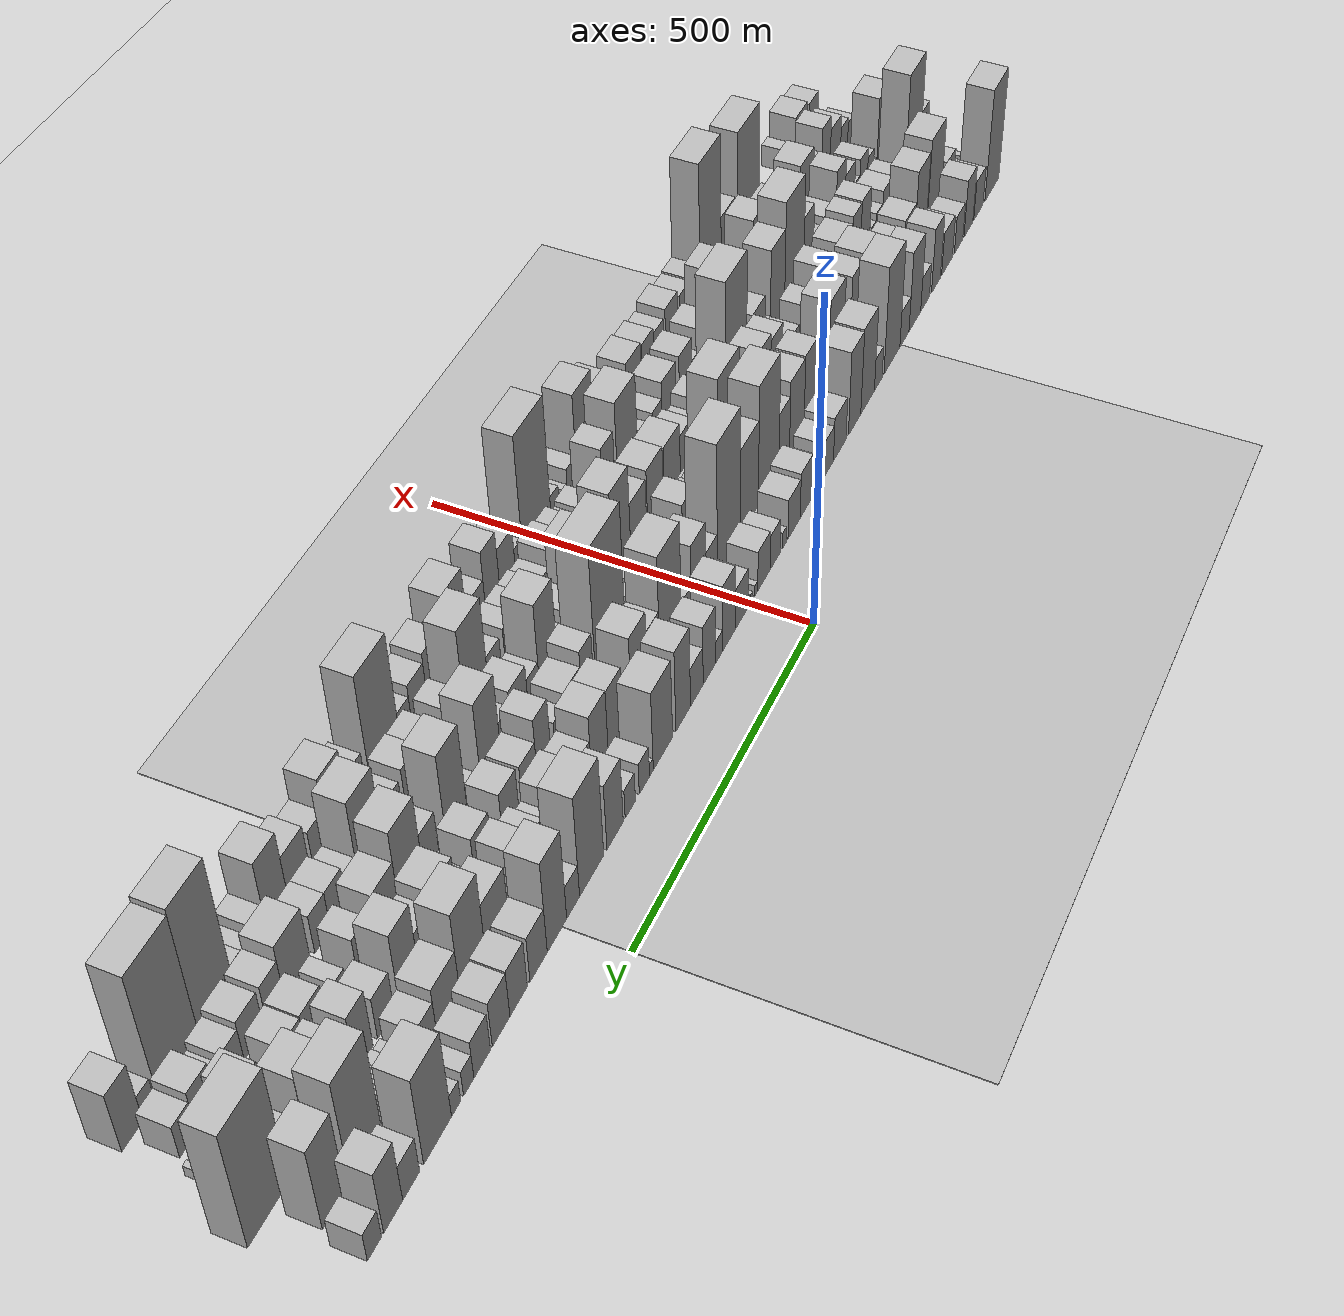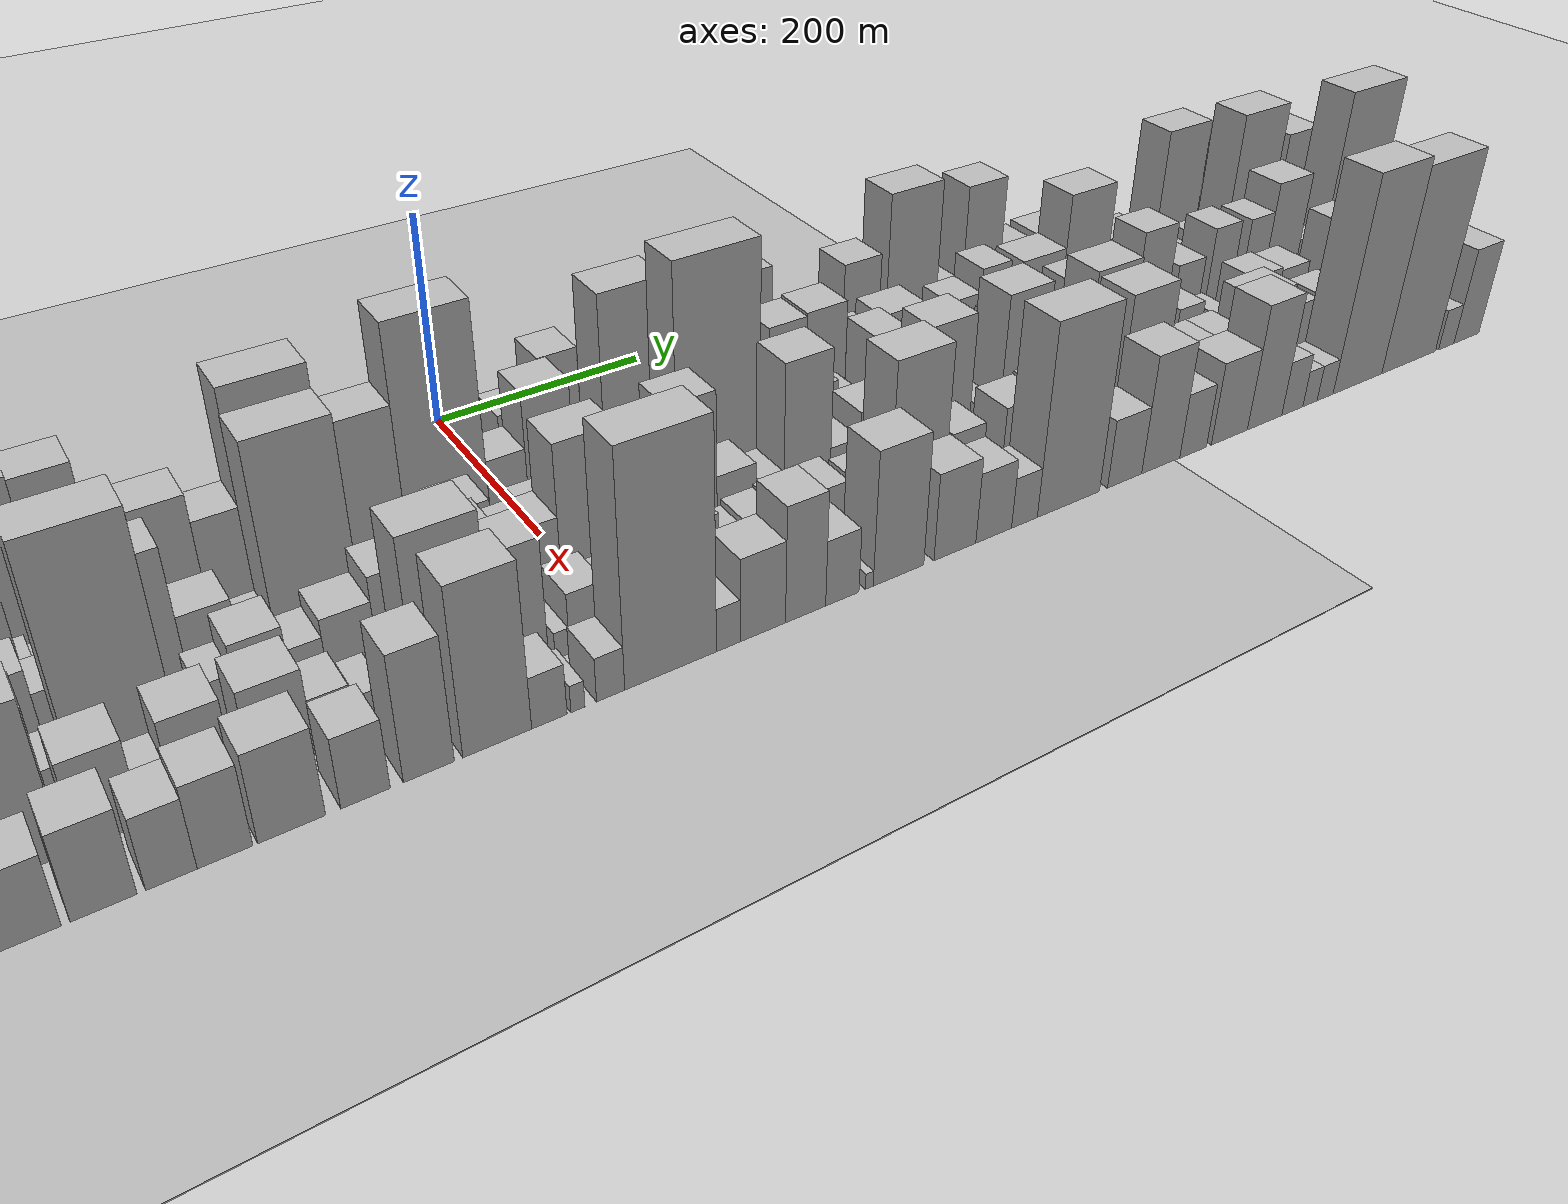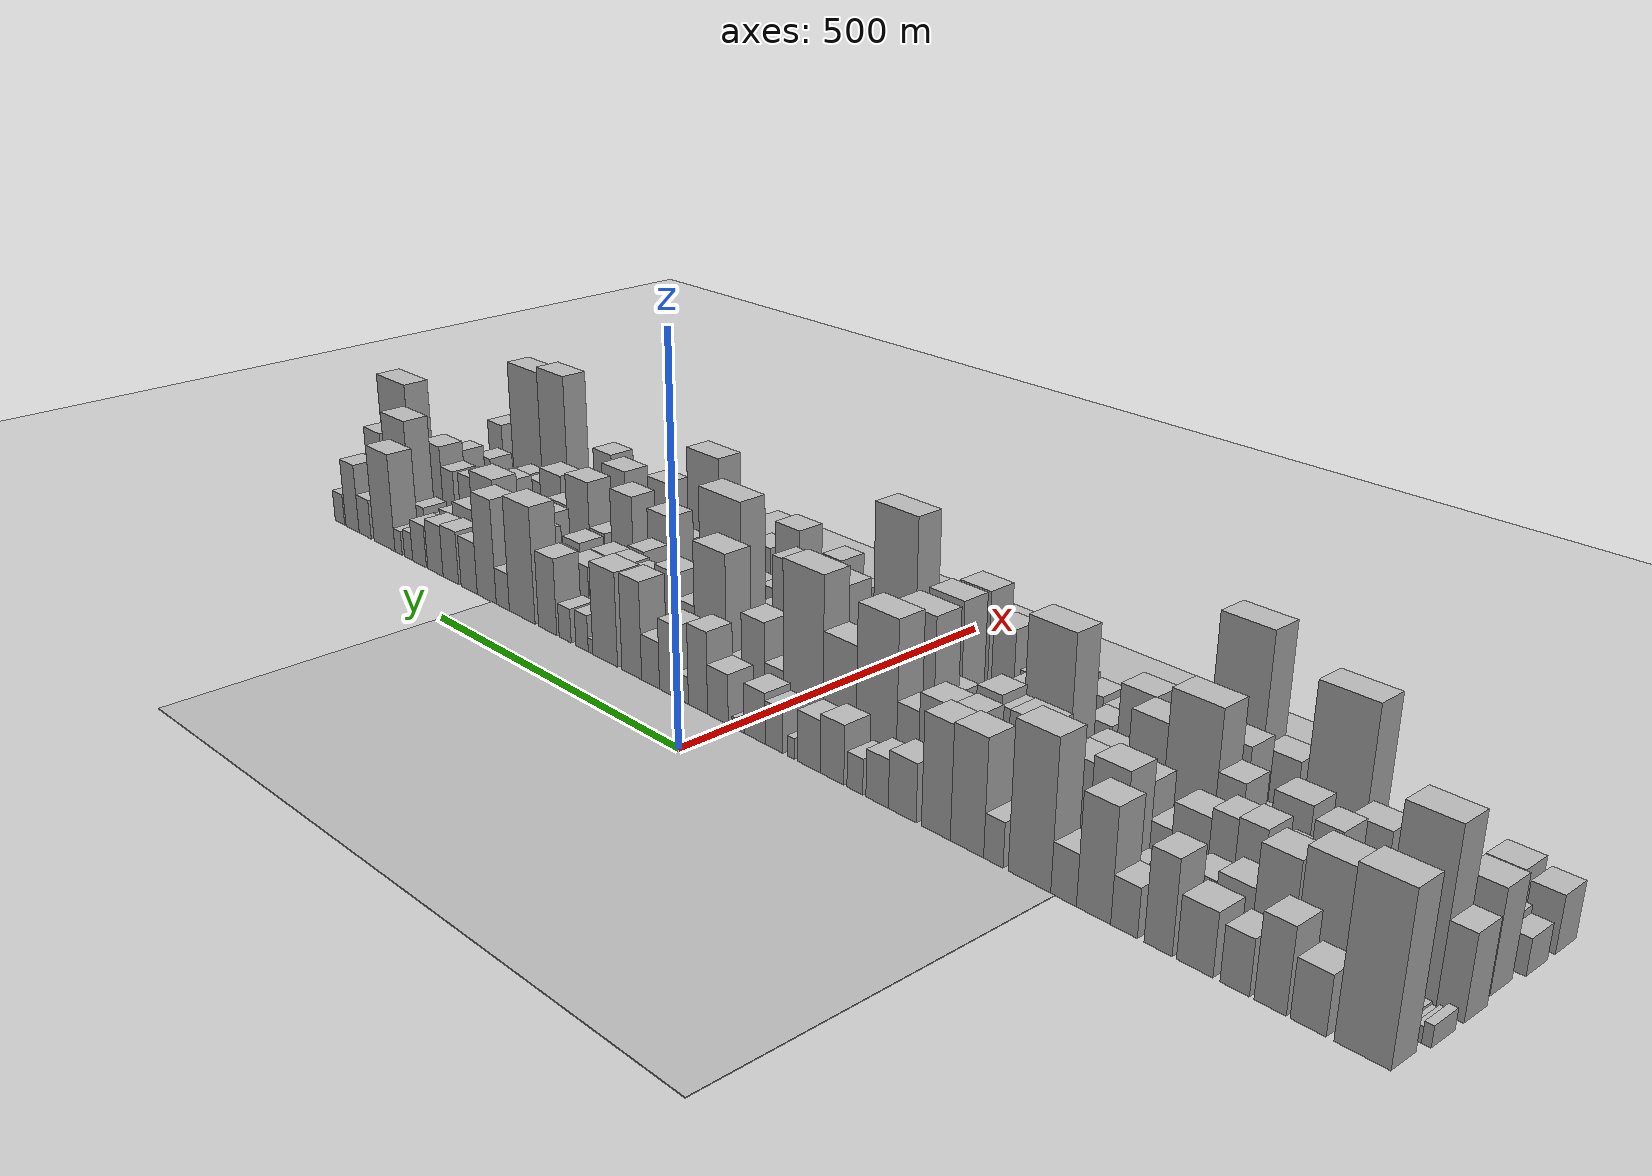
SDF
<?xml version="1.0" encoding="utf-8"?>

<sdf version="1.6">

   <world name="default">

      <gui fullscreen="0">

         <camera name="user_camera">

            <pose>-15 0 4.57585 0 0 0</pose>

            <view_controller>orbit</view_controller>

         </camera>

      </gui>

      <scene>

         <sky>

           <clouds>

             <speed>12</speed>

           </clouds>

         </sky>

         <ambient>0.4 0.4 0.4 1</ambient>

         <background>0.7 0.7 0.7 1</background>

         <shadows>1</shadows>

      </scene>

      <gravity>0 0 -9.8066</gravity>

      <magnetic_field>6e-06 2.3e-05 -4.2e-05</magnetic_field>

      <physics default="0" name="default_physics" type="ode">

         <ode>

            <solver>

               <type>quick</type>

               <iters>10</iters>

               <sor>1.0</sor>

               <use_dynamic_moi_rescaling>0</use_dynamic_moi_rescaling>

            </solver>

            <constraints>

               <cfm>0</cfm>

               <erp>0.2</erp>

               <contact_max_correcting_vel>100</contact_max_correcting_vel>

               <contact_surface_layer>0.001</contact_surface_layer>

            </constraints>

         </ode>

         <max_step_size>0.004</max_step_size>

         <real_time_factor>1</real_time_factor>

         <real_time_update_rate>250</real_time_update_rate>

      </physics>

      <light name="sun" type="directional">

         <cast_shadows>1</cast_shadows>

         <pose>0 0 10 0 0 0</pose>

         <diffuse>0.8 0.8 0.8 1</diffuse>

         <specular>0.2 0.2 0.2 1</specular>

         <attenuation>

            <range>1000</range>

            <constant>0.9</constant>

            <linear>0.01</linear>

            <quadratic>0.001</quadratic>

         </attenuation>

         <direction>-0.5 0.1 -0.9</direction>

      </light>

      <include>

         <name>ground_plane_1</name>

         <uri>model://HANNAS_ground_plane</uri>

         <pose>0 0 0  0 0 0</pose>

      </include>

      <include>

         <name>ground_plane_2</name>

         <uri>model://HANNAS_ground_plane</uri>

         <pose>100 0 0  0 0 0</pose>

      </include>

      <model name="building_1">

         <static>1</static>

         <pose frame="">100.0000 -855.0079 0 0.000000 0.000000 0.000000</pose>

         <link name="link">

            <pose frame="">0 0 93.00 0 0 0</pose>

            <collision name="collision">

               <geometry>

                  <box>

                     <size>40.0000 57.9842 186.0000</size>

                  </box>

               </geometry>

               <max_contacts>10</max_contacts>

               <surface>

                  <contact>

                     <ode/>

                  </contact>

                  <bounce/>

                  <friction>

                     <torsional>

                        <ode/>

                     </torsional>

                     <ode/>

                  </friction>

               </surface>

            </collision>

            <visual name="visual">

               <cast_shadows>0</cast_shadows>

               <geometry>

                  <box>

                     <size>40.0000 57.9842 186.0000</size>

                  </box>

               </geometry>

               <material>

                  <script>

                     <uri>model://HANNAS_wall/materials/scripts</uri>

                     <uri>model://HANNAS_wall/materials/textures</uri>

                     <name>vrc/HANNAS_wall</name>

                  </script>

               </material>

            </visual>

            <self_collide>0</self_collide>

            <enable_wind>0</enable_wind>

            <kinematic>0</kinematic>

         </link>

      </model>

      <model name="building_2">

         <static>1</static>

         <pose frame="">100.0000 -798.8635 0 0.000000 0.000000 0.000000</pose>

         <link name="link">

            <pose frame="">0 0 33.00 0 0 0</pose>

            <collision name="collision">

               <geometry>

                  <box>

                     <size>40.0000 38.3047 66.0000</size>

                  </box>

               </geometry>

               <max_contacts>10</max_contacts>

               <surface>

                  <contact>

                     <ode/>

                  </contact>

                  <bounce/>

                  <friction>

                     <torsional>

                        <ode/>

                     </torsional>

                     <ode/>

                  </friction>

               </surface>

            </collision>

            <visual name="visual">

               <cast_shadows>0</cast_shadows>

               <geometry>

                  <box>

                     <size>40.0000 38.3047 66.0000</size>

                  </box>

               </geometry>

               <material>

                  <script>

                     <uri>model://HANNAS_wall/materials/scripts</uri>

                     <uri>model://HANNAS_wall/materials/textures</uri>

                     <name>vrc/HANNAS_wall</name>

                  </script>

               </material>

            </visual>

            <self_collide>0</self_collide>

            <enable_wind>0</enable_wind>

            <kinematic>0</kinematic>

         </link>

      </model>

      <model name="building_3">

         <static>1</static>

         <pose frame="">100.0000 -757.9842 0 0.000000 0.000000 0.000000</pose>

         <link name="link">

            <pose frame="">0 0 48.00 0 0 0</pose>

            <collision name="collision">

               <geometry>

                  <box>

                     <size>40.0000 35.4537 96.0000</size>

                  </box>

               </geometry>

               <max_contacts>10</max_contacts>

               <surface>

                  <contact>

                     <ode/>

                  </contact>

                  <bounce/>

                  <friction>

                     <torsional>

                        <ode/>

                     </torsional>

                     <ode/>

                  </friction>

               </surface>

            </collision>

            <visual name="visual">

               <cast_shadows>0</cast_shadows>

               <geometry>

                  <box>

                     <size>40.0000 35.4537 96.0000</size>

                  </box>

               </geometry>

               <material>

                  <script>

                     <uri>model://HANNAS_wall/materials/scripts</uri>

                     <uri>model://HANNAS_wall/materials/textures</uri>

                     <name>vrc/HANNAS_wall</name>

                  </script>

               </material>

            </visual>

            <self_collide>0</self_collide>

            <enable_wind>0</enable_wind>

            <kinematic>0</kinematic>

         </link>

      </model>

      <model name="building_4">

         <static>1</static>

         <pose frame="">100.0000 -718.6537 0 0.000000 0.000000 0.000000</pose>

         <link name="link">

            <pose frame="">0 0 31.50 0 0 0</pose>

            <collision name="collision">

               <geometry>

                  <box>

                     <size>40.0000 33.2072 63.0000</size>

                  </box>

               </geometry>

               <max_contacts>10</max_contacts>

               <surface>

                  <contact>

                     <ode/>

                  </contact>

                  <bounce/>

                  <friction>

                     <torsional>

                        <ode/>

                     </torsional>

                     <ode/>

                  </friction>

               </surface>

            </collision>

            <visual name="visual">

               <cast_shadows>0</cast_shadows>

               <geometry>

                  <box>

                     <size>40.0000 33.2072 63.0000</size>

                  </box>

               </geometry>

               <material>

                  <script>

                     <uri>model://HANNAS_wall/materials/scripts</uri>

                     <uri>model://HANNAS_wall/materials/textures</uri>

                     <name>vrc/HANNAS_wall</name>

                  </script>

               </material>

            </visual>

            <self_collide>0</self_collide>

            <enable_wind>0</enable_wind>

            <kinematic>0</kinematic>

         </link>

      </model>

      <model name="building_5">

         <static>1</static>

         <pose frame="">100.0000 -672.7958 0 0.000000 0.000000 0.000000</pose>

         <link name="link">

            <pose frame="">0 0 36.00 0 0 0</pose>

            <collision name="collision">

               <geometry>

                  <box>

                     <size>40.0000 42.5087 72.0000</size>

                  </box>

               </geometry>

               <max_contacts>10</max_contacts>

               <surface>

                  <contact>

                     <ode/>

                  </contact>

                  <bounce/>

                  <friction>

                     <torsional>

                        <ode/>

                     </torsional>

                     <ode/>

                  </friction>

               </surface>

            </collision>

            <visual name="visual">

               <cast_shadows>0</cast_shadows>

               <geometry>

                  <box>

                     <size>40.0000 42.5087 72.0000</size>

                  </box>

               </geometry>

               <material>

                  <script>

                     <uri>model://HANNAS_wall/materials/scripts</uri>

                     <uri>model://HANNAS_wall/materials/textures</uri>

                     <name>vrc/HANNAS_wall</name>

                  </script>

               </material>

            </visual>

            <self_collide>0</self_collide>

            <enable_wind>0</enable_wind>

            <kinematic>0</kinematic>

         </link>

      </model>

      <model name="building_6">

         <static>1</static>

         <pose frame="">100.0000 -629.5674 0 0.000000 0.000000 0.000000</pose>

         <link name="link">

            <pose frame="">0 0 54.00 0 0 0</pose>

            <collision name="collision">

               <geometry>

                  <box>

                     <size>40.0000 33.9480 108.0000</size>

                  </box>

               </geometry>

               <max_contacts>10</max_contacts>

               <surface>

                  <contact>

                     <ode/>

                  </contact>

                  <bounce/>

                  <friction>

                     <torsional>

                        <ode/>

                     </torsional>

                     <ode/>

                  </friction>

               </surface>

            </collision>

            <visual name="visual">

               <cast_shadows>0</cast_shadows>

               <geometry>

                  <box>

                     <size>40.0000 33.9480 108.0000</size>

                  </box>

               </geometry>

               <material>

                  <script>

                     <uri>model://HANNAS_wall/materials/scripts</uri>

                     <uri>model://HANNAS_wall/materials/textures</uri>

                     <name>vrc/HANNAS_wall</name>

                  </script>

               </material>

            </visual>

            <self_collide>0</self_collide>

            <enable_wind>0</enable_wind>

            <kinematic>0</kinematic>

         </link>

      </model>

      <model name="building_7">

         <static>1</static>

         <pose frame="">100.0000 -588.0046 0 0.000000 0.000000 0.000000</pose>

         <link name="link">

            <pose frame="">0 0 28.50 0 0 0</pose>

            <collision name="collision">

               <geometry>

                  <box>

                     <size>40.0000 33.1776 57.0000</size>

                  </box>

               </geometry>

               <max_contacts>10</max_contacts>

               <surface>

                  <contact>

                     <ode/>

                  </contact>

                  <bounce/>

                  <friction>

                     <torsional>

                        <ode/>

                     </torsional>

                     <ode/>

                  </friction>

               </surface>

            </collision>

            <visual name="visual">

               <cast_shadows>0</cast_shadows>

               <geometry>

                  <box>

                     <size>40.0000 33.1776 57.0000</size>

                  </box>

               </geometry>

               <material>

                  <script>

                     <uri>model://HANNAS_wall/materials/scripts</uri>

                     <uri>model://HANNAS_wall/materials/textures</uri>

                     <name>vrc/HANNAS_wall</name>

                  </script>

               </material>

            </visual>

            <self_collide>0</self_collide>

            <enable_wind>0</enable_wind>

            <kinematic>0</kinematic>

         </link>

      </model>

      <model name="building_8">

         <static>1</static>

         <pose frame="">100.0000 -549.5656 0 0.000000 0.000000 0.000000</pose>

         <link name="link">

            <pose frame="">0 0 66.00 0 0 0</pose>

            <collision name="collision">

               <geometry>

                  <box>

                     <size>40.0000 43.7004 132.0000</size>

                  </box>

               </geometry>

               <max_contacts>10</max_contacts>

               <surface>

                  <contact>

                     <ode/>

                  </contact>

                  <bounce/>

                  <friction>

                     <torsional>

                        <ode/>

                     </torsional>

                     <ode/>

                  </friction>

               </surface>

            </collision>

            <visual name="visual">

               <cast_shadows>0</cast_shadows>

               <geometry>

                  <box>

                     <size>40.0000 43.7004 132.0000</size>

                  </box>

               </geometry>

               <material>

                  <script>

                     <uri>model://HANNAS_wall/materials/scripts</uri>

                     <uri>model://HANNAS_wall/materials/textures</uri>

                     <name>vrc/HANNAS_wall</name>

                  </script>

               </material>

            </visual>

            <self_collide>0</self_collide>

            <enable_wind>0</enable_wind>

            <kinematic>0</kinematic>

         </link>

      </model>

      <model name="building_9">

         <static>1</static>

         <pose frame="">100.0000 -510.9255 0 0.000000 0.000000 0.000000</pose>

         <link name="link">

            <pose frame="">0 0 30.00 0 0 0</pose>

            <collision name="collision">

               <geometry>

                  <box>

                     <size>40.0000 33.5798 60.0000</size>

                  </box>

               </geometry>

               <max_contacts>10</max_contacts>

               <surface>

                  <contact>

                     <ode/>

                  </contact>

                  <bounce/>

                  <friction>

                     <torsional>

                        <ode/>

                     </torsional>

                     <ode/>

                  </friction>

               </surface>

            </collision>

            <visual name="visual">

               <cast_shadows>0</cast_shadows>

               <geometry>

                  <box>

                     <size>40.0000 33.5798 60.0000</size>

                  </box>

               </geometry>

               <material>

                  <script>

                     <uri>model://HANNAS_wall/materials/scripts</uri>

                     <uri>model://HANNAS_wall/materials/textures</uri>

                     <name>vrc/HANNAS_wall</name>

                  </script>

               </material>

            </visual>

            <self_collide>0</self_collide>

            <enable_wind>0</enable_wind>

            <kinematic>0</kinematic>

         </link>

      </model>

      <model name="building_10">

         <static>1</static>

         <pose frame="">100.0000 -465.3672 0 0.000000 0.000000 0.000000</pose>

         <link name="link">

            <pose frame="">0 0 88.50 0 0 0</pose>

            <collision name="collision">

               <geometry>

                  <box>

                     <size>40.0000 57.5368 177.0000</size>

                  </box>

               </geometry>

               <max_contacts>10</max_contacts>

               <surface>

                  <contact>

                     <ode/>

                  </contact>

                  <bounce/>

                  <friction>

                     <torsional>

                        <ode/>

                     </torsional>

                     <ode/>

                  </friction>

               </surface>

            </collision>

            <visual name="visual">

               <cast_shadows>0</cast_shadows>

               <geometry>

                  <box>

                     <size>40.0000 57.5368 177.0000</size>

                  </box>

               </geometry>

               <material>

                  <script>

                     <uri>model://HANNAS_wall/materials/scripts</uri>

                     <uri>model://HANNAS_wall/materials/textures</uri>

                     <name>vrc/HANNAS_wall</name>

                  </script>

               </material>

            </visual>

            <self_collide>0</self_collide>

            <enable_wind>0</enable_wind>

            <kinematic>0</kinematic>

         </link>

      </model>

      <model name="building_11">

         <static>1</static>

         <pose frame="">100.0000 -416.0420 0 0.000000 0.000000 0.000000</pose>

         <link name="link">

            <pose frame="">0 0 27.00 0 0 0</pose>

            <collision name="collision">

               <geometry>

                  <box>

                     <size>40.0000 27.1138 54.0000</size>

                  </box>

               </geometry>

               <max_contacts>10</max_contacts>

               <surface>

                  <contact>

                     <ode/>

                  </contact>

                  <bounce/>

                  <friction>

                     <torsional>

                        <ode/>

                     </torsional>

                     <ode/>

                  </friction>

               </surface>

            </collision>

            <visual name="visual">

               <cast_shadows>0</cast_shadows>

               <geometry>

                  <box>

                     <size>40.0000 27.1138 54.0000</size>

                  </box>

               </geometry>

               <material>

                  <script>

                     <uri>model://HANNAS_wall/materials/scripts</uri>

                     <uri>model://HANNAS_wall/materials/textures</uri>

                     <name>vrc/HANNAS_wall</name>

                  </script>

               </material>

            </visual>

            <self_collide>0</self_collide>

            <enable_wind>0</enable_wind>

            <kinematic>0</kinematic>

         </link>

      </model>

      <model name="building_12">

         <static>1</static>

         <pose frame="">100.0000 -378.6074 0 0.000000 0.000000 0.000000</pose>

         <link name="link">

            <pose frame="">0 0 70.50 0 0 0</pose>

            <collision name="collision">

               <geometry>

                  <box>

                     <size>40.0000 47.7554 141.0000</size>

                  </box>

               </geometry>

               <max_contacts>10</max_contacts>

               <surface>

                  <contact>

                     <ode/>

                  </contact>

                  <bounce/>

                  <friction>

                     <torsional>

                        <ode/>

                     </torsional>

                     <ode/>

                  </friction>

               </surface>

            </collision>

            <visual name="visual">

               <cast_shadows>0</cast_shadows>

               <geometry>

                  <box>

                     <size>40.0000 47.7554 141.0000</size>

                  </box>

               </geometry>

               <material>

                  <script>

                     <uri>model://HANNAS_wall/materials/scripts</uri>

                     <uri>model://HANNAS_wall/materials/textures</uri>

                     <name>vrc/HANNAS_wall</name>

                  </script>

               </material>

            </visual>

            <self_collide>0</self_collide>

            <enable_wind>0</enable_wind>

            <kinematic>0</kinematic>

         </link>

      </model>

      <model name="building_13">

         <static>1</static>

         <pose frame="">100.0000 -333.4832 0 0.000000 0.000000 0.000000</pose>

         <link name="link">

            <pose frame="">0 0 69.00 0 0 0</pose>

            <collision name="collision">

               <geometry>

                  <box>

                     <size>40.0000 42.4929 138.0000</size>

                  </box>

               </geometry>

               <max_contacts>10</max_contacts>

               <surface>

                  <contact>

                     <ode/>

                  </contact>

                  <bounce/>

                  <friction>

                     <torsional>

                        <ode/>

                     </torsional>

                     <ode/>

                  </friction>

               </surface>

            </collision>

            <visual name="visual">

               <cast_shadows>0</cast_shadows>

               <geometry>

                  <box>

                     <size>40.0000 42.4929 138.0000</size>

                  </box>

               </geometry>

               <material>

                  <script>

                     <uri>model://HANNAS_wall/materials/scripts</uri>

                     <uri>model://HANNAS_wall/materials/textures</uri>

                     <name>vrc/HANNAS_wall</name>

                  </script>

               </material>

            </visual>

            <self_collide>0</self_collide>

            <enable_wind>0</enable_wind>

            <kinematic>0</kinematic>

         </link>

      </model>

      <model name="building_14">

         <static>1</static>

         <pose frame="">100.0000 -283.0723 0 0.000000 0.000000 0.000000</pose>

         <link name="link">

            <pose frame="">0 0 36.00 0 0 0</pose>

            <collision name="collision">

               <geometry>

                  <box>

                     <size>40.0000 42.3288 72.0000</size>

                  </box>

               </geometry>

               <max_contacts>10</max_contacts>

               <surface>

                  <contact>

                     <ode/>

                  </contact>

                  <bounce/>

                  <friction>

                     <torsional>

                        <ode/>

                     </torsional>

                     <ode/>

                  </friction>

               </surface>

            </collision>

            <visual name="visual">

               <cast_shadows>0</cast_shadows>

               <geometry>

                  <box>

                     <size>40.0000 42.3288 72.0000</size>

                  </box>

               </geometry>

               <material>

                  <script>

                     <uri>model://HANNAS_wall/materials/scripts</uri>

                     <uri>model://HANNAS_wall/materials/textures</uri>

                     <name>vrc/HANNAS_wall</name>

                  </script>

               </material>

            </visual>

            <self_collide>0</self_collide>

            <enable_wind>0</enable_wind>

            <kinematic>0</kinematic>

         </link>

      </model>

      <model name="building_15">

         <static>1</static>

         <pose frame="">100.0000 -244.4086 0 0.000000 0.000000 0.000000</pose>

         <link name="link">

            <pose frame="">0 0 30.00 0 0 0</pose>

            <collision name="collision">

               <geometry>

                  <box>

                     <size>40.0000 34.9986 60.0000</size>

                  </box>

               </geometry>

               <max_contacts>10</max_contacts>

               <surface>

                  <contact>

                     <ode/>

                  </contact>

                  <bounce/>

                  <friction>

                     <torsional>

                        <ode/>

                     </torsional>

                     <ode/>

                  </friction>

               </surface>

            </collision>

            <visual name="visual">

               <cast_shadows>0</cast_shadows>

               <geometry>

                  <box>

                     <size>40.0000 34.9986 60.0000</size>

                  </box>

               </geometry>

               <material>

                  <script>

                     <uri>model://HANNAS_wall/materials/scripts</uri>

                     <uri>model://HANNAS_wall/materials/textures</uri>

                     <name>vrc/HANNAS_wall</name>

                  </script>

               </material>

            </visual>

            <self_collide>0</self_collide>

            <enable_wind>0</enable_wind>

            <kinematic>0</kinematic>

         </link>

      </model>

      <model name="building_16">

         <static>1</static>

         <pose frame="">100.0000 -209.2729 0 0.000000 0.000000 0.000000</pose>

         <link name="link">

            <pose frame="">0 0 22.50 0 0 0</pose>

            <collision name="collision">

               <geometry>

                  <box>

                     <size>40.0000 25.2728 45.0000</size>

                  </box>

               </geometry>

               <max_contacts>10</max_contacts>

               <surface>

                  <contact>

                     <ode/>

                  </contact>

                  <bounce/>

                  <friction>

                     <torsional>

                        <ode/>

                     </torsional>

                     <ode/>

                  </friction>

               </surface>

            </collision>

            <visual name="visual">

               <cast_shadows>0</cast_shadows>

               <geometry>

                  <box>

                     <size>40.0000 25.2728 45.0000</size>

                  </box>

               </geometry>

               <material>

                  <script>

                     <uri>model://HANNAS_wall/materials/scripts</uri>

                     <uri>model://HANNAS_wall/materials/textures</uri>

                     <name>vrc/HANNAS_wall</name>

                  </script>

               </material>

            </visual>

            <self_collide>0</self_collide>

            <enable_wind>0</enable_wind>

            <kinematic>0</kinematic>

         </link>

      </model>

      <model name="building_17">

         <static>1</static>

         <pose frame="">100.0000 -172.5499 0 0.000000 0.000000 0.000000</pose>

         <link name="link">

            <pose frame="">0 0 37.50 0 0 0</pose>

            <collision name="collision">

               <geometry>

                  <box>

                     <size>40.0000 38.1732 75.0000</size>

                  </box>

               </geometry>

               <max_contacts>10</max_contacts>

               <surface>

                  <contact>

                     <ode/>

                  </contact>

                  <bounce/>

                  <friction>

                     <torsional>

                        <ode/>

                     </torsional>

                     <ode/>

                  </friction>

               </surface>

            </collision>

            <visual name="visual">

               <cast_shadows>0</cast_shadows>

               <geometry>

                  <box>

                     <size>40.0000 38.1732 75.0000</size>

                  </box>

               </geometry>

               <material>

                  <script>

                     <uri>model://HANNAS_wall/materials/scripts</uri>

                     <uri>model://HANNAS_wall/materials/textures</uri>

                     <name>vrc/HANNAS_wall</name>

                  </script>

               </material>

            </visual>

            <self_collide>0</self_collide>

            <enable_wind>0</enable_wind>

            <kinematic>0</kinematic>

         </link>

      </model>

      <model name="building_18">

         <static>1</static>

         <pose frame="">100.0000 -134.1330 0 0.000000 0.000000 0.000000</pose>

         <link name="link">

            <pose frame="">0 0 33.00 0 0 0</pose>

            <collision name="collision">

               <geometry>

                  <box>

                     <size>40.0000 38.6607 66.0000</size>

                  </box>

               </geometry>

               <max_contacts>10</max_contacts>

               <surface>

                  <contact>

                     <ode/>

                  </contact>

                  <bounce/>

                  <friction>

                     <torsional>

                        <ode/>

                     </torsional>

                     <ode/>

                  </friction>

               </surface>

            </collision>

            <visual name="visual">

               <cast_shadows>0</cast_shadows>

               <geometry>

                  <box>

                     <size>40.0000 38.6607 66.0000</size>

                  </box>

               </geometry>

               <material>

                  <script>

                     <uri>model://HANNAS_wall/materials/scripts</uri>

                     <uri>model://HANNAS_wall/materials/textures</uri>

                     <name>vrc/HANNAS_wall</name>

                  </script>

               </material>

            </visual>

            <self_collide>0</self_collide>

            <enable_wind>0</enable_wind>

            <kinematic>0</kinematic>

         </link>

      </model>

      <model name="building_19">

         <static>1</static>

         <pose frame="">100.0000 -103.9196 0 0.000000 0.000000 0.000000</pose>

         <link name="link">

            <pose frame="">0 0 13.50 0 0 0</pose>

            <collision name="collision">

               <geometry>

                  <box>

                     <size>40.0000 11.7662 27.0000</size>

                  </box>

               </geometry>

               <max_contacts>10</max_contacts>

               <surface>

                  <contact>

                     <ode/>

                  </contact>

                  <bounce/>

                  <friction>

                     <torsional>

                        <ode/>

                     </torsional>

                     <ode/>

                  </friction>

               </surface>

            </collision>

            <visual name="visual">

               <cast_shadows>0</cast_shadows>

               <geometry>

                  <box>

                     <size>40.0000 11.7662 27.0000</size>

                  </box>

               </geometry>

               <material>

                  <script>

                     <uri>model://HANNAS_wall/materials/scripts</uri>

                     <uri>model://HANNAS_wall/materials/textures</uri>

                     <name>vrc/HANNAS_wall</name>

                  </script>

               </material>

            </visual>

            <self_collide>0</self_collide>

            <enable_wind>0</enable_wind>

            <kinematic>0</kinematic>

         </link>

      </model>

      <model name="building_20">

         <static>1</static>

         <pose frame="">100.0000 -74.7390 0 0.000000 0.000000 0.000000</pose>

         <link name="link">

            <pose frame="">0 0 28.50 0 0 0</pose>

            <collision name="collision">

               <geometry>

                  <box>

                     <size>40.0000 30.5950 57.0000</size>

                  </box>

               </geometry>

               <max_contacts>10</max_contacts>

               <surface>

                  <contact>

                     <ode/>

                  </contact>

                  <bounce/>

                  <friction>

                     <torsional>

                        <ode/>

                     </torsional>

                     <ode/>

                  </friction>

               </surface>

            </collision>

            <visual name="visual">

               <cast_shadows>0</cast_shadows>

               <geometry>

                  <box>

                     <size>40.0000 30.5950 57.0000</size>

                  </box>

               </geometry>

               <material>

                  <script>

                     <uri>model://HANNAS_wall/materials/scripts</uri>

                     <uri>model://HANNAS_wall/materials/textures</uri>

                     <name>vrc/HANNAS_wall</name>

                  </script>

               </material>

            </visual>

            <self_collide>0</self_collide>

            <enable_wind>0</enable_wind>

            <kinematic>0</kinematic>

         </link>

      </model>

      <model name="building_21">

         <static>1</static>

         <pose frame="">100.0000 -40.7443 0 0.000000 0.000000 0.000000</pose>

         <link name="link">

            <pose frame="">0 0 33.00 0 0 0</pose>

            <collision name="collision">

               <geometry>

                  <box>

                     <size>40.0000 37.3942 66.0000</size>

                  </box>

               </geometry>

               <max_contacts>10</max_contacts>

               <surface>

                  <contact>

                     <ode/>

                  </contact>

                  <bounce/>

                  <friction>

                     <torsional>

                        <ode/>

                     </torsional>

                     <ode/>

                  </friction>

               </surface>

            </collision>

            <visual name="visual">

               <cast_shadows>0</cast_shadows>

               <geometry>

                  <box>

                     <size>40.0000 37.3942 66.0000</size>

                  </box>

               </geometry>

               <material>

                  <script>

                     <uri>model://HANNAS_wall/materials/scripts</uri>

                     <uri>model://HANNAS_wall/materials/textures</uri>

                     <name>vrc/HANNAS_wall</name>

                  </script>

               </material>

            </visual>

            <self_collide>0</self_collide>

            <enable_wind>0</enable_wind>

            <kinematic>0</kinematic>

         </link>

      </model>

      <model name="building_22">

         <static>1</static>

         <pose frame="">100.0000 -17.7094 0 0.000000 0.000000 0.000000</pose>

         <link name="link">

            <pose frame="">0 0 9.00 0 0 0</pose>

            <collision name="collision">

               <geometry>

                  <box>

                     <size>40.0000 8.6757 18.0000</size>

                  </box>

               </geometry>

               <max_contacts>10</max_contacts>

               <surface>

                  <contact>

                     <ode/>

                  </contact>

                  <bounce/>

                  <friction>

                     <torsional>

                        <ode/>

                     </torsional>

                     <ode/>

                  </friction>

               </surface>

            </collision>

            <visual name="visual">

               <cast_shadows>0</cast_shadows>

               <geometry>

                  <box>

                     <size>40.0000 8.6757 18.0000</size>

                  </box>

               </geometry>

               <material>

                  <script>

                     <uri>model://HANNAS_wall/materials/scripts</uri>

                     <uri>model://HANNAS_wall/materials/textures</uri>

                     <name>vrc/HANNAS_wall</name>

                  </script>

               </material>

            </visual>

            <self_collide>0</self_collide>

            <enable_wind>0</enable_wind>

            <kinematic>0</kinematic>

         </link>

      </model>

      <model name="building_23">

         <static>1</static>

         <pose frame="">100.0000 -3.8777 0 0.000000 0.000000 0.000000</pose>

         <link name="link">

            <pose frame="">0 0 7.50 0 0 0</pose>

            <collision name="collision">

               <geometry>

                  <box>

                     <size>40.0000 6.9877 15.0000</size>

                  </box>

               </geometry>

               <max_contacts>10</max_contacts>

               <surface>

                  <contact>

                     <ode/>

                  </contact>

                  <bounce/>

                  <friction>

                     <torsional>

                        <ode/>

                     </torsional>

                     <ode/>

                  </friction>

               </surface>

            </collision>

            <visual name="visual">

               <cast_shadows>0</cast_shadows>

               <geometry>

                  <box>

                     <size>40.0000 6.9877 15.0000</size>

                  </box>

               </geometry>

               <material>

                  <script>

                     <uri>model://HANNAS_wall/materials/scripts</uri>

                     <uri>model://HANNAS_wall/materials/textures</uri>

                     <name>vrc/HANNAS_wall</name>

                  </script>

               </material>

            </visual>

            <self_collide>0</self_collide>

            <enable_wind>0</enable_wind>

            <kinematic>0</kinematic>

         </link>

      </model>

      <model name="building_24">

         <static>1</static>

         <pose frame="">100.0000 25.6848 0 0.000000 0.000000 0.000000</pose>

         <link name="link">

            <pose frame="">0 0 33.00 0 0 0</pose>

            <collision name="collision">

               <geometry>

                  <box>

                     <size>40.0000 38.1373 66.0000</size>

                  </box>

               </geometry>

               <max_contacts>10</max_contacts>

               <surface>

                  <contact>

                     <ode/>

                  </contact>

                  <bounce/>

                  <friction>

                     <torsional>

                        <ode/>

                     </torsional>

                     <ode/>

                  </friction>

               </surface>

            </collision>

            <visual name="visual">

               <cast_shadows>0</cast_shadows>

               <geometry>

                  <box>

                     <size>40.0000 38.1373 66.0000</size>

                  </box>

               </geometry>

               <material>

                  <script>

                     <uri>model://HANNAS_wall/materials/scripts</uri>

                     <uri>model://HANNAS_wall/materials/textures</uri>

                     <name>vrc/HANNAS_wall</name>

                  </script>

               </material>

            </visual>

            <self_collide>0</self_collide>

            <enable_wind>0</enable_wind>

            <kinematic>0</kinematic>

         </link>

      </model>

      <model name="building_25">

         <static>1</static>

         <pose frame="">100.0000 62.7408 0 0.000000 0.000000 0.000000</pose>

         <link name="link">

            <pose frame="">0 0 54.00 0 0 0</pose>

            <collision name="collision">

               <geometry>

                  <box>

                     <size>40.0000 35.9746 108.0000</size>

                  </box>

               </geometry>

               <max_contacts>10</max_contacts>

               <surface>

                  <contact>

                     <ode/>

                  </contact>

                  <bounce/>

                  <friction>

                     <torsional>

                        <ode/>

                     </torsional>

                     <ode/>

                  </friction>

               </surface>

            </collision>

            <visual name="visual">

               <cast_shadows>0</cast_shadows>

               <geometry>

                  <box>

                     <size>40.0000 35.9746 108.0000</size>

                  </box>

               </geometry>

               <material>

                  <script>

                     <uri>model://HANNAS_wall/materials/scripts</uri>

                     <uri>model://HANNAS_wall/materials/textures</uri>

                     <name>vrc/HANNAS_wall</name>

                  </script>

               </material>

            </visual>

            <self_collide>0</self_collide>

            <enable_wind>0</enable_wind>

            <kinematic>0</kinematic>

         </link>

      </model>

      <model name="building_26">

         <static>1</static>

         <pose frame="">100.0000 91.1006 0 0.000000 0.000000 0.000000</pose>

         <link name="link">

            <pose frame="">0 0 18.00 0 0 0</pose>

            <collision name="collision">

               <geometry>

                  <box>

                     <size>40.0000 20.7449 36.0000</size>

                  </box>

               </geometry>

               <max_contacts>10</max_contacts>

               <surface>

                  <contact>

                     <ode/>

                  </contact>

                  <bounce/>

                  <friction>

                     <torsional>

                        <ode/>

                     </torsional>

                     <ode/>

                  </friction>

               </surface>

            </collision>

            <visual name="visual">

               <cast_shadows>0</cast_shadows>

               <geometry>

                  <box>

                     <size>40.0000 20.7449 36.0000</size>

                  </box>

               </geometry>

               <material>

                  <script>

                     <uri>model://HANNAS_wall/materials/scripts</uri>

                     <uri>model://HANNAS_wall/materials/textures</uri>

                     <name>vrc/HANNAS_wall</name>

                  </script>

               </material>

            </visual>

            <self_collide>0</self_collide>

            <enable_wind>0</enable_wind>

            <kinematic>0</kinematic>

         </link>

      </model>

      <model name="building_27">

         <static>1</static>

         <pose frame="">100.0000 119.0451 0 0.000000 0.000000 0.000000</pose>

         <link name="link">

            <pose frame="">0 0 48.00 0 0 0</pose>

            <collision name="collision">

               <geometry>

                  <box>

                     <size>40.0000 35.1443 96.0000</size>

                  </box>

               </geometry>

               <max_contacts>10</max_contacts>

               <surface>

                  <contact>

                     <ode/>

                  </contact>

                  <bounce/>

                  <friction>

                     <torsional>

                        <ode/>

                     </torsional>

                     <ode/>

                  </friction>

               </surface>

            </collision>

            <visual name="visual">

               <cast_shadows>0</cast_shadows>

               <geometry>

                  <box>

                     <size>40.0000 35.1443 96.0000</size>

                  </box>

               </geometry>

               <material>

                  <script>

                     <uri>model://HANNAS_wall/materials/scripts</uri>

                     <uri>model://HANNAS_wall/materials/textures</uri>

                     <name>vrc/HANNAS_wall</name>

                  </script>

               </material>

            </visual>

            <self_collide>0</self_collide>

            <enable_wind>0</enable_wind>

            <kinematic>0</kinematic>

         </link>

      </model>

      <model name="building_28">

         <static>1</static>

         <pose frame="">100.0000 154.2895 0 0.000000 0.000000 0.000000</pose>

         <link name="link">

            <pose frame="">0 0 31.50 0 0 0</pose>

            <collision name="collision">

               <geometry>

                  <box>

                     <size>40.0000 35.3444 63.0000</size>

                  </box>

               </geometry>

               <max_contacts>10</max_contacts>

               <surface>

                  <contact>

                     <ode/>

                  </contact>

                  <bounce/>

                  <friction>

                     <torsional>

                        <ode/>

                     </torsional>

                     <ode/>

                  </friction>

               </surface>

            </collision>

            <visual name="visual">

               <cast_shadows>0</cast_shadows>

               <geometry>

                  <box>

                     <size>40.0000 35.3444 63.0000</size>

                  </box>

               </geometry>

               <material>

                  <script>

                     <uri>model://HANNAS_wall/materials/scripts</uri>

                     <uri>model://HANNAS_wall/materials/textures</uri>

                     <name>vrc/HANNAS_wall</name>

                  </script>

               </material>

            </visual>

            <self_collide>0</self_collide>

            <enable_wind>0</enable_wind>

            <kinematic>0</kinematic>

         </link>

      </model>

      <model name="building_29">

         <static>1</static>

         <pose frame="">100.0000 192.0008 0 0.000000 0.000000 0.000000</pose>

         <link name="link">

            <pose frame="">0 0 66.00 0 0 0</pose>

            <collision name="collision">

               <geometry>

                  <box>

                     <size>40.0000 40.0782 132.0000</size>

                  </box>

               </geometry>

               <max_contacts>10</max_contacts>

               <surface>

                  <contact>

                     <ode/>

                  </contact>

                  <bounce/>

                  <friction>

                     <torsional>

                        <ode/>

                     </torsional>

                     <ode/>

                  </friction>

               </surface>

            </collision>

            <visual name="visual">

               <cast_shadows>0</cast_shadows>

               <geometry>

                  <box>

                     <size>40.0000 40.0782 132.0000</size>

                  </box>

               </geometry>

               <material>

                  <script>

                     <uri>model://HANNAS_wall/materials/scripts</uri>

                     <uri>model://HANNAS_wall/materials/textures</uri>

                     <name>vrc/HANNAS_wall</name>

                  </script>

               </material>

            </visual>

            <self_collide>0</self_collide>

            <enable_wind>0</enable_wind>

            <kinematic>0</kinematic>

         </link>

      </model>

      <model name="building_30">

         <static>1</static>

         <pose frame="">100.0000 246.7922 0 0.000000 0.000000 0.000000</pose>

         <link name="link">

            <pose frame="">0 0 64.50 0 0 0</pose>

            <collision name="collision">

               <geometry>

                  <box>

                     <size>40.0000 51.5045 129.0000</size>

                  </box>

               </geometry>

               <max_contacts>10</max_contacts>

               <surface>

                  <contact>

                     <ode/>

                  </contact>

                  <bounce/>

                  <friction>

                     <torsional>

                        <ode/>

                     </torsional>

                     <ode/>

                  </friction>

               </surface>

            </collision>

            <visual name="visual">

               <cast_shadows>0</cast_shadows>

               <geometry>

                  <box>

                     <size>40.0000 51.5045 129.0000</size>

                  </box>

               </geometry>

               <material>

                  <script>

                     <uri>model://HANNAS_wall/materials/scripts</uri>

                     <uri>model://HANNAS_wall/materials/textures</uri>

                     <name>vrc/HANNAS_wall</name>

                  </script>

               </material>

            </visual>

            <self_collide>0</self_collide>

            <enable_wind>0</enable_wind>

            <kinematic>0</kinematic>

         </link>

      </model>

      <model name="building_31">

         <static>1</static>

         <pose frame="">100.0000 277.4822 0 0.000000 0.000000 0.000000</pose>

         <link name="link">

            <pose frame="">0 0 10.50 0 0 0</pose>

            <collision name="collision">

               <geometry>

                  <box>

                     <size>40.0000 9.8754 21.0000</size>

                  </box>

               </geometry>

               <max_contacts>10</max_contacts>

               <surface>

                  <contact>

                     <ode/>

                  </contact>

                  <bounce/>

                  <friction>

                     <torsional>

                        <ode/>

                     </torsional>

                     <ode/>

                  </friction>

               </surface>

            </collision>

            <visual name="visual">

               <cast_shadows>0</cast_shadows>

               <geometry>

                  <box>

                     <size>40.0000 9.8754 21.0000</size>

                  </box>

               </geometry>

               <material>

                  <script>

                     <uri>model://HANNAS_wall/materials/scripts</uri>

                     <uri>model://HANNAS_wall/materials/textures</uri>

                     <name>vrc/HANNAS_wall</name>

                  </script>

               </material>

            </visual>

            <self_collide>0</self_collide>

            <enable_wind>0</enable_wind>

            <kinematic>0</kinematic>

         </link>

      </model>

      <model name="building_32">

         <static>1</static>

         <pose frame="">100.0000 295.7959 0 0.000000 0.000000 0.000000</pose>

         <link name="link">

            <pose frame="">0 0 25.50 0 0 0</pose>

            <collision name="collision">

               <geometry>

                  <box>

                     <size>40.0000 26.7520 51.0000</size>

                  </box>

               </geometry>

               <max_contacts>10</max_contacts>

               <surface>

                  <contact>

                     <ode/>

                  </contact>

                  <bounce/>

                  <friction>

                     <torsional>

                        <ode/>

                     </torsional>

                     <ode/>

                  </friction>

               </surface>

            </collision>

            <visual name="visual">

               <cast_shadows>0</cast_shadows>

               <geometry>

                  <box>

                     <size>40.0000 26.7520 51.0000</size>

                  </box>

               </geometry>

               <material>

                  <script>

                     <uri>model://HANNAS_wall/materials/scripts</uri>

                     <uri>model://HANNAS_wall/materials/textures</uri>

                     <name>vrc/HANNAS_wall</name>

                  </script>

               </material>

            </visual>

            <self_collide>0</self_collide>

            <enable_wind>0</enable_wind>

            <kinematic>0</kinematic>

         </link>

      </model>

      <model name="building_33">

         <static>1</static>

         <pose frame="">100.0000 332.3460 0 0.000000 0.000000 0.000000</pose>

         <link name="link">

            <pose frame="">0 0 24.00 0 0 0</pose>

            <collision name="collision">

               <geometry>

                  <box>

                     <size>40.0000 26.3484 48.0000</size>

                  </box>

               </geometry>

               <max_contacts>10</max_contacts>

               <surface>

                  <contact>

                     <ode/>

                  </contact>

                  <bounce/>

                  <friction>

                     <torsional>

                        <ode/>

                     </torsional>

                     <ode/>

                  </friction>

               </surface>

            </collision>

            <visual name="visual">

               <cast_shadows>0</cast_shadows>

               <geometry>

                  <box>

                     <size>40.0000 26.3484 48.0000</size>

                  </box>

               </geometry>

               <material>

                  <script>

                     <uri>model://HANNAS_wall/materials/scripts</uri>

                     <uri>model://HANNAS_wall/materials/textures</uri>

                     <name>vrc/HANNAS_wall</name>

                  </script>

               </material>

            </visual>

            <self_collide>0</self_collide>

            <enable_wind>0</enable_wind>

            <kinematic>0</kinematic>

         </link>

      </model>

      <model name="building_34">

         <static>1</static>

         <pose frame="">100.0000 370.9878 0 0.000000 0.000000 0.000000</pose>

         <link name="link">

            <pose frame="">0 0 54.00 0 0 0</pose>

            <collision name="collision">

               <geometry>

                  <box>

                     <size>40.0000 40.9351 108.0000</size>

                  </box>

               </geometry>

               <max_contacts>10</max_contacts>

               <surface>

                  <contact>

                     <ode/>

                  </contact>

                  <bounce/>

                  <friction>

                     <torsional>

                        <ode/>

                     </torsional>

                     <ode/>

                  </friction>

               </surface>

            </collision>

            <visual name="visual">

               <cast_shadows>0</cast_shadows>

               <geometry>

                  <box>

                     <size>40.0000 40.9351 108.0000</size>

                  </box>

               </geometry>

               <material>

                  <script>

                     <uri>model://HANNAS_wall/materials/scripts</uri>

                     <uri>model://HANNAS_wall/materials/textures</uri>

                     <name>vrc/HANNAS_wall</name>

                  </script>

               </material>

            </visual>

            <self_collide>0</self_collide>

            <enable_wind>0</enable_wind>

            <kinematic>0</kinematic>

         </link>

      </model>

      <model name="building_35">

         <static>1</static>

         <pose frame="">100.0000 428.9990 0 0.000000 0.000000 0.000000</pose>

         <link name="link">

            <pose frame="">0 0 82.50 0 0 0</pose>

            <collision name="collision">

               <geometry>

                  <box>

                     <size>40.0000 59.0874 165.0000</size>

                  </box>

               </geometry>

               <max_contacts>10</max_contacts>

               <surface>

                  <contact>

                     <ode/>

                  </contact>

                  <bounce/>

                  <friction>

                     <torsional>

                        <ode/>

                     </torsional>

                     <ode/>

                  </friction>

               </surface>

            </collision>

            <visual name="visual">

               <cast_shadows>0</cast_shadows>

               <geometry>

                  <box>

                     <size>40.0000 59.0874 165.0000</size>

                  </box>

               </geometry>

               <material>

                  <script>

                     <uri>model://HANNAS_wall/materials/scripts</uri>

                     <uri>model://HANNAS_wall/materials/textures</uri>

                     <name>vrc/HANNAS_wall</name>

                  </script>

               </material>

            </visual>

            <self_collide>0</self_collide>

            <enable_wind>0</enable_wind>

            <kinematic>0</kinematic>

         </link>

      </model>

      <model name="building_36">

         <static>1</static>

         <pose frame="">100.0000 474.0347 0 0.000000 0.000000 0.000000</pose>

         <link name="link">

            <pose frame="">0 0 27.00 0 0 0</pose>

            <collision name="collision">

               <geometry>

                  <box>

                     <size>40.0000 30.9840 54.0000</size>

                  </box>

               </geometry>

               <max_contacts>10</max_contacts>

               <surface>

                  <contact>

                     <ode/>

                  </contact>

                  <bounce/>

                  <friction>

                     <torsional>

                        <ode/>

                     </torsional>

                     <ode/>

                  </friction>

               </surface>

            </collision>

            <visual name="visual">

               <cast_shadows>0</cast_shadows>

               <geometry>

                  <box>

                     <size>40.0000 30.9840 54.0000</size>

                  </box>

               </geometry>

               <material>

                  <script>

                     <uri>model://HANNAS_wall/materials/scripts</uri>

                     <uri>model://HANNAS_wall/materials/textures</uri>

                     <name>vrc/HANNAS_wall</name>

                  </script>

               </material>

            </visual>

            <self_collide>0</self_collide>

            <enable_wind>0</enable_wind>

            <kinematic>0</kinematic>

         </link>

      </model>

      <model name="building_37">

         <static>1</static>

         <pose frame="">100.0000 512.3588 0 0.000000 0.000000 0.000000</pose>

         <link name="link">

            <pose frame="">0 0 75.00 0 0 0</pose>

            <collision name="collision">

               <geometry>

                  <box>

                     <size>40.0000 45.6642 150.0000</size>

                  </box>

               </geometry>

               <max_contacts>10</max_contacts>

               <surface>

                  <contact>

                     <ode/>

                  </contact>

                  <bounce/>

                  <friction>

                     <torsional>

                        <ode/>

                     </torsional>

                     <ode/>

                  </friction>

               </surface>

            </collision>

            <visual name="visual">

               <cast_shadows>0</cast_shadows>

               <geometry>

                  <box>

                     <size>40.0000 45.6642 150.0000</size>

                  </box>

               </geometry>

               <material>

                  <script>

                     <uri>model://HANNAS_wall/materials/scripts</uri>

                     <uri>model://HANNAS_wall/materials/textures</uri>

                     <name>vrc/HANNAS_wall</name>

                  </script>

               </material>

            </visual>

            <self_collide>0</self_collide>

            <enable_wind>0</enable_wind>

            <kinematic>0</kinematic>

         </link>

      </model>

      <model name="building_38">

         <static>1</static>

         <pose frame="">100.0000 555.1416 0 0.000000 0.000000 0.000000</pose>

         <link name="link">

            <pose frame="">0 0 37.50 0 0 0</pose>

            <collision name="collision">

               <geometry>

                  <box>

                     <size>40.0000 39.9015 75.0000</size>

                  </box>

               </geometry>

               <max_contacts>10</max_contacts>

               <surface>

                  <contact>

                     <ode/>

                  </contact>

                  <bounce/>

                  <friction>

                     <torsional>

                        <ode/>

                     </torsional>

                     <ode/>

                  </friction>

               </surface>

            </collision>

            <visual name="visual">

               <cast_shadows>0</cast_shadows>

               <geometry>

                  <box>

                     <size>40.0000 39.9015 75.0000</size>

                  </box>

               </geometry>

               <material>

                  <script>

                     <uri>model://HANNAS_wall/materials/scripts</uri>

                     <uri>model://HANNAS_wall/materials/textures</uri>

                     <name>vrc/HANNAS_wall</name>

                  </script>

               </material>

            </visual>

            <self_collide>0</self_collide>

            <enable_wind>0</enable_wind>

            <kinematic>0</kinematic>

         </link>

      </model>

      <model name="building_39">

         <static>1</static>

         <pose frame="">100.0000 600.7138 0 0.000000 0.000000 0.000000</pose>

         <link name="link">

            <pose frame="">0 0 39.00 0 0 0</pose>

            <collision name="collision">

               <geometry>

                  <box>

                     <size>40.0000 39.2430 78.0000</size>

                  </box>

               </geometry>

               <max_contacts>10</max_contacts>

               <surface>

                  <contact>

                     <ode/>

                  </contact>

                  <bounce/>

                  <friction>

                     <torsional>

                        <ode/>

                     </torsional>

                     <ode/>

                  </friction>

               </surface>

            </collision>

            <visual name="visual">

               <cast_shadows>0</cast_shadows>

               <geometry>

                  <box>

                     <size>40.0000 39.2430 78.0000</size>

                  </box>

               </geometry>

               <material>

                  <script>

                     <uri>model://HANNAS_wall/materials/scripts</uri>

                     <uri>model://HANNAS_wall/materials/textures</uri>

                     <name>vrc/HANNAS_wall</name>

                  </script>

               </material>

            </visual>

            <self_collide>0</self_collide>

            <enable_wind>0</enable_wind>

            <kinematic>0</kinematic>

         </link>

      </model>

      <model name="building_40">

         <static>1</static>

         <pose frame="">100.0000 639.8418 0 0.000000 0.000000 0.000000</pose>

         <link name="link">

            <pose frame="">0 0 37.50 0 0 0</pose>

            <collision name="collision">

               <geometry>

                  <box>

                     <size>40.0000 39.0130 75.0000</size>

                  </box>

               </geometry>

               <max_contacts>10</max_contacts>

               <surface>

                  <contact>

                     <ode/>

                  </contact>

                  <bounce/>

                  <friction>

                     <torsional>

                        <ode/>

                     </torsional>

                     <ode/>

                  </friction>

               </surface>

            </collision>

            <visual name="visual">

               <cast_shadows>0</cast_shadows>

               <geometry>

                  <box>

                     <size>40.0000 39.0130 75.0000</size>

                  </box>

               </geometry>

               <material>

                  <script>

                     <uri>model://HANNAS_wall/materials/scripts</uri>

                     <uri>model://HANNAS_wall/materials/textures</uri>

                     <name>vrc/HANNAS_wall</name>

                  </script>

               </material>

            </visual>

            <self_collide>0</self_collide>

            <enable_wind>0</enable_wind>

            <kinematic>0</kinematic>

         </link>

      </model>

      <model name="building_41">

         <static>1</static>

         <pose frame="">100.0000 681.1982 0 0.000000 0.000000 0.000000</pose>

         <link name="link">

            <pose frame="">0 0 31.50 0 0 0</pose>

            <collision name="collision">

               <geometry>

                  <box>

                     <size>40.0000 35.6999 63.0000</size>

                  </box>

               </geometry>

               <max_contacts>10</max_contacts>

               <surface>

                  <contact>

                     <ode/>

                  </contact>

                  <bounce/>

                  <friction>

                     <torsional>

                        <ode/>

                     </torsional>

                     <ode/>

                  </friction>

               </surface>

            </collision>

            <visual name="visual">

               <cast_shadows>0</cast_shadows>

               <geometry>

                  <box>

                     <size>40.0000 35.6999 63.0000</size>

                  </box>

               </geometry>

               <material>

                  <script>

                     <uri>model://HANNAS_wall/materials/scripts</uri>

                     <uri>model://HANNAS_wall/materials/textures</uri>

                     <name>vrc/HANNAS_wall</name>

                  </script>

               </material>

            </visual>

            <self_collide>0</self_collide>

            <enable_wind>0</enable_wind>

            <kinematic>0</kinematic>

         </link>

      </model>

      <model name="building_42">

         <static>1</static>

         <pose frame="">100.0000 710.0597 0 0.000000 0.000000 0.000000</pose>

         <link name="link">

            <pose frame="">0 0 21.00 0 0 0</pose>

            <collision name="collision">

               <geometry>

                  <box>

                     <size>40.0000 22.0230 42.0000</size>

                  </box>

               </geometry>

               <max_contacts>10</max_contacts>

               <surface>

                  <contact>

                     <ode/>

                  </contact>

                  <bounce/>

                  <friction>

                     <torsional>

                        <ode/>

                     </torsional>

                     <ode/>

                  </friction>

               </surface>

            </collision>

            <visual name="visual">

               <cast_shadows>0</cast_shadows>

               <geometry>

                  <box>

                     <size>40.0000 22.0230 42.0000</size>

                  </box>

               </geometry>

               <material>

                  <script>

                     <uri>model://HANNAS_wall/materials/scripts</uri>

                     <uri>model://HANNAS_wall/materials/textures</uri>

                     <name>vrc/HANNAS_wall</name>

                  </script>

               </material>

            </visual>

            <self_collide>0</self_collide>

            <enable_wind>0</enable_wind>

            <kinematic>0</kinematic>

         </link>

      </model>

      <model name="building_43">

         <static>1</static>

         <pose frame="">100.0000 736.7311 0 0.000000 0.000000 0.000000</pose>

         <link name="link">

            <pose frame="">0 0 18.00 0 0 0</pose>

            <collision name="collision">

               <geometry>

                  <box>

                     <size>40.0000 19.3199 36.0000</size>

                  </box>

               </geometry>

               <max_contacts>10</max_contacts>

               <surface>

                  <contact>

                     <ode/>

                  </contact>

                  <bounce/>

                  <friction>

                     <torsional>

                        <ode/>

                     </torsional>

                     <ode/>

                  </friction>

               </surface>

            </collision>

            <visual name="visual">

               <cast_shadows>0</cast_shadows>

               <geometry>

                  <box>

                     <size>40.0000 19.3199 36.0000</size>

                  </box>

               </geometry>

               <material>

                  <script>

                     <uri>model://HANNAS_wall/materials/scripts</uri>

                     <uri>model://HANNAS_wall/materials/textures</uri>

                     <name>vrc/HANNAS_wall</name>

                  </script>

               </material>

            </visual>

            <self_collide>0</self_collide>

            <enable_wind>0</enable_wind>

            <kinematic>0</kinematic>

         </link>

      </model>

      <model name="building_44">

         <static>1</static>

         <pose frame="">100.0000 775.1421 0 0.000000 0.000000 0.000000</pose>

         <link name="link">

            <pose frame="">0 0 73.50 0 0 0</pose>

            <collision name="collision">

               <geometry>

                  <box>

                     <size>40.0000 57.5021 147.0000</size>

                  </box>

               </geometry>

               <max_contacts>10</max_contacts>

               <surface>

                  <contact>

                     <ode/>

                  </contact>

                  <bounce/>

                  <friction>

                     <torsional>

                        <ode/>

                     </torsional>

                     <ode/>

                  </friction>

               </surface>

            </collision>

            <visual name="visual">

               <cast_shadows>0</cast_shadows>

               <geometry>

                  <box>

                     <size>40.0000 57.5021 147.0000</size>

                  </box>

               </geometry>

               <material>

                  <script>

                     <uri>model://HANNAS_wall/materials/scripts</uri>

                     <uri>model://HANNAS_wall/materials/textures</uri>

                     <name>vrc/HANNAS_wall</name>

                  </script>

               </material>

            </visual>

            <self_collide>0</self_collide>

            <enable_wind>0</enable_wind>

            <kinematic>0</kinematic>

         </link>

      </model>

      <model name="building_45">

         <static>1</static>

         <pose frame="">100.0000 828.8393 0 0.000000 0.000000 0.000000</pose>

         <link name="link">

            <pose frame="">0 0 30.00 0 0 0</pose>

            <collision name="collision">

               <geometry>

                  <box>

                     <size>40.0000 33.8922 60.0000</size>

                  </box>

               </geometry>

               <max_contacts>10</max_contacts>

               <surface>

                  <contact>

                     <ode/>

                  </contact>

                  <bounce/>

                  <friction>

                     <torsional>

                        <ode/>

                     </torsional>

                     <ode/>

                  </friction>

               </surface>

            </collision>

            <visual name="visual">

               <cast_shadows>0</cast_shadows>

               <geometry>

                  <box>

                     <size>40.0000 33.8922 60.0000</size>

                  </box>

               </geometry>

               <material>

                  <script>

                     <uri>model://HANNAS_wall/materials/scripts</uri>

                     <uri>model://HANNAS_wall/materials/textures</uri>

                     <name>vrc/HANNAS_wall</name>

                  </script>

               </material>

            </visual>

            <self_collide>0</self_collide>

            <enable_wind>0</enable_wind>

            <kinematic>0</kinematic>

         </link>

      </model>

      <model name="building_46">

         <static>1</static>

         <pose frame="">100.0000 864.5744 0 0.000000 0.000000 0.000000</pose>

         <link name="link">

            <pose frame="">0 0 52.50 0 0 0</pose>

            <collision name="collision">

               <geometry>

                  <box>

                     <size>40.0000 37.5782 105.0000</size>

                  </box>

               </geometry>

               <max_contacts>10</max_contacts>

               <surface>

                  <contact>

                     <ode/>

                  </contact>

                  <bounce/>

                  <friction>

                     <torsional>

                        <ode/>

                     </torsional>

                     <ode/>

                  </friction>

               </surface>

            </collision>

            <visual name="visual">

               <cast_shadows>0</cast_shadows>

               <geometry>

                  <box>

                     <size>40.0000 37.5782 105.0000</size>

                  </box>

               </geometry>

               <material>

                  <script>

                     <uri>model://HANNAS_wall/materials/scripts</uri>

                     <uri>model://HANNAS_wall/materials/textures</uri>

                     <name>vrc/HANNAS_wall</name>

                  </script>

               </material>

            </visual>

            <self_collide>0</self_collide>

            <enable_wind>0</enable_wind>

            <kinematic>0</kinematic>

         </link>

      </model>

      <model name="building_47">

         <static>1</static>

         <pose frame="">100.0000 901.0511 0 0.000000 0.000000 0.000000</pose>

         <link name="link">

            <pose frame="">0 0 24.00 0 0 0</pose>

            <collision name="collision">

               <geometry>

                  <box>

                     <size>40.0000 27.3753 48.0000</size>

                  </box>

               </geometry>

               <max_contacts>10</max_contacts>

               <surface>

                  <contact>

                     <ode/>

                  </contact>

                  <bounce/>

                  <friction>

                     <torsional>

                        <ode/>

                     </torsional>

                     <ode/>

                  </friction>

               </surface>

            </collision>

            <visual name="visual">

               <cast_shadows>0</cast_shadows>

               <geometry>

                  <box>

                     <size>40.0000 27.3753 48.0000</size>

                  </box>

               </geometry>

               <material>

                  <script>

                     <uri>model://HANNAS_wall/materials/scripts</uri>

                     <uri>model://HANNAS_wall/materials/textures</uri>

                     <name>vrc/HANNAS_wall</name>

                  </script>

               </material>

            </visual>

            <self_collide>0</self_collide>

            <enable_wind>0</enable_wind>

            <kinematic>0</kinematic>

         </link>

      </model>

      <model name="building_48">

         <static>1</static>

         <pose frame="">155.0000 -885.1089 0 0.000000 0.000000 0.000000</pose>

         <link name="link">

            <pose frame="">0 0 12.00 0 0 0</pose>

            <collision name="collision">

               <geometry>

                  <box>

                     <size>40.0000 9.7822 24.0000</size>

                  </box>

               </geometry>

               <max_contacts>10</max_contacts>

               <surface>

                  <contact>

                     <ode/>

                  </contact>

                  <bounce/>

                  <friction>

                     <torsional>

                        <ode/>

                     </torsional>

                     <ode/>

                  </friction>

               </surface>

            </collision>

            <visual name="visual">

               <cast_shadows>0</cast_shadows>

               <geometry>

                  <box>

                     <size>40.0000 9.7822 24.0000</size>

                  </box>

               </geometry>

               <material>

                  <script>

                     <uri>model://HANNAS_wall/materials/scripts</uri>

                     <uri>model://HANNAS_wall/materials/textures</uri>

                     <name>vrc/HANNAS_wall</name>

                  </script>

               </material>

            </visual>

            <self_collide>0</self_collide>

            <enable_wind>0</enable_wind>

            <kinematic>0</kinematic>

         </link>

      </model>

      <model name="building_49">

         <static>1</static>

         <pose frame="">155.0000 -876.0844 0 0.000000 0.000000 0.000000</pose>

         <link name="link">

            <pose frame="">0 0 9.00 0 0 0</pose>

            <collision name="collision">

               <geometry>

                  <box>

                     <size>40.0000 8.2669 18.0000</size>

                  </box>

               </geometry>

               <max_contacts>10</max_contacts>

               <surface>

                  <contact>

                     <ode/>

                  </contact>

                  <bounce/>

                  <friction>

                     <torsional>

                        <ode/>

                     </torsional>

                     <ode/>

                  </friction>

               </surface>

            </collision>

            <visual name="visual">

               <cast_shadows>0</cast_shadows>

               <geometry>

                  <box>

                     <size>40.0000 8.2669 18.0000</size>

                  </box>

               </geometry>

               <material>

                  <script>

                     <uri>model://HANNAS_wall/materials/scripts</uri>

                     <uri>model://HANNAS_wall/materials/textures</uri>

                     <name>vrc/HANNAS_wall</name>

                  </script>

               </material>

            </visual>

            <self_collide>0</self_collide>

            <enable_wind>0</enable_wind>

            <kinematic>0</kinematic>

         </link>

      </model>

      <model name="building_50">

         <static>1</static>

         <pose frame="">155.0000 -868.2779 0 0.000000 0.000000 0.000000</pose>

         <link name="link">

            <pose frame="">0 0 7.50 0 0 0</pose>

            <collision name="collision">

               <geometry>

                  <box>

                     <size>40.0000 7.3459 15.0000</size>

                  </box>

               </geometry>

               <max_contacts>10</max_contacts>

               <surface>

                  <contact>

                     <ode/>

                  </contact>

                  <bounce/>

                  <friction>

                     <torsional>

                        <ode/>

                     </torsional>

                     <ode/>

                  </friction>

               </surface>

            </collision>

            <visual name="visual">

               <cast_shadows>0</cast_shadows>

               <geometry>

                  <box>

                     <size>40.0000 7.3459 15.0000</size>

                  </box>

               </geometry>

               <material>

                  <script>

                     <uri>model://HANNAS_wall/materials/scripts</uri>

                     <uri>model://HANNAS_wall/materials/textures</uri>

                     <name>vrc/HANNAS_wall</name>

                  </script>

               </material>

            </visual>

            <self_collide>0</self_collide>

            <enable_wind>0</enable_wind>

            <kinematic>0</kinematic>

         </link>

      </model>

      <model name="building_51">

         <static>1</static>

         <pose frame="">155.0000 -860.5653 0 0.000000 0.000000 0.000000</pose>

         <link name="link">

            <pose frame="">0 0 9.00 0 0 0</pose>

            <collision name="collision">

               <geometry>

                  <box>

                     <size>40.0000 8.0793 18.0000</size>

                  </box>

               </geometry>

               <max_contacts>10</max_contacts>

               <surface>

                  <contact>

                     <ode/>

                  </contact>

                  <bounce/>

                  <friction>

                     <torsional>

                        <ode/>

                     </torsional>

                     <ode/>

                  </friction>

               </surface>

            </collision>

            <visual name="visual">

               <cast_shadows>0</cast_shadows>

               <geometry>

                  <box>

                     <size>40.0000 8.0793 18.0000</size>

                  </box>

               </geometry>

               <material>

                  <script>

                     <uri>model://HANNAS_wall/materials/scripts</uri>

                     <uri>model://HANNAS_wall/materials/textures</uri>

                     <name>vrc/HANNAS_wall</name>

                  </script>

               </material>

            </visual>

            <self_collide>0</self_collide>

            <enable_wind>0</enable_wind>

            <kinematic>0</kinematic>

         </link>

      </model>

      <model name="building_52">

         <static>1</static>

         <pose frame="">155.0000 -834.4599 0 0.000000 0.000000 0.000000</pose>

         <link name="link">

            <pose frame="">0 0 28.50 0 0 0</pose>

            <collision name="collision">

               <geometry>

                  <box>

                     <size>40.0000 34.1317 57.0000</size>

                  </box>

               </geometry>

               <max_contacts>10</max_contacts>

               <surface>

                  <contact>

                     <ode/>

                  </contact>

                  <bounce/>

                  <friction>

                     <torsional>

                        <ode/>

                     </torsional>

                     <ode/>

                  </friction>

               </surface>

            </collision>

            <visual name="visual">

               <cast_shadows>0</cast_shadows>

               <geometry>

                  <box>

                     <size>40.0000 34.1317 57.0000</size>

                  </box>

               </geometry>

               <material>

                  <script>

                     <uri>model://HANNAS_wall/materials/scripts</uri>

                     <uri>model://HANNAS_wall/materials/textures</uri>

                     <name>vrc/HANNAS_wall</name>

                  </script>

               </material>

            </visual>

            <self_collide>0</self_collide>

            <enable_wind>0</enable_wind>

            <kinematic>0</kinematic>

         </link>

      </model>

      <model name="building_53">

         <static>1</static>

         <pose frame="">155.0000 -806.9582 0 0.000000 0.000000 0.000000</pose>

         <link name="link">

            <pose frame="">0 0 12.00 0 0 0</pose>

            <collision name="collision">

               <geometry>

                  <box>

                     <size>40.0000 10.8717 24.0000</size>

                  </box>

               </geometry>

               <max_contacts>10</max_contacts>

               <surface>

                  <contact>

                     <ode/>

                  </contact>

                  <bounce/>

                  <friction>

                     <torsional>

                        <ode/>

                     </torsional>

                     <ode/>

                  </friction>

               </surface>

            </collision>

            <visual name="visual">

               <cast_shadows>0</cast_shadows>

               <geometry>

                  <box>

                     <size>40.0000 10.8717 24.0000</size>

                  </box>

               </geometry>

               <material>

                  <script>

                     <uri>model://HANNAS_wall/materials/scripts</uri>

                     <uri>model://HANNAS_wall/materials/textures</uri>

                     <name>vrc/HANNAS_wall</name>

                  </script>

               </material>

            </visual>

            <self_collide>0</self_collide>

            <enable_wind>0</enable_wind>

            <kinematic>0</kinematic>

         </link>

      </model>

      <model name="building_54">

         <static>1</static>

         <pose frame="">155.0000 -771.0704 0 0.000000 0.000000 0.000000</pose>

         <link name="link">

            <pose frame="">0 0 72.00 0 0 0</pose>

            <collision name="collision">

               <geometry>

                  <box>

                     <size>40.0000 54.9039 144.0000</size>

                  </box>

               </geometry>

               <max_contacts>10</max_contacts>

               <surface>

                  <contact>

                     <ode/>

                  </contact>

                  <bounce/>

                  <friction>

                     <torsional>

                        <ode/>

                     </torsional>

                     <ode/>

                  </friction>

               </surface>

            </collision>

            <visual name="visual">

               <cast_shadows>0</cast_shadows>

               <geometry>

                  <box>

                     <size>40.0000 54.9039 144.0000</size>

                  </box>

               </geometry>

               <material>

                  <script>

                     <uri>model://HANNAS_wall/materials/scripts</uri>

                     <uri>model://HANNAS_wall/materials/textures</uri>

                     <name>vrc/HANNAS_wall</name>

                  </script>

               </material>

            </visual>

            <self_collide>0</self_collide>

            <enable_wind>0</enable_wind>

            <kinematic>0</kinematic>

         </link>

      </model>

      <model name="building_55">

         <static>1</static>

         <pose frame="">155.0000 -717.8754 0 0.000000 0.000000 0.000000</pose>

         <link name="link">

            <pose frame="">0 0 63.00 0 0 0</pose>

            <collision name="collision">

               <geometry>

                  <box>

                     <size>40.0000 45.4861 126.0000</size>

                  </box>

               </geometry>

               <max_contacts>10</max_contacts>

               <surface>

                  <contact>

                     <ode/>

                  </contact>

                  <bounce/>

                  <friction>

                     <torsional>

                        <ode/>

                     </torsional>

                     <ode/>

                  </friction>

               </surface>

            </collision>

            <visual name="visual">

               <cast_shadows>0</cast_shadows>

               <geometry>

                  <box>

                     <size>40.0000 45.4861 126.0000</size>

                  </box>

               </geometry>

               <material>

                  <script>

                     <uri>model://HANNAS_wall/materials/scripts</uri>

                     <uri>model://HANNAS_wall/materials/textures</uri>

                     <name>vrc/HANNAS_wall</name>

                  </script>

               </material>

            </visual>

            <self_collide>0</self_collide>

            <enable_wind>0</enable_wind>

            <kinematic>0</kinematic>

         </link>

      </model>

      <model name="building_56">

         <static>1</static>

         <pose frame="">155.0000 -673.6505 0 0.000000 0.000000 0.000000</pose>

         <link name="link">

            <pose frame="">0 0 37.50 0 0 0</pose>

            <collision name="collision">

               <geometry>

                  <box>

                     <size>40.0000 42.9636 75.0000</size>

                  </box>

               </geometry>

               <max_contacts>10</max_contacts>

               <surface>

                  <contact>

                     <ode/>

                  </contact>

                  <bounce/>

                  <friction>

                     <torsional>

                        <ode/>

                     </torsional>

                     <ode/>

                  </friction>

               </surface>

            </collision>

            <visual name="visual">

               <cast_shadows>0</cast_shadows>

               <geometry>

                  <box>

                     <size>40.0000 42.9636 75.0000</size>

                  </box>

               </geometry>

               <material>

                  <script>

                     <uri>model://HANNAS_wall/materials/scripts</uri>

                     <uri>model://HANNAS_wall/materials/textures</uri>

                     <name>vrc/HANNAS_wall</name>

                  </script>

               </material>

            </visual>

            <self_collide>0</self_collide>

            <enable_wind>0</enable_wind>

            <kinematic>0</kinematic>

         </link>

      </model>

      <model name="building_57">

         <static>1</static>

         <pose frame="">155.0000 -633.5452 0 0.000000 0.000000 0.000000</pose>

         <link name="link">

            <pose frame="">0 0 31.50 0 0 0</pose>

            <collision name="collision">

               <geometry>

                  <box>

                     <size>40.0000 37.2471 63.0000</size>

                  </box>

               </geometry>

               <max_contacts>10</max_contacts>

               <surface>

                  <contact>

                     <ode/>

                  </contact>

                  <bounce/>

                  <friction>

                     <torsional>

                        <ode/>

                     </torsional>

                     <ode/>

                  </friction>

               </surface>

            </collision>

            <visual name="visual">

               <cast_shadows>0</cast_shadows>

               <geometry>

                  <box>

                     <size>40.0000 37.2471 63.0000</size>

                  </box>

               </geometry>

               <material>

                  <script>

                     <uri>model://HANNAS_wall/materials/scripts</uri>

                     <uri>model://HANNAS_wall/materials/textures</uri>

                     <name>vrc/HANNAS_wall</name>

                  </script>

               </material>

            </visual>

            <self_collide>0</self_collide>

            <enable_wind>0</enable_wind>

            <kinematic>0</kinematic>

         </link>

      </model>

      <model name="building_58">

         <static>1</static>

         <pose frame="">155.0000 -598.1725 0 0.000000 0.000000 0.000000</pose>

         <link name="link">

            <pose frame="">0 0 28.50 0 0 0</pose>

            <collision name="collision">

               <geometry>

                  <box>

                     <size>40.0000 33.4984 57.0000</size>

                  </box>

               </geometry>

               <max_contacts>10</max_contacts>

               <surface>

                  <contact>

                     <ode/>

                  </contact>

                  <bounce/>

                  <friction>

                     <torsional>

                        <ode/>

                     </torsional>

                     <ode/>

                  </friction>

               </surface>

            </collision>

            <visual name="visual">

               <cast_shadows>0</cast_shadows>

               <geometry>

                  <box>

                     <size>40.0000 33.4984 57.0000</size>

                  </box>

               </geometry>

               <material>

                  <script>

                     <uri>model://HANNAS_wall/materials/scripts</uri>

                     <uri>model://HANNAS_wall/materials/textures</uri>

                     <name>vrc/HANNAS_wall</name>

                  </script>

               </material>

            </visual>

            <self_collide>0</self_collide>

            <enable_wind>0</enable_wind>

            <kinematic>0</kinematic>

         </link>

      </model>

      <model name="building_59">

         <static>1</static>

         <pose frame="">155.0000 -568.5907 0 0.000000 0.000000 0.000000</pose>

         <link name="link">

            <pose frame="">0 0 15.00 0 0 0</pose>

            <collision name="collision">

               <geometry>

                  <box>

                     <size>40.0000 15.6651 30.0000</size>

                  </box>

               </geometry>

               <max_contacts>10</max_contacts>

               <surface>

                  <contact>

                     <ode/>

                  </contact>

                  <bounce/>

                  <friction>

                     <torsional>

                        <ode/>

                     </torsional>

                     <ode/>

                  </friction>

               </surface>

            </collision>

            <visual name="visual">

               <cast_shadows>0</cast_shadows>

               <geometry>

                  <box>

                     <size>40.0000 15.6651 30.0000</size>

                  </box>

               </geometry>

               <material>

                  <script>

                     <uri>model://HANNAS_wall/materials/scripts</uri>

                     <uri>model://HANNAS_wall/materials/textures</uri>

                     <name>vrc/HANNAS_wall</name>

                  </script>

               </material>

            </visual>

            <self_collide>0</self_collide>

            <enable_wind>0</enable_wind>

            <kinematic>0</kinematic>

         </link>

      </model>

      <model name="building_60">

         <static>1</static>

         <pose frame="">155.0000 -550.9416 0 0.000000 0.000000 0.000000</pose>

         <link name="link">

            <pose frame="">0 0 18.00 0 0 0</pose>

            <collision name="collision">

               <geometry>

                  <box>

                     <size>40.0000 19.6332 36.0000</size>

                  </box>

               </geometry>

               <max_contacts>10</max_contacts>

               <surface>

                  <contact>

                     <ode/>

                  </contact>

                  <bounce/>

                  <friction>

                     <torsional>

                        <ode/>

                     </torsional>

                     <ode/>

                  </friction>

               </surface>

            </collision>

            <visual name="visual">

               <cast_shadows>0</cast_shadows>

               <geometry>

                  <box>

                     <size>40.0000 19.6332 36.0000</size>

                  </box>

               </geometry>

               <material>

                  <script>

                     <uri>model://HANNAS_wall/materials/scripts</uri>

                     <uri>model://HANNAS_wall/materials/textures</uri>

                     <name>vrc/HANNAS_wall</name>

                  </script>

               </material>

            </visual>

            <self_collide>0</self_collide>

            <enable_wind>0</enable_wind>

            <kinematic>0</kinematic>

         </link>

      </model>

      <model name="building_61">

         <static>1</static>

         <pose frame="">155.0000 -517.8341 0 0.000000 0.000000 0.000000</pose>

         <link name="link">

            <pose frame="">0 0 69.00 0 0 0</pose>

            <collision name="collision">

               <geometry>

                  <box>

                     <size>40.0000 46.5818 138.0000</size>

                  </box>

               </geometry>

               <max_contacts>10</max_contacts>

               <surface>

                  <contact>

                     <ode/>

                  </contact>

                  <bounce/>

                  <friction>

                     <torsional>

                        <ode/>

                     </torsional>

                     <ode/>

                  </friction>

               </surface>

            </collision>

            <visual name="visual">

               <cast_shadows>0</cast_shadows>

               <geometry>

                  <box>

                     <size>40.0000 46.5818 138.0000</size>

                  </box>

               </geometry>

               <material>

                  <script>

                     <uri>model://HANNAS_wall/materials/scripts</uri>

                     <uri>model://HANNAS_wall/materials/textures</uri>

                     <name>vrc/HANNAS_wall</name>

                  </script>

               </material>

            </visual>

            <self_collide>0</self_collide>

            <enable_wind>0</enable_wind>

            <kinematic>0</kinematic>

         </link>

      </model>

      <model name="building_62">

         <static>1</static>

         <pose frame="">155.0000 -475.1864 0 0.000000 0.000000 0.000000</pose>

         <link name="link">

            <pose frame="">0 0 64.50 0 0 0</pose>

            <collision name="collision">

               <geometry>

                  <box>

                     <size>40.0000 38.7135 129.0000</size>

                  </box>

               </geometry>

               <max_contacts>10</max_contacts>

               <surface>

                  <contact>

                     <ode/>

                  </contact>

                  <bounce/>

                  <friction>

                     <torsional>

                        <ode/>

                     </torsional>

                     <ode/>

                  </friction>

               </surface>

            </collision>

            <visual name="visual">

               <cast_shadows>0</cast_shadows>

               <geometry>

                  <box>

                     <size>40.0000 38.7135 129.0000</size>

                  </box>

               </geometry>

               <material>

                  <script>

                     <uri>model://HANNAS_wall/materials/scripts</uri>

                     <uri>model://HANNAS_wall/materials/textures</uri>

                     <name>vrc/HANNAS_wall</name>

                  </script>

               </material>

            </visual>

            <self_collide>0</self_collide>

            <enable_wind>0</enable_wind>

            <kinematic>0</kinematic>

         </link>

      </model>

      <model name="building_63">

         <static>1</static>

         <pose frame="">155.0000 -440.5950 0 0.000000 0.000000 0.000000</pose>

         <link name="link">

            <pose frame="">0 0 15.00 0 0 0</pose>

            <collision name="collision">

               <geometry>

                  <box>

                     <size>40.0000 16.4694 30.0000</size>

                  </box>

               </geometry>

               <max_contacts>10</max_contacts>

               <surface>

                  <contact>

                     <ode/>

                  </contact>

                  <bounce/>

                  <friction>

                     <torsional>

                        <ode/>

                     </torsional>

                     <ode/>

                  </friction>

               </surface>

            </collision>

            <visual name="visual">

               <cast_shadows>0</cast_shadows>

               <geometry>

                  <box>

                     <size>40.0000 16.4694 30.0000</size>

                  </box>

               </geometry>

               <material>

                  <script>

                     <uri>model://HANNAS_wall/materials/scripts</uri>

                     <uri>model://HANNAS_wall/materials/textures</uri>

                     <name>vrc/HANNAS_wall</name>

                  </script>

               </material>

            </visual>

            <self_collide>0</self_collide>

            <enable_wind>0</enable_wind>

            <kinematic>0</kinematic>

         </link>

      </model>

      <model name="building_64">

         <static>1</static>

         <pose frame="">155.0000 -406.8603 0 0.000000 0.000000 0.000000</pose>

         <link name="link">

            <pose frame="">0 0 73.50 0 0 0</pose>

            <collision name="collision">

               <geometry>

                  <box>

                     <size>40.0000 50.9999 147.0000</size>

                  </box>

               </geometry>

               <max_contacts>10</max_contacts>

               <surface>

                  <contact>

                     <ode/>

                  </contact>

                  <bounce/>

                  <friction>

                     <torsional>

                        <ode/>

                     </torsional>

                     <ode/>

                  </friction>

               </surface>

            </collision>

            <visual name="visual">

               <cast_shadows>0</cast_shadows>

               <geometry>

                  <box>

                     <size>40.0000 50.9999 147.0000</size>

                  </box>

               </geometry>

               <material>

                  <script>

                     <uri>model://HANNAS_wall/materials/scripts</uri>

                     <uri>model://HANNAS_wall/materials/textures</uri>

                     <name>vrc/HANNAS_wall</name>

                  </script>

               </material>

            </visual>

            <self_collide>0</self_collide>

            <enable_wind>0</enable_wind>

            <kinematic>0</kinematic>

         </link>

      </model>

      <model name="building_65">

         <static>1</static>

         <pose frame="">155.0000 -376.9759 0 0.000000 0.000000 0.000000</pose>

         <link name="link">

            <pose frame="">0 0 10.50 0 0 0</pose>

            <collision name="collision">

               <geometry>

                  <box>

                     <size>40.0000 8.7690 21.0000</size>

                  </box>

               </geometry>

               <max_contacts>10</max_contacts>

               <surface>

                  <contact>

                     <ode/>

                  </contact>

                  <bounce/>

                  <friction>

                     <torsional>

                        <ode/>

                     </torsional>

                     <ode/>

                  </friction>

               </surface>

            </collision>

            <visual name="visual">

               <cast_shadows>0</cast_shadows>

               <geometry>

                  <box>

                     <size>40.0000 8.7690 21.0000</size>

                  </box>

               </geometry>

               <material>

                  <script>

                     <uri>model://HANNAS_wall/materials/scripts</uri>

                     <uri>model://HANNAS_wall/materials/textures</uri>

                     <name>vrc/HANNAS_wall</name>

                  </script>

               </material>

            </visual>

            <self_collide>0</self_collide>

            <enable_wind>0</enable_wind>

            <kinematic>0</kinematic>

         </link>

      </model>

      <model name="building_66">

         <static>1</static>

         <pose frame="">155.0000 -354.3933 0 0.000000 0.000000 0.000000</pose>

         <link name="link">

            <pose frame="">0 0 18.00 0 0 0</pose>

            <collision name="collision">

               <geometry>

                  <box>

                     <size>40.0000 18.3961 36.0000</size>

                  </box>

               </geometry>

               <max_contacts>10</max_contacts>

               <surface>

                  <contact>

                     <ode/>

                  </contact>

                  <bounce/>

                  <friction>

                     <torsional>

                        <ode/>

                     </torsional>

                     <ode/>

                  </friction>

               </surface>

            </collision>

            <visual name="visual">

               <cast_shadows>0</cast_shadows>

               <geometry>

                  <box>

                     <size>40.0000 18.3961 36.0000</size>

                  </box>

               </geometry>

               <material>

                  <script>

                     <uri>model://HANNAS_wall/materials/scripts</uri>

                     <uri>model://HANNAS_wall/materials/textures</uri>

                     <name>vrc/HANNAS_wall</name>

                  </script>

               </material>

            </visual>

            <self_collide>0</self_collide>

            <enable_wind>0</enable_wind>

            <kinematic>0</kinematic>

         </link>

      </model>

      <model name="building_67">

         <static>1</static>

         <pose frame="">155.0000 -319.0853 0 0.000000 0.000000 0.000000</pose>

         <link name="link">

            <pose frame="">0 0 61.50 0 0 0</pose>

            <collision name="collision">

               <geometry>

                  <box>

                     <size>40.0000 38.2199 123.0000</size>

                  </box>

               </geometry>

               <max_contacts>10</max_contacts>

               <surface>

                  <contact>

                     <ode/>

                  </contact>

                  <bounce/>

                  <friction>

                     <torsional>

                        <ode/>

                     </torsional>

                     <ode/>

                  </friction>

               </surface>

            </collision>

            <visual name="visual">

               <cast_shadows>0</cast_shadows>

               <geometry>

                  <box>

                     <size>40.0000 38.2199 123.0000</size>

                  </box>

               </geometry>

               <material>

                  <script>

                     <uri>model://HANNAS_wall/materials/scripts</uri>

                     <uri>model://HANNAS_wall/materials/textures</uri>

                     <name>vrc/HANNAS_wall</name>

                  </script>

               </material>

            </visual>

            <self_collide>0</self_collide>

            <enable_wind>0</enable_wind>

            <kinematic>0</kinematic>

         </link>

      </model>

      <model name="building_68">

         <static>1</static>

         <pose frame="">155.0000 -276.2588 0 0.000000 0.000000 0.000000</pose>

         <link name="link">

            <pose frame="">0 0 60.00 0 0 0</pose>

            <collision name="collision">

               <geometry>

                  <box>

                     <size>40.0000 47.4332 120.0000</size>

                  </box>

               </geometry>

               <max_contacts>10</max_contacts>

               <surface>

                  <contact>

                     <ode/>

                  </contact>

                  <bounce/>

                  <friction>

                     <torsional>

                        <ode/>

                     </torsional>

                     <ode/>

                  </friction>

               </surface>

            </collision>

            <visual name="visual">

               <cast_shadows>0</cast_shadows>

               <geometry>

                  <box>

                     <size>40.0000 47.4332 120.0000</size>

                  </box>

               </geometry>

               <material>

                  <script>

                     <uri>model://HANNAS_wall/materials/scripts</uri>

                     <uri>model://HANNAS_wall/materials/textures</uri>

                     <name>vrc/HANNAS_wall</name>

                  </script>

               </material>

            </visual>

            <self_collide>0</self_collide>

            <enable_wind>0</enable_wind>

            <kinematic>0</kinematic>

         </link>

      </model>

      <model name="building_69">

         <static>1</static>

         <pose frame="">155.0000 -235.3952 0 0.000000 0.000000 0.000000</pose>

         <link name="link">

            <pose frame="">0 0 48.00 0 0 0</pose>

            <collision name="collision">

               <geometry>

                  <box>

                     <size>40.0000 34.2940 96.0000</size>

                  </box>

               </geometry>

               <max_contacts>10</max_contacts>

               <surface>

                  <contact>

                     <ode/>

                  </contact>

                  <bounce/>

                  <friction>

                     <torsional>

                        <ode/>

                     </torsional>

                     <ode/>

                  </friction>

               </surface>

            </collision>

            <visual name="visual">

               <cast_shadows>0</cast_shadows>

               <geometry>

                  <box>

                     <size>40.0000 34.2940 96.0000</size>

                  </box>

               </geometry>

               <material>

                  <script>

                     <uri>model://HANNAS_wall/materials/scripts</uri>

                     <uri>model://HANNAS_wall/materials/textures</uri>

                     <name>vrc/HANNAS_wall</name>

                  </script>

               </material>

            </visual>

            <self_collide>0</self_collide>

            <enable_wind>0</enable_wind>

            <kinematic>0</kinematic>

         </link>

      </model>

      <model name="building_70">

         <static>1</static>

         <pose frame="">155.0000 -186.0356 0 0.000000 0.000000 0.000000</pose>

         <link name="link">

            <pose frame="">0 0 97.50 0 0 0</pose>

            <collision name="collision">

               <geometry>

                  <box>

                     <size>40.0000 64.4252 195.0000</size>

                  </box>

               </geometry>

               <max_contacts>10</max_contacts>

               <surface>

                  <contact>

                     <ode/>

                  </contact>

                  <bounce/>

                  <friction>

                     <torsional>

                        <ode/>

                     </torsional>

                     <ode/>

                  </friction>

               </surface>

            </collision>

            <visual name="visual">

               <cast_shadows>0</cast_shadows>

               <geometry>

                  <box>

                     <size>40.0000 64.4252 195.0000</size>

                  </box>

               </geometry>

               <material>

                  <script>

                     <uri>model://HANNAS_wall/materials/scripts</uri>

                     <uri>model://HANNAS_wall/materials/textures</uri>

                     <name>vrc/HANNAS_wall</name>

                  </script>

               </material>

            </visual>

            <self_collide>0</self_collide>

            <enable_wind>0</enable_wind>

            <kinematic>0</kinematic>

         </link>

      </model>

      <model name="building_71">

         <static>1</static>

         <pose frame="">155.0000 -126.2887 0 0.000000 0.000000 0.000000</pose>

         <link name="link">

            <pose frame="">0 0 70.50 0 0 0</pose>

            <collision name="collision">

               <geometry>

                  <box>

                     <size>40.0000 55.0686 141.0000</size>

                  </box>

               </geometry>

               <max_contacts>10</max_contacts>

               <surface>

                  <contact>

                     <ode/>

                  </contact>

                  <bounce/>

                  <friction>

                     <torsional>

                        <ode/>

                     </torsional>

                     <ode/>

                  </friction>

               </surface>

            </collision>

            <visual name="visual">

               <cast_shadows>0</cast_shadows>

               <geometry>

                  <box>

                     <size>40.0000 55.0686 141.0000</size>

                  </box>

               </geometry>

               <material>

                  <script>

                     <uri>model://HANNAS_wall/materials/scripts</uri>

                     <uri>model://HANNAS_wall/materials/textures</uri>

                     <name>vrc/HANNAS_wall</name>

                  </script>

               </material>

            </visual>

            <self_collide>0</self_collide>

            <enable_wind>0</enable_wind>

            <kinematic>0</kinematic>

         </link>

      </model>

      <model name="building_72">

         <static>1</static>

         <pose frame="">155.0000 -64.1300 0 0.000000 0.000000 0.000000</pose>

         <link name="link">

            <pose frame="">0 0 105.00 0 0 0</pose>

            <collision name="collision">

               <geometry>

                  <box>

                     <size>40.0000 69.2488 210.0000</size>

                  </box>

               </geometry>

               <max_contacts>10</max_contacts>

               <surface>

                  <contact>

                     <ode/>

                  </contact>

                  <bounce/>

                  <friction>

                     <torsional>

                        <ode/>

                     </torsional>

                     <ode/>

                  </friction>

               </surface>

            </collision>

            <visual name="visual">

               <cast_shadows>0</cast_shadows>

               <geometry>

                  <box>

                     <size>40.0000 69.2488 210.0000</size>

                  </box>

               </geometry>

               <material>

                  <script>

                     <uri>model://HANNAS_wall/materials/scripts</uri>

                     <uri>model://HANNAS_wall/materials/textures</uri>

                     <name>vrc/HANNAS_wall</name>

                  </script>

               </material>

            </visual>

            <self_collide>0</self_collide>

            <enable_wind>0</enable_wind>

            <kinematic>0</kinematic>

         </link>

      </model>

      <model name="building_73">

         <static>1</static>

         <pose frame="">155.0000 -12.7014 0 0.000000 0.000000 0.000000</pose>

         <link name="link">

            <pose frame="">0 0 33.00 0 0 0</pose>

            <collision name="collision">

               <geometry>

                  <box>

                     <size>40.0000 33.6084 66.0000</size>

                  </box>

               </geometry>

               <max_contacts>10</max_contacts>

               <surface>

                  <contact>

                     <ode/>

                  </contact>

                  <bounce/>

                  <friction>

                     <torsional>

                        <ode/>

                     </torsional>

                     <ode/>

                  </friction>

               </surface>

            </collision>

            <visual name="visual">

               <cast_shadows>0</cast_shadows>

               <geometry>

                  <box>

                     <size>40.0000 33.6084 66.0000</size>

                  </box>

               </geometry>

               <material>

                  <script>

                     <uri>model://HANNAS_wall/materials/scripts</uri>

                     <uri>model://HANNAS_wall/materials/textures</uri>

                     <name>vrc/HANNAS_wall</name>

                  </script>

               </material>

            </visual>

            <self_collide>0</self_collide>

            <enable_wind>0</enable_wind>

            <kinematic>0</kinematic>

         </link>

      </model>

      <model name="building_74">

         <static>1</static>

         <pose frame="">155.0000 24.8559 0 0.000000 0.000000 0.000000</pose>

         <link name="link">

            <pose frame="">0 0 58.50 0 0 0</pose>

            <collision name="collision">

               <geometry>

                  <box>

                     <size>40.0000 41.5062 117.0000</size>

                  </box>

               </geometry>

               <max_contacts>10</max_contacts>

               <surface>

                  <contact>

                     <ode/>

                  </contact>

                  <bounce/>

                  <friction>

                     <torsional>

                        <ode/>

                     </torsional>

                     <ode/>

                  </friction>

               </surface>

            </collision>

            <visual name="visual">

               <cast_shadows>0</cast_shadows>

               <geometry>

                  <box>

                     <size>40.0000 41.5062 117.0000</size>

                  </box>

               </geometry>

               <material>

                  <script>

                     <uri>model://HANNAS_wall/materials/scripts</uri>

                     <uri>model://HANNAS_wall/materials/textures</uri>

                     <name>vrc/HANNAS_wall</name>

                  </script>

               </material>

            </visual>

            <self_collide>0</self_collide>

            <enable_wind>0</enable_wind>

            <kinematic>0</kinematic>

         </link>

      </model>

      <model name="building_75">

         <static>1</static>

         <pose frame="">155.0000 59.6833 0 0.000000 0.000000 0.000000</pose>

         <link name="link">

            <pose frame="">0 0 25.50 0 0 0</pose>

            <collision name="collision">

               <geometry>

                  <box>

                     <size>40.0000 28.1487 51.0000</size>

                  </box>

               </geometry>

               <max_contacts>10</max_contacts>

               <surface>

                  <contact>

                     <ode/>

                  </contact>

                  <bounce/>

                  <friction>

                     <torsional>

                        <ode/>

                     </torsional>

                     <ode/>

                  </friction>

               </surface>

            </collision>

            <visual name="visual">

               <cast_shadows>0</cast_shadows>

               <geometry>

                  <box>

                     <size>40.0000 28.1487 51.0000</size>

                  </box>

               </geometry>

               <material>

                  <script>

                     <uri>model://HANNAS_wall/materials/scripts</uri>

                     <uri>model://HANNAS_wall/materials/textures</uri>

                     <name>vrc/HANNAS_wall</name>

                  </script>

               </material>

            </visual>

            <self_collide>0</self_collide>

            <enable_wind>0</enable_wind>

            <kinematic>0</kinematic>

         </link>

      </model>

      <model name="building_76">

         <static>1</static>

         <pose frame="">155.0000 103.7860 0 0.000000 0.000000 0.000000</pose>

         <link name="link">

            <pose frame="">0 0 91.50 0 0 0</pose>

            <collision name="collision">

               <geometry>

                  <box>

                     <size>40.0000 60.0567 183.0000</size>

                  </box>

               </geometry>

               <max_contacts>10</max_contacts>

               <surface>

                  <contact>

                     <ode/>

                  </contact>

                  <bounce/>

                  <friction>

                     <torsional>

                        <ode/>

                     </torsional>

                     <ode/>

                  </friction>

               </surface>

            </collision>

            <visual name="visual">

               <cast_shadows>0</cast_shadows>

               <geometry>

                  <box>

                     <size>40.0000 60.0567 183.0000</size>

                  </box>

               </geometry>

               <material>

                  <script>

                     <uri>model://HANNAS_wall/materials/scripts</uri>

                     <uri>model://HANNAS_wall/materials/textures</uri>

                     <name>vrc/HANNAS_wall</name>

                  </script>

               </material>

            </visual>

            <self_collide>0</self_collide>

            <enable_wind>0</enable_wind>

            <kinematic>0</kinematic>

         </link>

      </model>

      <model name="building_77">

         <static>1</static>

         <pose frame="">155.0000 150.6863 0 0.000000 0.000000 0.000000</pose>

         <link name="link">

            <pose frame="">0 0 48.00 0 0 0</pose>

            <collision name="collision">

               <geometry>

                  <box>

                     <size>40.0000 33.7438 96.0000</size>

                  </box>

               </geometry>

               <max_contacts>10</max_contacts>

               <surface>

                  <contact>

                     <ode/>

                  </contact>

                  <bounce/>

                  <friction>

                     <torsional>

                        <ode/>

                     </torsional>

                     <ode/>

                  </friction>

               </surface>

            </collision>

            <visual name="visual">

               <cast_shadows>0</cast_shadows>

               <geometry>

                  <box>

                     <size>40.0000 33.7438 96.0000</size>

                  </box>

               </geometry>

               <material>

                  <script>

                     <uri>model://HANNAS_wall/materials/scripts</uri>

                     <uri>model://HANNAS_wall/materials/textures</uri>

                     <name>vrc/HANNAS_wall</name>

                  </script>

               </material>

            </visual>

            <self_collide>0</self_collide>

            <enable_wind>0</enable_wind>

            <kinematic>0</kinematic>

         </link>

      </model>

      <model name="building_78">

         <static>1</static>

         <pose frame="">155.0000 189.0195 0 0.000000 0.000000 0.000000</pose>

         <link name="link">

            <pose frame="">0 0 64.50 0 0 0</pose>

            <collision name="collision">

               <geometry>

                  <box>

                     <size>40.0000 42.9226 129.0000</size>

                  </box>

               </geometry>

               <max_contacts>10</max_contacts>

               <surface>

                  <contact>

                     <ode/>

                  </contact>

                  <bounce/>

                  <friction>

                     <torsional>

                        <ode/>

                     </torsional>

                     <ode/>

                  </friction>

               </surface>

            </collision>

            <visual name="visual">

               <cast_shadows>0</cast_shadows>

               <geometry>

                  <box>

                     <size>40.0000 42.9226 129.0000</size>

                  </box>

               </geometry>

               <material>

                  <script>

                     <uri>model://HANNAS_wall/materials/scripts</uri>

                     <uri>model://HANNAS_wall/materials/textures</uri>

                     <name>vrc/HANNAS_wall</name>

                  </script>

               </material>

            </visual>

            <self_collide>0</self_collide>

            <enable_wind>0</enable_wind>

            <kinematic>0</kinematic>

         </link>

      </model>

      <model name="building_79">

         <static>1</static>

         <pose frame="">155.0000 213.9630 0 0.000000 0.000000 0.000000</pose>

         <link name="link">

            <pose frame="">0 0 7.50 0 0 0</pose>

            <collision name="collision">

               <geometry>

                  <box>

                     <size>40.0000 6.9644 15.0000</size>

                  </box>

               </geometry>

               <max_contacts>10</max_contacts>

               <surface>

                  <contact>

                     <ode/>

                  </contact>

                  <bounce/>

                  <friction>

                     <torsional>

                        <ode/>

                     </torsional>

                     <ode/>

                  </friction>

               </surface>

            </collision>

            <visual name="visual">

               <cast_shadows>0</cast_shadows>

               <geometry>

                  <box>

                     <size>40.0000 6.9644 15.0000</size>

                  </box>

               </geometry>

               <material>

                  <script>

                     <uri>model://HANNAS_wall/materials/scripts</uri>

                     <uri>model://HANNAS_wall/materials/textures</uri>

                     <name>vrc/HANNAS_wall</name>

                  </script>

               </material>

            </visual>

            <self_collide>0</self_collide>

            <enable_wind>0</enable_wind>

            <kinematic>0</kinematic>

         </link>

      </model>

      <model name="building_80">

         <static>1</static>

         <pose frame="">155.0000 223.6297 0 0.000000 0.000000 0.000000</pose>

         <link name="link">

            <pose frame="">0 0 13.50 0 0 0</pose>

            <collision name="collision">

               <geometry>

                  <box>

                     <size>40.0000 12.3691 27.0000</size>

                  </box>

               </geometry>

               <max_contacts>10</max_contacts>

               <surface>

                  <contact>

                     <ode/>

                  </contact>

                  <bounce/>

                  <friction>

                     <torsional>

                        <ode/>

                     </torsional>

                     <ode/>

                  </friction>

               </surface>

            </collision>

            <visual name="visual">

               <cast_shadows>0</cast_shadows>

               <geometry>

                  <box>

                     <size>40.0000 12.3691 27.0000</size>

                  </box>

               </geometry>

               <material>

                  <script>

                     <uri>model://HANNAS_wall/materials/scripts</uri>

                     <uri>model://HANNAS_wall/materials/textures</uri>

                     <name>vrc/HANNAS_wall</name>

                  </script>

               </material>

            </visual>

            <self_collide>0</self_collide>

            <enable_wind>0</enable_wind>

            <kinematic>0</kinematic>

         </link>

      </model>

      <model name="building_81">

         <static>1</static>

         <pose frame="">155.0000 252.2662 0 0.000000 0.000000 0.000000</pose>

         <link name="link">

            <pose frame="">0 0 52.50 0 0 0</pose>

            <collision name="collision">

               <geometry>

                  <box>

                     <size>40.0000 38.9040 105.0000</size>

                  </box>

               </geometry>

               <max_contacts>10</max_contacts>

               <surface>

                  <contact>

                     <ode/>

                  </contact>

                  <bounce/>

                  <friction>

                     <torsional>

                        <ode/>

                     </torsional>

                     <ode/>

                  </friction>

               </surface>

            </collision>

            <visual name="visual">

               <cast_shadows>0</cast_shadows>

               <geometry>

                  <box>

                     <size>40.0000 38.9040 105.0000</size>

                  </box>

               </geometry>

               <material>

                  <script>

                     <uri>model://HANNAS_wall/materials/scripts</uri>

                     <uri>model://HANNAS_wall/materials/textures</uri>

                     <name>vrc/HANNAS_wall</name>

                  </script>

               </material>

            </visual>

            <self_collide>0</self_collide>

            <enable_wind>0</enable_wind>

            <kinematic>0</kinematic>

         </link>

      </model>

      <model name="building_82">

         <static>1</static>

         <pose frame="">155.0000 292.7242 0 0.000000 0.000000 0.000000</pose>

         <link name="link">

            <pose frame="">0 0 54.00 0 0 0</pose>

            <collision name="collision">

               <geometry>

                  <box>

                     <size>40.0000 42.0119 108.0000</size>

                  </box>

               </geometry>

               <max_contacts>10</max_contacts>

               <surface>

                  <contact>

                     <ode/>

                  </contact>

                  <bounce/>

                  <friction>

                     <torsional>

                        <ode/>

                     </torsional>

                     <ode/>

                  </friction>

               </surface>

            </collision>

            <visual name="visual">

               <cast_shadows>0</cast_shadows>

               <geometry>

                  <box>

                     <size>40.0000 42.0119 108.0000</size>

                  </box>

               </geometry>

               <material>

                  <script>

                     <uri>model://HANNAS_wall/materials/scripts</uri>

                     <uri>model://HANNAS_wall/materials/textures</uri>

                     <name>vrc/HANNAS_wall</name>

                  </script>

               </material>

            </visual>

            <self_collide>0</self_collide>

            <enable_wind>0</enable_wind>

            <kinematic>0</kinematic>

         </link>

      </model>

      <model name="building_83">

         <static>1</static>

         <pose frame="">155.0000 331.7362 0 0.000000 0.000000 0.000000</pose>

         <link name="link">

            <pose frame="">0 0 34.50 0 0 0</pose>

            <collision name="collision">

               <geometry>

                  <box>

                     <size>40.0000 36.0121 69.0000</size>

                  </box>

               </geometry>

               <max_contacts>10</max_contacts>

               <surface>

                  <contact>

                     <ode/>

                  </contact>

                  <bounce/>

                  <friction>

                     <torsional>

                        <ode/>

                     </torsional>

                     <ode/>

                  </friction>

               </surface>

            </collision>

            <visual name="visual">

               <cast_shadows>0</cast_shadows>

               <geometry>

                  <box>

                     <size>40.0000 36.0121 69.0000</size>

                  </box>

               </geometry>

               <material>

                  <script>

                     <uri>model://HANNAS_wall/materials/scripts</uri>

                     <uri>model://HANNAS_wall/materials/textures</uri>

                     <name>vrc/HANNAS_wall</name>

                  </script>

               </material>

            </visual>

            <self_collide>0</self_collide>

            <enable_wind>0</enable_wind>

            <kinematic>0</kinematic>

         </link>

      </model>

      <model name="building_84">

         <static>1</static>

         <pose frame="">155.0000 376.8849 0 0.000000 0.000000 0.000000</pose>

         <link name="link">

            <pose frame="">0 0 40.50 0 0 0</pose>

            <collision name="collision">

               <geometry>

                  <box>

                     <size>40.0000 48.2853 81.0000</size>

                  </box>

               </geometry>

               <max_contacts>10</max_contacts>

               <surface>

                  <contact>

                     <ode/>

                  </contact>

                  <bounce/>

                  <friction>

                     <torsional>

                        <ode/>

                     </torsional>

                     <ode/>

                  </friction>

               </surface>

            </collision>

            <visual name="visual">

               <cast_shadows>0</cast_shadows>

               <geometry>

                  <box>

                     <size>40.0000 48.2853 81.0000</size>

                  </box>

               </geometry>

               <material>

                  <script>

                     <uri>model://HANNAS_wall/materials/scripts</uri>

                     <uri>model://HANNAS_wall/materials/textures</uri>

                     <name>vrc/HANNAS_wall</name>

                  </script>

               </material>

            </visual>

            <self_collide>0</self_collide>

            <enable_wind>0</enable_wind>

            <kinematic>0</kinematic>

         </link>

      </model>

      <model name="building_85">

         <static>1</static>

         <pose frame="">155.0000 415.0615 0 0.000000 0.000000 0.000000</pose>

         <link name="link">

            <pose frame="">0 0 24.00 0 0 0</pose>

            <collision name="collision">

               <geometry>

                  <box>

                     <size>40.0000 28.0679 48.0000</size>

                  </box>

               </geometry>

               <max_contacts>10</max_contacts>

               <surface>

                  <contact>

                     <ode/>

                  </contact>

                  <bounce/>

                  <friction>

                     <torsional>

                        <ode/>

                     </torsional>

                     <ode/>

                  </friction>

               </surface>

            </collision>

            <visual name="visual">

               <cast_shadows>0</cast_shadows>

               <geometry>

                  <box>

                     <size>40.0000 28.0679 48.0000</size>

                  </box>

               </geometry>

               <material>

                  <script>

                     <uri>model://HANNAS_wall/materials/scripts</uri>

                     <uri>model://HANNAS_wall/materials/textures</uri>

                     <name>vrc/HANNAS_wall</name>

                  </script>

               </material>

            </visual>

            <self_collide>0</self_collide>

            <enable_wind>0</enable_wind>

            <kinematic>0</kinematic>

         </link>

      </model>

      <model name="building_86">

         <static>1</static>

         <pose frame="">155.0000 447.3086 0 0.000000 0.000000 0.000000</pose>

         <link name="link">

            <pose frame="">0 0 36.00 0 0 0</pose>

            <collision name="collision">

               <geometry>

                  <box>

                     <size>40.0000 36.4263 72.0000</size>

                  </box>

               </geometry>

               <max_contacts>10</max_contacts>

               <surface>

                  <contact>

                     <ode/>

                  </contact>

                  <bounce/>

                  <friction>

                     <torsional>

                        <ode/>

                     </torsional>

                     <ode/>

                  </friction>

               </surface>

            </collision>

            <visual name="visual">

               <cast_shadows>0</cast_shadows>

               <geometry>

                  <box>

                     <size>40.0000 36.4263 72.0000</size>

                  </box>

               </geometry>

               <material>

                  <script>

                     <uri>model://HANNAS_wall/materials/scripts</uri>

                     <uri>model://HANNAS_wall/materials/textures</uri>

                     <name>vrc/HANNAS_wall</name>

                  </script>

               </material>

            </visual>

            <self_collide>0</self_collide>

            <enable_wind>0</enable_wind>

            <kinematic>0</kinematic>

         </link>

      </model>

      <model name="building_87">

         <static>1</static>

         <pose frame="">155.0000 482.3253 0 0.000000 0.000000 0.000000</pose>

         <link name="link">

            <pose frame="">0 0 48.00 0 0 0</pose>

            <collision name="collision">

               <geometry>

                  <box>

                     <size>40.0000 33.6070 96.0000</size>

                  </box>

               </geometry>

               <max_contacts>10</max_contacts>

               <surface>

                  <contact>

                     <ode/>

                  </contact>

                  <bounce/>

                  <friction>

                     <torsional>

                        <ode/>

                     </torsional>

                     <ode/>

                  </friction>

               </surface>

            </collision>

            <visual name="visual">

               <cast_shadows>0</cast_shadows>

               <geometry>

                  <box>

                     <size>40.0000 33.6070 96.0000</size>

                  </box>

               </geometry>

               <material>

                  <script>

                     <uri>model://HANNAS_wall/materials/scripts</uri>

                     <uri>model://HANNAS_wall/materials/textures</uri>

                     <name>vrc/HANNAS_wall</name>

                  </script>

               </material>

            </visual>

            <self_collide>0</self_collide>

            <enable_wind>0</enable_wind>

            <kinematic>0</kinematic>

         </link>

      </model>

      <model name="building_88">

         <static>1</static>

         <pose frame="">155.0000 510.2449 0 0.000000 0.000000 0.000000</pose>

         <link name="link">

            <pose frame="">0 0 9.00 0 0 0</pose>

            <collision name="collision">

               <geometry>

                  <box>

                     <size>40.0000 8.2322 18.0000</size>

                  </box>

               </geometry>

               <max_contacts>10</max_contacts>

               <surface>

                  <contact>

                     <ode/>

                  </contact>

                  <bounce/>

                  <friction>

                     <torsional>

                        <ode/>

                     </torsional>

                     <ode/>

                  </friction>

               </surface>

            </collision>

            <visual name="visual">

               <cast_shadows>0</cast_shadows>

               <geometry>

                  <box>

                     <size>40.0000 8.2322 18.0000</size>

                  </box>

               </geometry>

               <material>

                  <script>

                     <uri>model://HANNAS_wall/materials/scripts</uri>

                     <uri>model://HANNAS_wall/materials/textures</uri>

                     <name>vrc/HANNAS_wall</name>

                  </script>

               </material>

            </visual>

            <self_collide>0</self_collide>

            <enable_wind>0</enable_wind>

            <kinematic>0</kinematic>

         </link>

      </model>

      <model name="building_89">

         <static>1</static>

         <pose frame="">155.0000 540.3311 0 0.000000 0.000000 0.000000</pose>

         <link name="link">

            <pose frame="">0 0 45.00 0 0 0</pose>

            <collision name="collision">

               <geometry>

                  <box>

                     <size>40.0000 51.9402 90.0000</size>

                  </box>

               </geometry>

               <max_contacts>10</max_contacts>

               <surface>

                  <contact>

                     <ode/>

                  </contact>

                  <bounce/>

                  <friction>

                     <torsional>

                        <ode/>

                     </torsional>

                     <ode/>

                  </friction>

               </surface>

            </collision>

            <visual name="visual">

               <cast_shadows>0</cast_shadows>

               <geometry>

                  <box>

                     <size>40.0000 51.9402 90.0000</size>

                  </box>

               </geometry>

               <material>

                  <script>

                     <uri>model://HANNAS_wall/materials/scripts</uri>

                     <uri>model://HANNAS_wall/materials/textures</uri>

                     <name>vrc/HANNAS_wall</name>

                  </script>

               </material>

            </visual>

            <self_collide>0</self_collide>

            <enable_wind>0</enable_wind>

            <kinematic>0</kinematic>

         </link>

      </model>

      <model name="building_90">

         <static>1</static>

         <pose frame="">155.0000 594.1640 0 0.000000 0.000000 0.000000</pose>

         <link name="link">

            <pose frame="">0 0 72.00 0 0 0</pose>

            <collision name="collision">

               <geometry>

                  <box>

                     <size>40.0000 55.7255 144.0000</size>

                  </box>

               </geometry>

               <max_contacts>10</max_contacts>

               <surface>

                  <contact>

                     <ode/>

                  </contact>

                  <bounce/>

                  <friction>

                     <torsional>

                        <ode/>

                     </torsional>

                     <ode/>

                  </friction>

               </surface>

            </collision>

            <visual name="visual">

               <cast_shadows>0</cast_shadows>

               <geometry>

                  <box>

                     <size>40.0000 55.7255 144.0000</size>

                  </box>

               </geometry>

               <material>

                  <script>

                     <uri>model://HANNAS_wall/materials/scripts</uri>

                     <uri>model://HANNAS_wall/materials/textures</uri>

                     <name>vrc/HANNAS_wall</name>

                  </script>

               </material>

            </visual>

            <self_collide>0</self_collide>

            <enable_wind>0</enable_wind>

            <kinematic>0</kinematic>

         </link>

      </model>

      <model name="building_91">

         <static>1</static>

         <pose frame="">155.0000 647.2074 0 0.000000 0.000000 0.000000</pose>

         <link name="link">

            <pose frame="">0 0 42.00 0 0 0</pose>

            <collision name="collision">

               <geometry>

                  <box>

                     <size>40.0000 50.3614 84.0000</size>

                  </box>

               </geometry>

               <max_contacts>10</max_contacts>

               <surface>

                  <contact>

                     <ode/>

                  </contact>

                  <bounce/>

                  <friction>

                     <torsional>

                        <ode/>

                     </torsional>

                     <ode/>

                  </friction>

               </surface>

            </collision>

            <visual name="visual">

               <cast_shadows>0</cast_shadows>

               <geometry>

                  <box>

                     <size>40.0000 50.3614 84.0000</size>

                  </box>

               </geometry>

               <material>

                  <script>

                     <uri>model://HANNAS_wall/materials/scripts</uri>

                     <uri>model://HANNAS_wall/materials/textures</uri>

                     <name>vrc/HANNAS_wall</name>

                  </script>

               </material>

            </visual>

            <self_collide>0</self_collide>

            <enable_wind>0</enable_wind>

            <kinematic>0</kinematic>

         </link>

      </model>

      <model name="building_92">

         <static>1</static>

         <pose frame="">155.0000 690.4936 0 0.000000 0.000000 0.000000</pose>

         <link name="link">

            <pose frame="">0 0 31.50 0 0 0</pose>

            <collision name="collision">

               <geometry>

                  <box>

                     <size>40.0000 36.2110 63.0000</size>

                  </box>

               </geometry>

               <max_contacts>10</max_contacts>

               <surface>

                  <contact>

                     <ode/>

                  </contact>

                  <bounce/>

                  <friction>

                     <torsional>

                        <ode/>

                     </torsional>

                     <ode/>

                  </friction>

               </surface>

            </collision>

            <visual name="visual">

               <cast_shadows>0</cast_shadows>

               <geometry>

                  <box>

                     <size>40.0000 36.2110 63.0000</size>

                  </box>

               </geometry>

               <material>

                  <script>

                     <uri>model://HANNAS_wall/materials/scripts</uri>

                     <uri>model://HANNAS_wall/materials/textures</uri>

                     <name>vrc/HANNAS_wall</name>

                  </script>

               </material>

            </visual>

            <self_collide>0</self_collide>

            <enable_wind>0</enable_wind>

            <kinematic>0</kinematic>

         </link>

      </model>

      <model name="building_93">

         <static>1</static>

         <pose frame="">155.0000 721.2808 0 0.000000 0.000000 0.000000</pose>

         <link name="link">

            <pose frame="">0 0 16.50 0 0 0</pose>

            <collision name="collision">

               <geometry>

                  <box>

                     <size>40.0000 17.3634 33.0000</size>

                  </box>

               </geometry>

               <max_contacts>10</max_contacts>

               <surface>

                  <contact>

                     <ode/>

                  </contact>

                  <bounce/>

                  <friction>

                     <torsional>

                        <ode/>

                     </torsional>

                     <ode/>

                  </friction>

               </surface>

            </collision>

            <visual name="visual">

               <cast_shadows>0</cast_shadows>

               <geometry>

                  <box>

                     <size>40.0000 17.3634 33.0000</size>

                  </box>

               </geometry>

               <material>

                  <script>

                     <uri>model://HANNAS_wall/materials/scripts</uri>

                     <uri>model://HANNAS_wall/materials/textures</uri>

                     <name>vrc/HANNAS_wall</name>

                  </script>

               </material>

            </visual>

            <self_collide>0</self_collide>

            <enable_wind>0</enable_wind>

            <kinematic>0</kinematic>

         </link>

      </model>

      <model name="building_94">

         <static>1</static>

         <pose frame="">155.0000 741.1525 0 0.000000 0.000000 0.000000</pose>

         <link name="link">

            <pose frame="">0 0 19.50 0 0 0</pose>

            <collision name="collision">

               <geometry>

                  <box>

                     <size>40.0000 22.3801 39.0000</size>

                  </box>

               </geometry>

               <max_contacts>10</max_contacts>

               <surface>

                  <contact>

                     <ode/>

                  </contact>

                  <bounce/>

                  <friction>

                     <torsional>

                        <ode/>

                     </torsional>

                     <ode/>

                  </friction>

               </surface>

            </collision>

            <visual name="visual">

               <cast_shadows>0</cast_shadows>

               <geometry>

                  <box>

                     <size>40.0000 22.3801 39.0000</size>

                  </box>

               </geometry>

               <material>

                  <script>

                     <uri>model://HANNAS_wall/materials/scripts</uri>

                     <uri>model://HANNAS_wall/materials/textures</uri>

                     <name>vrc/HANNAS_wall</name>

                  </script>

               </material>

            </visual>

            <self_collide>0</self_collide>

            <enable_wind>0</enable_wind>

            <kinematic>0</kinematic>

         </link>

      </model>

      <model name="building_95">

         <static>1</static>

         <pose frame="">155.0000 766.3172 0 0.000000 0.000000 0.000000</pose>

         <link name="link">

            <pose frame="">0 0 25.50 0 0 0</pose>

            <collision name="collision">

               <geometry>

                  <box>

                     <size>40.0000 27.9492 51.0000</size>

                  </box>

               </geometry>

               <max_contacts>10</max_contacts>

               <surface>

                  <contact>

                     <ode/>

                  </contact>

                  <bounce/>

                  <friction>

                     <torsional>

                        <ode/>

                     </torsional>

                     <ode/>

                  </friction>

               </surface>

            </collision>

            <visual name="visual">

               <cast_shadows>0</cast_shadows>

               <geometry>

                  <box>

                     <size>40.0000 27.9492 51.0000</size>

                  </box>

               </geometry>

               <material>

                  <script>

                     <uri>model://HANNAS_wall/materials/scripts</uri>

                     <uri>model://HANNAS_wall/materials/textures</uri>

                     <name>vrc/HANNAS_wall</name>

                  </script>

               </material>

            </visual>

            <self_collide>0</self_collide>

            <enable_wind>0</enable_wind>

            <kinematic>0</kinematic>

         </link>

      </model>

      <model name="building_96">

         <static>1</static>

         <pose frame="">155.0000 818.4649 0 0.000000 0.000000 0.000000</pose>

         <link name="link">

            <pose frame="">0 0 87.00 0 0 0</pose>

            <collision name="collision">

               <geometry>

                  <box>

                     <size>40.0000 62.3463 174.0000</size>

                  </box>

               </geometry>

               <max_contacts>10</max_contacts>

               <surface>

                  <contact>

                     <ode/>

                  </contact>

                  <bounce/>

                  <friction>

                     <torsional>

                        <ode/>

                     </torsional>

                     <ode/>

                  </friction>

               </surface>

            </collision>

            <visual name="visual">

               <cast_shadows>0</cast_shadows>

               <geometry>

                  <box>

                     <size>40.0000 62.3463 174.0000</size>

                  </box>

               </geometry>

               <material>

                  <script>

                     <uri>model://HANNAS_wall/materials/scripts</uri>

                     <uri>model://HANNAS_wall/materials/textures</uri>

                     <name>vrc/HANNAS_wall</name>

                  </script>

               </material>

            </visual>

            <self_collide>0</self_collide>

            <enable_wind>0</enable_wind>

            <kinematic>0</kinematic>

         </link>

      </model>

      <model name="building_97">

         <static>1</static>

         <pose frame="">155.0000 853.9290 0 0.000000 0.000000 0.000000</pose>

         <link name="link">

            <pose frame="">0 0 10.50 0 0 0</pose>

            <collision name="collision">

               <geometry>

                  <box>

                     <size>40.0000 8.5818 21.0000</size>

                  </box>

               </geometry>

               <max_contacts>10</max_contacts>

               <surface>

                  <contact>

                     <ode/>

                  </contact>

                  <bounce/>

                  <friction>

                     <torsional>

                        <ode/>

                     </torsional>

                     <ode/>

                  </friction>

               </surface>

            </collision>

            <visual name="visual">

               <cast_shadows>0</cast_shadows>

               <geometry>

                  <box>

                     <size>40.0000 8.5818 21.0000</size>

                  </box>

               </geometry>

               <material>

                  <script>

                     <uri>model://HANNAS_wall/materials/scripts</uri>

                     <uri>model://HANNAS_wall/materials/textures</uri>

                     <name>vrc/HANNAS_wall</name>

                  </script>

               </material>

            </visual>

            <self_collide>0</self_collide>

            <enable_wind>0</enable_wind>

            <kinematic>0</kinematic>

         </link>

      </model>

      <model name="building_98">

         <static>1</static>

         <pose frame="">155.0000 880.5888 0 0.000000 0.000000 0.000000</pose>

         <link name="link">

            <pose frame="">0 0 69.00 0 0 0</pose>

            <collision name="collision">

               <geometry>

                  <box>

                     <size>40.0000 44.7378 138.0000</size>

                  </box>

               </geometry>

               <max_contacts>10</max_contacts>

               <surface>

                  <contact>

                     <ode/>

                  </contact>

                  <bounce/>

                  <friction>

                     <torsional>

                        <ode/>

                     </torsional>

                     <ode/>

                  </friction>

               </surface>

            </collision>

            <visual name="visual">

               <cast_shadows>0</cast_shadows>

               <geometry>

                  <box>

                     <size>40.0000 44.7378 138.0000</size>

                  </box>

               </geometry>

               <material>

                  <script>

                     <uri>model://HANNAS_wall/materials/scripts</uri>

                     <uri>model://HANNAS_wall/materials/textures</uri>

                     <name>vrc/HANNAS_wall</name>

                  </script>

               </material>

            </visual>

            <self_collide>0</self_collide>

            <enable_wind>0</enable_wind>

            <kinematic>0</kinematic>

         </link>

      </model>

      <model name="building_99">

         <static>1</static>

         <pose frame="">210.0000 -875.5840 0 0.000000 0.000000 0.000000</pose>

         <link name="link">

            <pose frame="">0 0 48.00 0 0 0</pose>

            <collision name="collision">

               <geometry>

                  <box>

                     <size>40.0000 28.8320 96.0000</size>

                  </box>

               </geometry>

               <max_contacts>10</max_contacts>

               <surface>

                  <contact>

                     <ode/>

                  </contact>

                  <bounce/>

                  <friction>

                     <torsional>

                        <ode/>

                     </torsional>

                     <ode/>

                  </friction>

               </surface>

            </collision>

            <visual name="visual">

               <cast_shadows>0</cast_shadows>

               <geometry>

                  <box>

                     <size>40.0000 28.8320 96.0000</size>

                  </box>

               </geometry>

               <material>

                  <script>

                     <uri>model://HANNAS_wall/materials/scripts</uri>

                     <uri>model://HANNAS_wall/materials/textures</uri>

                     <name>vrc/HANNAS_wall</name>

                  </script>

               </material>

            </visual>

            <self_collide>0</self_collide>

            <enable_wind>0</enable_wind>

            <kinematic>0</kinematic>

         </link>

      </model>

      <model name="building_100">

         <static>1</static>

         <pose frame="">210.0000 -831.4779 0 0.000000 0.000000 0.000000</pose>

         <link name="link">

            <pose frame="">0 0 97.50 0 0 0</pose>

            <collision name="collision">

               <geometry>

                  <box>

                     <size>40.0000 59.3801 195.0000</size>

                  </box>

               </geometry>

               <max_contacts>10</max_contacts>

               <surface>

                  <contact>

                     <ode/>

                  </contact>

                  <bounce/>

                  <friction>

                     <torsional>

                        <ode/>

                     </torsional>

                     <ode/>

                  </friction>

               </surface>

            </collision>

            <visual name="visual">

               <cast_shadows>0</cast_shadows>

               <geometry>

                  <box>

                     <size>40.0000 59.3801 195.0000</size>

                  </box>

               </geometry>

               <material>

                  <script>

                     <uri>model://HANNAS_wall/materials/scripts</uri>

                     <uri>model://HANNAS_wall/materials/textures</uri>

                     <name>vrc/HANNAS_wall</name>

                  </script>

               </material>

            </visual>

            <self_collide>0</self_collide>

            <enable_wind>0</enable_wind>

            <kinematic>0</kinematic>

         </link>

      </model>

      <model name="building_101">

         <static>1</static>

         <pose frame="">210.0000 -790.9703 0 0.000000 0.000000 0.000000</pose>

         <link name="link">

            <pose frame="">0 0 10.50 0 0 0</pose>

            <collision name="collision">

               <geometry>

                  <box>

                     <size>40.0000 9.6350 21.0000</size>

                  </box>

               </geometry>

               <max_contacts>10</max_contacts>

               <surface>

                  <contact>

                     <ode/>

                  </contact>

                  <bounce/>

                  <friction>

                     <torsional>

                        <ode/>

                     </torsional>

                     <ode/>

                  </friction>

               </surface>

            </collision>

            <visual name="visual">

               <cast_shadows>0</cast_shadows>

               <geometry>

                  <box>

                     <size>40.0000 9.6350 21.0000</size>

                  </box>

               </geometry>

               <material>

                  <script>

                     <uri>model://HANNAS_wall/materials/scripts</uri>

                     <uri>model://HANNAS_wall/materials/textures</uri>

                     <name>vrc/HANNAS_wall</name>

                  </script>

               </material>

            </visual>

            <self_collide>0</self_collide>

            <enable_wind>0</enable_wind>

            <kinematic>0</kinematic>

         </link>

      </model>

      <model name="building_102">

         <static>1</static>

         <pose frame="">210.0000 -769.4218 0 0.000000 0.000000 0.000000</pose>

         <link name="link">

            <pose frame="">0 0 28.50 0 0 0</pose>

            <collision name="collision">

               <geometry>

                  <box>

                     <size>40.0000 33.4621 57.0000</size>

                  </box>

               </geometry>

               <max_contacts>10</max_contacts>

               <surface>

                  <contact>

                     <ode/>

                  </contact>

                  <bounce/>

                  <friction>

                     <torsional>

                        <ode/>

                     </torsional>

                     <ode/>

                  </friction>

               </surface>

            </collision>

            <visual name="visual">

               <cast_shadows>0</cast_shadows>

               <geometry>

                  <box>

                     <size>40.0000 33.4621 57.0000</size>

                  </box>

               </geometry>

               <material>

                  <script>

                     <uri>model://HANNAS_wall/materials/scripts</uri>

                     <uri>model://HANNAS_wall/materials/textures</uri>

                     <name>vrc/HANNAS_wall</name>

                  </script>

               </material>

            </visual>

            <self_collide>0</self_collide>

            <enable_wind>0</enable_wind>

            <kinematic>0</kinematic>

         </link>

      </model>

      <model name="building_103">

         <static>1</static>

         <pose frame="">210.0000 -734.0841 0 0.000000 0.000000 0.000000</pose>

         <link name="link">

            <pose frame="">0 0 31.50 0 0 0</pose>

            <collision name="collision">

               <geometry>

                  <box>

                     <size>40.0000 37.2132 63.0000</size>

                  </box>

               </geometry>

               <max_contacts>10</max_contacts>

               <surface>

                  <contact>

                     <ode/>

                  </contact>

                  <bounce/>

                  <friction>

                     <torsional>

                        <ode/>

                     </torsional>

                     <ode/>

                  </friction>

               </surface>

            </collision>

            <visual name="visual">

               <cast_shadows>0</cast_shadows>

               <geometry>

                  <box>

                     <size>40.0000 37.2132 63.0000</size>

                  </box>

               </geometry>

               <material>

                  <script>

                     <uri>model://HANNAS_wall/materials/scripts</uri>

                     <uri>model://HANNAS_wall/materials/textures</uri>

                     <name>vrc/HANNAS_wall</name>

                  </script>

               </material>

            </visual>

            <self_collide>0</self_collide>

            <enable_wind>0</enable_wind>

            <kinematic>0</kinematic>

         </link>

      </model>

      <model name="building_104">

         <static>1</static>

         <pose frame="">210.0000 -703.6359 0 0.000000 0.000000 0.000000</pose>

         <link name="link">

            <pose frame="">0 0 21.00 0 0 0</pose>

            <collision name="collision">

               <geometry>

                  <box>

                     <size>40.0000 23.6832 42.0000</size>

                  </box>

               </geometry>

               <max_contacts>10</max_contacts>

               <surface>

                  <contact>

                     <ode/>

                  </contact>

                  <bounce/>

                  <friction>

                     <torsional>

                        <ode/>

                     </torsional>

                     <ode/>

                  </friction>

               </surface>

            </collision>

            <visual name="visual">

               <cast_shadows>0</cast_shadows>

               <geometry>

                  <box>

                     <size>40.0000 23.6832 42.0000</size>

                  </box>

               </geometry>

               <material>

                  <script>

                     <uri>model://HANNAS_wall/materials/scripts</uri>

                     <uri>model://HANNAS_wall/materials/textures</uri>

                     <name>vrc/HANNAS_wall</name>

                  </script>

               </material>

            </visual>

            <self_collide>0</self_collide>

            <enable_wind>0</enable_wind>

            <kinematic>0</kinematic>

         </link>

      </model>

      <model name="building_105">

         <static>1</static>

         <pose frame="">210.0000 -683.5323 0 0.000000 0.000000 0.000000</pose>

         <link name="link">

            <pose frame="">0 0 15.00 0 0 0</pose>

            <collision name="collision">

               <geometry>

                  <box>

                     <size>40.0000 16.5241 30.0000</size>

                  </box>

               </geometry>

               <max_contacts>10</max_contacts>

               <surface>

                  <contact>

                     <ode/>

                  </contact>

                  <bounce/>

                  <friction>

                     <torsional>

                        <ode/>

                     </torsional>

                     <ode/>

                  </friction>

               </surface>

            </collision>

            <visual name="visual">

               <cast_shadows>0</cast_shadows>

               <geometry>

                  <box>

                     <size>40.0000 16.5241 30.0000</size>

                  </box>

               </geometry>

               <material>

                  <script>

                     <uri>model://HANNAS_wall/materials/scripts</uri>

                     <uri>model://HANNAS_wall/materials/textures</uri>

                     <name>vrc/HANNAS_wall</name>

                  </script>

               </material>

            </visual>

            <self_collide>0</self_collide>

            <enable_wind>0</enable_wind>

            <kinematic>0</kinematic>

         </link>

      </model>

      <model name="building_106">

         <static>1</static>

         <pose frame="">210.0000 -650.1857 0 0.000000 0.000000 0.000000</pose>

         <link name="link">

            <pose frame="">0 0 52.50 0 0 0</pose>

            <collision name="collision">

               <geometry>

                  <box>

                     <size>40.0000 34.1690 105.0000</size>

                  </box>

               </geometry>

               <max_contacts>10</max_contacts>

               <surface>

                  <contact>

                     <ode/>

                  </contact>

                  <bounce/>

                  <friction>

                     <torsional>

                        <ode/>

                     </torsional>

                     <ode/>

                  </friction>

               </surface>

            </collision>

            <visual name="visual">

               <cast_shadows>0</cast_shadows>

               <geometry>

                  <box>

                     <size>40.0000 34.1690 105.0000</size>

                  </box>

               </geometry>

               <material>

                  <script>

                     <uri>model://HANNAS_wall/materials/scripts</uri>

                     <uri>model://HANNAS_wall/materials/textures</uri>

                     <name>vrc/HANNAS_wall</name>

                  </script>

               </material>

            </visual>

            <self_collide>0</self_collide>

            <enable_wind>0</enable_wind>

            <kinematic>0</kinematic>

         </link>

      </model>

      <model name="building_107">

         <static>1</static>

         <pose frame="">210.0000 -617.4184 0 0.000000 0.000000 0.000000</pose>

         <link name="link">

            <pose frame="">0 0 51.00 0 0 0</pose>

            <collision name="collision">

               <geometry>

                  <box>

                     <size>40.0000 31.3656 102.0000</size>

                  </box>

               </geometry>

               <max_contacts>10</max_contacts>

               <surface>

                  <contact>

                     <ode/>

                  </contact>

                  <bounce/>

                  <friction>

                     <torsional>

                        <ode/>

                     </torsional>

                     <ode/>

                  </friction>

               </surface>

            </collision>

            <visual name="visual">

               <cast_shadows>0</cast_shadows>

               <geometry>

                  <box>

                     <size>40.0000 31.3656 102.0000</size>

                  </box>

               </geometry>

               <material>

                  <script>

                     <uri>model://HANNAS_wall/materials/scripts</uri>

                     <uri>model://HANNAS_wall/materials/textures</uri>

                     <name>vrc/HANNAS_wall</name>

                  </script>

               </material>

            </visual>

            <self_collide>0</self_collide>

            <enable_wind>0</enable_wind>

            <kinematic>0</kinematic>

         </link>

      </model>

      <model name="building_108">

         <static>1</static>

         <pose frame="">210.0000 -579.0152 0 0.000000 0.000000 0.000000</pose>

         <link name="link">

            <pose frame="">0 0 45.00 0 0 0</pose>

            <collision name="collision">

               <geometry>

                  <box>

                     <size>40.0000 45.4407 90.0000</size>

                  </box>

               </geometry>

               <max_contacts>10</max_contacts>

               <surface>

                  <contact>

                     <ode/>

                  </contact>

                  <bounce/>

                  <friction>

                     <torsional>

                        <ode/>

                     </torsional>

                     <ode/>

                  </friction>

               </surface>

            </collision>

            <visual name="visual">

               <cast_shadows>0</cast_shadows>

               <geometry>

                  <box>

                     <size>40.0000 45.4407 90.0000</size>

                  </box>

               </geometry>

               <material>

                  <script>

                     <uri>model://HANNAS_wall/materials/scripts</uri>

                     <uri>model://HANNAS_wall/materials/textures</uri>

                     <name>vrc/HANNAS_wall</name>

                  </script>

               </material>

            </visual>

            <self_collide>0</self_collide>

            <enable_wind>0</enable_wind>

            <kinematic>0</kinematic>

         </link>

      </model>

      <model name="building_109">

         <static>1</static>

         <pose frame="">210.0000 -541.6508 0 0.000000 0.000000 0.000000</pose>

         <link name="link">

            <pose frame="">0 0 28.50 0 0 0</pose>

            <collision name="collision">

               <geometry>

                  <box>

                     <size>40.0000 29.2882 57.0000</size>

                  </box>

               </geometry>

               <max_contacts>10</max_contacts>

               <surface>

                  <contact>

                     <ode/>

                  </contact>

                  <bounce/>

                  <friction>

                     <torsional>

                        <ode/>

                     </torsional>

                     <ode/>

                  </friction>

               </surface>

            </collision>

            <visual name="visual">

               <cast_shadows>0</cast_shadows>

               <geometry>

                  <box>

                     <size>40.0000 29.2882 57.0000</size>

                  </box>

               </geometry>

               <material>

                  <script>

                     <uri>model://HANNAS_wall/materials/scripts</uri>

                     <uri>model://HANNAS_wall/materials/textures</uri>

                     <name>vrc/HANNAS_wall</name>

                  </script>

               </material>

            </visual>

            <self_collide>0</self_collide>

            <enable_wind>0</enable_wind>

            <kinematic>0</kinematic>

         </link>

      </model>

      <model name="building_110">

         <static>1</static>

         <pose frame="">210.0000 -509.6735 0 0.000000 0.000000 0.000000</pose>

         <link name="link">

            <pose frame="">0 0 49.50 0 0 0</pose>

            <collision name="collision">

               <geometry>

                  <box>

                     <size>40.0000 34.6664 99.0000</size>

                  </box>

               </geometry>

               <max_contacts>10</max_contacts>

               <surface>

                  <contact>

                     <ode/>

                  </contact>

                  <bounce/>

                  <friction>

                     <torsional>

                        <ode/>

                     </torsional>

                     <ode/>

                  </friction>

               </surface>

            </collision>

            <visual name="visual">

               <cast_shadows>0</cast_shadows>

               <geometry>

                  <box>

                     <size>40.0000 34.6664 99.0000</size>

                  </box>

               </geometry>

               <material>

                  <script>

                     <uri>model://HANNAS_wall/materials/scripts</uri>

                     <uri>model://HANNAS_wall/materials/textures</uri>

                     <name>vrc/HANNAS_wall</name>

                  </script>

               </material>

            </visual>

            <self_collide>0</self_collide>

            <enable_wind>0</enable_wind>

            <kinematic>0</kinematic>

         </link>

      </model>

      <model name="building_111">

         <static>1</static>

         <pose frame="">210.0000 -464.3619 0 0.000000 0.000000 0.000000</pose>

         <link name="link">

            <pose frame="">0 0 34.50 0 0 0</pose>

            <collision name="collision">

               <geometry>

                  <box>

                     <size>40.0000 35.9568 69.0000</size>

                  </box>

               </geometry>

               <max_contacts>10</max_contacts>

               <surface>

                  <contact>

                     <ode/>

                  </contact>

                  <bounce/>

                  <friction>

                     <torsional>

                        <ode/>

                     </torsional>

                     <ode/>

                  </friction>

               </surface>

            </collision>

            <visual name="visual">

               <cast_shadows>0</cast_shadows>

               <geometry>

                  <box>

                     <size>40.0000 35.9568 69.0000</size>

                  </box>

               </geometry>

               <material>

                  <script>

                     <uri>model://HANNAS_wall/materials/scripts</uri>

                     <uri>model://HANNAS_wall/materials/textures</uri>

                     <name>vrc/HANNAS_wall</name>

                  </script>

               </material>

            </visual>

            <self_collide>0</self_collide>

            <enable_wind>0</enable_wind>

            <kinematic>0</kinematic>

         </link>

      </model>

      <model name="building_112">

         <static>1</static>

         <pose frame="">210.0000 -433.2214 0 0.000000 0.000000 0.000000</pose>

         <link name="link">

            <pose frame="">0 0 13.50 0 0 0</pose>

            <collision name="collision">

               <geometry>

                  <box>

                     <size>40.0000 12.3242 27.0000</size>

                  </box>

               </geometry>

               <max_contacts>10</max_contacts>

               <surface>

                  <contact>

                     <ode/>

                  </contact>

                  <bounce/>

                  <friction>

                     <torsional>

                        <ode/>

                     </torsional>

                     <ode/>

                  </friction>

               </surface>

            </collision>

            <visual name="visual">

               <cast_shadows>0</cast_shadows>

               <geometry>

                  <box>

                     <size>40.0000 12.3242 27.0000</size>

                  </box>

               </geometry>

               <material>

                  <script>

                     <uri>model://HANNAS_wall/materials/scripts</uri>

                     <uri>model://HANNAS_wall/materials/textures</uri>

                     <name>vrc/HANNAS_wall</name>

                  </script>

               </material>

            </visual>

            <self_collide>0</self_collide>

            <enable_wind>0</enable_wind>

            <kinematic>0</kinematic>

         </link>

      </model>

      <model name="building_113">

         <static>1</static>

         <pose frame="">210.0000 -400.1797 0 0.000000 0.000000 0.000000</pose>

         <link name="link">

            <pose frame="">0 0 31.50 0 0 0</pose>

            <collision name="collision">

               <geometry>

                  <box>

                     <size>40.0000 33.7593 63.0000</size>

                  </box>

               </geometry>

               <max_contacts>10</max_contacts>

               <surface>

                  <contact>

                     <ode/>

                  </contact>

                  <bounce/>

                  <friction>

                     <torsional>

                        <ode/>

                     </torsional>

                     <ode/>

                  </friction>

               </surface>

            </collision>

            <visual name="visual">

               <cast_shadows>0</cast_shadows>

               <geometry>

                  <box>

                     <size>40.0000 33.7593 63.0000</size>

                  </box>

               </geometry>

               <material>

                  <script>

                     <uri>model://HANNAS_wall/materials/scripts</uri>

                     <uri>model://HANNAS_wall/materials/textures</uri>

                     <name>vrc/HANNAS_wall</name>

                  </script>

               </material>

            </visual>

            <self_collide>0</self_collide>

            <enable_wind>0</enable_wind>

            <kinematic>0</kinematic>

         </link>

      </model>

      <model name="building_114">

         <static>1</static>

         <pose frame="">210.0000 -371.8859 0 0.000000 0.000000 0.000000</pose>

         <link name="link">

            <pose frame="">0 0 21.00 0 0 0</pose>

            <collision name="collision">

               <geometry>

                  <box>

                     <size>40.0000 22.8283 42.0000</size>

                  </box>

               </geometry>

               <max_contacts>10</max_contacts>

               <surface>

                  <contact>

                     <ode/>

                  </contact>

                  <bounce/>

                  <friction>

                     <torsional>

                        <ode/>

                     </torsional>

                     <ode/>

                  </friction>

               </surface>

            </collision>

            <visual name="visual">

               <cast_shadows>0</cast_shadows>

               <geometry>

                  <box>

                     <size>40.0000 22.8283 42.0000</size>

                  </box>

               </geometry>

               <material>

                  <script>

                     <uri>model://HANNAS_wall/materials/scripts</uri>

                     <uri>model://HANNAS_wall/materials/textures</uri>

                     <name>vrc/HANNAS_wall</name>

                  </script>

               </material>

            </visual>

            <self_collide>0</self_collide>

            <enable_wind>0</enable_wind>

            <kinematic>0</kinematic>

         </link>

      </model>

      <model name="building_115">

         <static>1</static>

         <pose frame="">210.0000 -341.2044 0 0.000000 0.000000 0.000000</pose>

         <link name="link">

            <pose frame="">0 0 55.50 0 0 0</pose>

            <collision name="collision">

               <geometry>

                  <box>

                     <size>40.0000 38.5346 111.0000</size>

                  </box>

               </geometry>

               <max_contacts>10</max_contacts>

               <surface>

                  <contact>

                     <ode/>

                  </contact>

                  <bounce/>

                  <friction>

                     <torsional>

                        <ode/>

                     </torsional>

                     <ode/>

                  </friction>

               </surface>

            </collision>

            <visual name="visual">

               <cast_shadows>0</cast_shadows>

               <geometry>

                  <box>

                     <size>40.0000 38.5346 111.0000</size>

                  </box>

               </geometry>

               <material>

                  <script>

                     <uri>model://HANNAS_wall/materials/scripts</uri>

                     <uri>model://HANNAS_wall/materials/textures</uri>

                     <name>vrc/HANNAS_wall</name>

                  </script>

               </material>

            </visual>

            <self_collide>0</self_collide>

            <enable_wind>0</enable_wind>

            <kinematic>0</kinematic>

         </link>

      </model>

      <model name="building_116">

         <static>1</static>

         <pose frame="">210.0000 -303.4762 0 0.000000 0.000000 0.000000</pose>

         <link name="link">

            <pose frame="">0 0 61.50 0 0 0</pose>

            <collision name="collision">

               <geometry>

                  <box>

                     <size>40.0000 36.9217 123.0000</size>

                  </box>

               </geometry>

               <max_contacts>10</max_contacts>

               <surface>

                  <contact>

                     <ode/>

                  </contact>

                  <bounce/>

                  <friction>

                     <torsional>

                        <ode/>

                     </torsional>

                     <ode/>

                  </friction>

               </surface>

            </collision>

            <visual name="visual">

               <cast_shadows>0</cast_shadows>

               <geometry>

                  <box>

                     <size>40.0000 36.9217 123.0000</size>

                  </box>

               </geometry>

               <material>

                  <script>

                     <uri>model://HANNAS_wall/materials/scripts</uri>

                     <uri>model://HANNAS_wall/materials/textures</uri>

                     <name>vrc/HANNAS_wall</name>

                  </script>

               </material>

            </visual>

            <self_collide>0</self_collide>

            <enable_wind>0</enable_wind>

            <kinematic>0</kinematic>

         </link>

      </model>

      <model name="building_117">

         <static>1</static>

         <pose frame="">210.0000 -266.2286 0 0.000000 0.000000 0.000000</pose>

         <link name="link">

            <pose frame="">0 0 31.50 0 0 0</pose>

            <collision name="collision">

               <geometry>

                  <box>

                     <size>40.0000 37.5737 63.0000</size>

                  </box>

               </geometry>

               <max_contacts>10</max_contacts>

               <surface>

                  <contact>

                     <ode/>

                  </contact>

                  <bounce/>

                  <friction>

                     <torsional>

                        <ode/>

                     </torsional>

                     <ode/>

                  </friction>

               </surface>

            </collision>

            <visual name="visual">

               <cast_shadows>0</cast_shadows>

               <geometry>

                  <box>

                     <size>40.0000 37.5737 63.0000</size>

                  </box>

               </geometry>

               <material>

                  <script>

                     <uri>model://HANNAS_wall/materials/scripts</uri>

                     <uri>model://HANNAS_wall/materials/textures</uri>

                     <name>vrc/HANNAS_wall</name>

                  </script>

               </material>

            </visual>

            <self_collide>0</self_collide>

            <enable_wind>0</enable_wind>

            <kinematic>0</kinematic>

         </link>

      </model>

      <model name="building_118">

         <static>1</static>

         <pose frame="">210.0000 -244.1978 0 0.000000 0.000000 0.000000</pose>

         <link name="link">

            <pose frame="">0 0 7.50 0 0 0</pose>

            <collision name="collision">

               <geometry>

                  <box>

                     <size>40.0000 6.4879 15.0000</size>

                  </box>

               </geometry>

               <max_contacts>10</max_contacts>

               <surface>

                  <contact>

                     <ode/>

                  </contact>

                  <bounce/>

                  <friction>

                     <torsional>

                        <ode/>

                     </torsional>

                     <ode/>

                  </friction>

               </surface>

            </collision>

            <visual name="visual">

               <cast_shadows>0</cast_shadows>

               <geometry>

                  <box>

                     <size>40.0000 6.4879 15.0000</size>

                  </box>

               </geometry>

               <material>

                  <script>

                     <uri>model://HANNAS_wall/materials/scripts</uri>

                     <uri>model://HANNAS_wall/materials/textures</uri>

                     <name>vrc/HANNAS_wall</name>

                  </script>

               </material>

            </visual>

            <self_collide>0</self_collide>

            <enable_wind>0</enable_wind>

            <kinematic>0</kinematic>

         </link>

      </model>

      <model name="building_119">

         <static>1</static>

         <pose frame="">210.0000 -231.4079 0 0.000000 0.000000 0.000000</pose>

         <link name="link">

            <pose frame="">0 0 16.50 0 0 0</pose>

            <collision name="collision">

               <geometry>

                  <box>

                     <size>40.0000 19.0919 33.0000</size>

                  </box>

               </geometry>

               <max_contacts>10</max_contacts>

               <surface>

                  <contact>

                     <ode/>

                  </contact>

                  <bounce/>

                  <friction>

                     <torsional>

                        <ode/>

                     </torsional>

                     <ode/>

                  </friction>

               </surface>

            </collision>

            <visual name="visual">

               <cast_shadows>0</cast_shadows>

               <geometry>

                  <box>

                     <size>40.0000 19.0919 33.0000</size>

                  </box>

               </geometry>

               <material>

                  <script>

                     <uri>model://HANNAS_wall/materials/scripts</uri>

                     <uri>model://HANNAS_wall/materials/textures</uri>

                     <name>vrc/HANNAS_wall</name>

                  </script>

               </material>

            </visual>

            <self_collide>0</self_collide>

            <enable_wind>0</enable_wind>

            <kinematic>0</kinematic>

         </link>

      </model>

      <model name="building_120">

         <static>1</static>

         <pose frame="">210.0000 -189.6673 0 0.000000 0.000000 0.000000</pose>

         <link name="link">

            <pose frame="">0 0 91.50 0 0 0</pose>

            <collision name="collision">

               <geometry>

                  <box>

                     <size>40.0000 64.3892 183.0000</size>

                  </box>

               </geometry>

               <max_contacts>10</max_contacts>

               <surface>

                  <contact>

                     <ode/>

                  </contact>

                  <bounce/>

                  <friction>

                     <torsional>

                        <ode/>

                     </torsional>

                     <ode/>

                  </friction>

               </surface>

            </collision>

            <visual name="visual">

               <cast_shadows>0</cast_shadows>

               <geometry>

                  <box>

                     <size>40.0000 64.3892 183.0000</size>

                  </box>

               </geometry>

               <material>

                  <script>

                     <uri>model://HANNAS_wall/materials/scripts</uri>

                     <uri>model://HANNAS_wall/materials/textures</uri>

                     <name>vrc/HANNAS_wall</name>

                  </script>

               </material>

            </visual>

            <self_collide>0</self_collide>

            <enable_wind>0</enable_wind>

            <kinematic>0</kinematic>

         </link>

      </model>

      <model name="building_121">

         <static>1</static>

         <pose frame="">210.0000 -140.7694 0 0.000000 0.000000 0.000000</pose>

         <link name="link">

            <pose frame="">0 0 13.50 0 0 0</pose>

            <collision name="collision">

               <geometry>

                  <box>

                     <size>40.0000 13.4068 27.0000</size>

                  </box>

               </geometry>

               <max_contacts>10</max_contacts>

               <surface>

                  <contact>

                     <ode/>

                  </contact>

                  <bounce/>

                  <friction>

                     <torsional>

                        <ode/>

                     </torsional>

                     <ode/>

                  </friction>

               </surface>

            </collision>

            <visual name="visual">

               <cast_shadows>0</cast_shadows>

               <geometry>

                  <box>

                     <size>40.0000 13.4068 27.0000</size>

                  </box>

               </geometry>

               <material>

                  <script>

                     <uri>model://HANNAS_wall/materials/scripts</uri>

                     <uri>model://HANNAS_wall/materials/textures</uri>

                     <name>vrc/HANNAS_wall</name>

                  </script>

               </material>

            </visual>

            <self_collide>0</self_collide>

            <enable_wind>0</enable_wind>

            <kinematic>0</kinematic>

         </link>

      </model>

      <model name="building_122">

         <static>1</static>

         <pose frame="">210.0000 -125.6871 0 0.000000 0.000000 0.000000</pose>

         <link name="link">

            <pose frame="">0 0 15.00 0 0 0</pose>

            <collision name="collision">

               <geometry>

                  <box>

                     <size>40.0000 16.7577 30.0000</size>

                  </box>

               </geometry>

               <max_contacts>10</max_contacts>

               <surface>

                  <contact>

                     <ode/>

                  </contact>

                  <bounce/>

                  <friction>

                     <torsional>

                        <ode/>

                     </torsional>

                     <ode/>

                  </friction>

               </surface>

            </collision>

            <visual name="visual">

               <cast_shadows>0</cast_shadows>

               <geometry>

                  <box>

                     <size>40.0000 16.7577 30.0000</size>

                  </box>

               </geometry>

               <material>

                  <script>

                     <uri>model://HANNAS_wall/materials/scripts</uri>

                     <uri>model://HANNAS_wall/materials/textures</uri>

                     <name>vrc/HANNAS_wall</name>

                  </script>

               </material>

            </visual>

            <self_collide>0</self_collide>

            <enable_wind>0</enable_wind>

            <kinematic>0</kinematic>

         </link>

      </model>

      <model name="building_123">

         <static>1</static>

         <pose frame="">210.0000 -105.0170 0 0.000000 0.000000 0.000000</pose>

         <link name="link">

            <pose frame="">0 0 13.50 0 0 0</pose>

            <collision name="collision">

               <geometry>

                  <box>

                     <size>40.0000 12.5826 27.0000</size>

                  </box>

               </geometry>

               <max_contacts>10</max_contacts>

               <surface>

                  <contact>

                     <ode/>

                  </contact>

                  <bounce/>

                  <friction>

                     <torsional>

                        <ode/>

                     </torsional>

                     <ode/>

                  </friction>

               </surface>

            </collision>

            <visual name="visual">

               <cast_shadows>0</cast_shadows>

               <geometry>

                  <box>

                     <size>40.0000 12.5826 27.0000</size>

                  </box>

               </geometry>

               <material>

                  <script>

                     <uri>model://HANNAS_wall/materials/scripts</uri>

                     <uri>model://HANNAS_wall/materials/textures</uri>

                     <name>vrc/HANNAS_wall</name>

                  </script>

               </material>

            </visual>

            <self_collide>0</self_collide>

            <enable_wind>0</enable_wind>

            <kinematic>0</kinematic>

         </link>

      </model>

      <model name="building_124">

         <static>1</static>

         <pose frame="">210.0000 -70.7003 0 0.000000 0.000000 0.000000</pose>

         <link name="link">

            <pose frame="">0 0 36.00 0 0 0</pose>

            <collision name="collision">

               <geometry>

                  <box>

                     <size>40.0000 38.0507 72.0000</size>

                  </box>

               </geometry>

               <max_contacts>10</max_contacts>

               <surface>

                  <contact>

                     <ode/>

                  </contact>

                  <bounce/>

                  <friction>

                     <torsional>

                        <ode/>

                     </torsional>

                     <ode/>

                  </friction>

               </surface>

            </collision>

            <visual name="visual">

               <cast_shadows>0</cast_shadows>

               <geometry>

                  <box>

                     <size>40.0000 38.0507 72.0000</size>

                  </box>

               </geometry>

               <material>

                  <script>

                     <uri>model://HANNAS_wall/materials/scripts</uri>

                     <uri>model://HANNAS_wall/materials/textures</uri>

                     <name>vrc/HANNAS_wall</name>

                  </script>

               </material>

            </visual>

            <self_collide>0</self_collide>

            <enable_wind>0</enable_wind>

            <kinematic>0</kinematic>

         </link>

      </model>

      <model name="building_125">

         <static>1</static>

         <pose frame="">210.0000 -36.4760 0 0.000000 0.000000 0.000000</pose>

         <link name="link">

            <pose frame="">0 0 12.00 0 0 0</pose>

            <collision name="collision">

               <geometry>

                  <box>

                     <size>40.0000 10.3979 24.0000</size>

                  </box>

               </geometry>

               <max_contacts>10</max_contacts>

               <surface>

                  <contact>

                     <ode/>

                  </contact>

                  <bounce/>

                  <friction>

                     <torsional>

                        <ode/>

                     </torsional>

                     <ode/>

                  </friction>

               </surface>

            </collision>

            <visual name="visual">

               <cast_shadows>0</cast_shadows>

               <geometry>

                  <box>

                     <size>40.0000 10.3979 24.0000</size>

                  </box>

               </geometry>

               <material>

                  <script>

                     <uri>model://HANNAS_wall/materials/scripts</uri>

                     <uri>model://HANNAS_wall/materials/textures</uri>

                     <name>vrc/HANNAS_wall</name>

                  </script>

               </material>

            </visual>

            <self_collide>0</self_collide>

            <enable_wind>0</enable_wind>

            <kinematic>0</kinematic>

         </link>

      </model>

      <model name="building_126">

         <static>1</static>

         <pose frame="">210.0000 -8.0788 0 0.000000 0.000000 0.000000</pose>

         <link name="link">

            <pose frame="">0 0 24.00 0 0 0</pose>

            <collision name="collision">

               <geometry>

                  <box>

                     <size>40.0000 26.3965 48.0000</size>

                  </box>

               </geometry>

               <max_contacts>10</max_contacts>

               <surface>

                  <contact>

                     <ode/>

                  </contact>

                  <bounce/>

                  <friction>

                     <torsional>

                        <ode/>

                     </torsional>

                     <ode/>

                  </friction>

               </surface>

            </collision>

            <visual name="visual">

               <cast_shadows>0</cast_shadows>

               <geometry>

                  <box>

                     <size>40.0000 26.3965 48.0000</size>

                  </box>

               </geometry>

               <material>

                  <script>

                     <uri>model://HANNAS_wall/materials/scripts</uri>

                     <uri>model://HANNAS_wall/materials/textures</uri>

                     <name>vrc/HANNAS_wall</name>

                  </script>

               </material>

            </visual>

            <self_collide>0</self_collide>

            <enable_wind>0</enable_wind>

            <kinematic>0</kinematic>

         </link>

      </model>

      <model name="building_127">

         <static>1</static>

         <pose frame="">210.0000 19.7451 0 0.000000 0.000000 0.000000</pose>

         <link name="link">

            <pose frame="">0 0 16.50 0 0 0</pose>

            <collision name="collision">

               <geometry>

                  <box>

                     <size>40.0000 19.2513 33.0000</size>

                  </box>

               </geometry>

               <max_contacts>10</max_contacts>

               <surface>

                  <contact>

                     <ode/>

                  </contact>

                  <bounce/>

                  <friction>

                     <torsional>

                        <ode/>

                     </torsional>

                     <ode/>

                  </friction>

               </surface>

            </collision>

            <visual name="visual">

               <cast_shadows>0</cast_shadows>

               <geometry>

                  <box>

                     <size>40.0000 19.2513 33.0000</size>

                  </box>

               </geometry>

               <material>

                  <script>

                     <uri>model://HANNAS_wall/materials/scripts</uri>

                     <uri>model://HANNAS_wall/materials/textures</uri>

                     <name>vrc/HANNAS_wall</name>

                  </script>

               </material>

            </visual>

            <self_collide>0</self_collide>

            <enable_wind>0</enable_wind>

            <kinematic>0</kinematic>

         </link>

      </model>

      <model name="building_128">

         <static>1</static>

         <pose frame="">210.0000 46.5879 0 0.000000 0.000000 0.000000</pose>

         <link name="link">

            <pose frame="">0 0 22.50 0 0 0</pose>

            <collision name="collision">

               <geometry>

                  <box>

                     <size>40.0000 24.4343 45.0000</size>

                  </box>

               </geometry>

               <max_contacts>10</max_contacts>

               <surface>

                  <contact>

                     <ode/>

                  </contact>

                  <bounce/>

                  <friction>

                     <torsional>

                        <ode/>

                     </torsional>

                     <ode/>

                  </friction>

               </surface>

            </collision>

            <visual name="visual">

               <cast_shadows>0</cast_shadows>

               <geometry>

                  <box>

                     <size>40.0000 24.4343 45.0000</size>

                  </box>

               </geometry>

               <material>

                  <script>

                     <uri>model://HANNAS_wall/materials/scripts</uri>

                     <uri>model://HANNAS_wall/materials/textures</uri>

                     <name>vrc/HANNAS_wall</name>

                  </script>

               </material>

            </visual>

            <self_collide>0</self_collide>

            <enable_wind>0</enable_wind>

            <kinematic>0</kinematic>

         </link>

      </model>

      <model name="building_129">

         <static>1</static>

         <pose frame="">210.0000 69.1998 0 0.000000 0.000000 0.000000</pose>

         <link name="link">

            <pose frame="">0 0 19.50 0 0 0</pose>

            <collision name="collision">

               <geometry>

                  <box>

                     <size>40.0000 20.7896 39.0000</size>

                  </box>

               </geometry>

               <max_contacts>10</max_contacts>

               <surface>

                  <contact>

                     <ode/>

                  </contact>

                  <bounce/>

                  <friction>

                     <torsional>

                        <ode/>

                     </torsional>

                     <ode/>

                  </friction>

               </surface>

            </collision>

            <visual name="visual">

               <cast_shadows>0</cast_shadows>

               <geometry>

                  <box>

                     <size>40.0000 20.7896 39.0000</size>

                  </box>

               </geometry>

               <material>

                  <script>

                     <uri>model://HANNAS_wall/materials/scripts</uri>

                     <uri>model://HANNAS_wall/materials/textures</uri>

                     <name>vrc/HANNAS_wall</name>

                  </script>

               </material>

            </visual>

            <self_collide>0</self_collide>

            <enable_wind>0</enable_wind>

            <kinematic>0</kinematic>

         </link>

      </model>

      <model name="building_130">

         <static>1</static>

         <pose frame="">210.0000 91.9075 0 0.000000 0.000000 0.000000</pose>

         <link name="link">

            <pose frame="">0 0 16.50 0 0 0</pose>

            <collision name="collision">

               <geometry>

                  <box>

                     <size>40.0000 18.6257 33.0000</size>

                  </box>

               </geometry>

               <max_contacts>10</max_contacts>

               <surface>

                  <contact>

                     <ode/>

                  </contact>

                  <bounce/>

                  <friction>

                     <torsional>

                        <ode/>

                     </torsional>

                     <ode/>

                  </friction>

               </surface>

            </collision>

            <visual name="visual">

               <cast_shadows>0</cast_shadows>

               <geometry>

                  <box>

                     <size>40.0000 18.6257 33.0000</size>

                  </box>

               </geometry>

               <material>

                  <script>

                     <uri>model://HANNAS_wall/materials/scripts</uri>

                     <uri>model://HANNAS_wall/materials/textures</uri>

                     <name>vrc/HANNAS_wall</name>

                  </script>

               </material>

            </visual>

            <self_collide>0</self_collide>

            <enable_wind>0</enable_wind>

            <kinematic>0</kinematic>

         </link>

      </model>

      <model name="building_131">

         <static>1</static>

         <pose frame="">210.0000 148.6969 0 0.000000 0.000000 0.000000</pose>

         <link name="link">

            <pose frame="">0 0 112.50 0 0 0</pose>

            <collision name="collision">

               <geometry>

                  <box>

                     <size>40.0000 78.9530 225.0000</size>

                  </box>

               </geometry>

               <max_contacts>10</max_contacts>

               <surface>

                  <contact>

                     <ode/>

                  </contact>

                  <bounce/>

                  <friction>

                     <torsional>

                        <ode/>

                     </torsional>

                     <ode/>

                  </friction>

               </surface>

            </collision>

            <visual name="visual">

               <cast_shadows>0</cast_shadows>

               <geometry>

                  <box>

                     <size>40.0000 78.9530 225.0000</size>

                  </box>

               </geometry>

               <material>

                  <script>

                     <uri>model://HANNAS_wall/materials/scripts</uri>

                     <uri>model://HANNAS_wall/materials/textures</uri>

                     <name>vrc/HANNAS_wall</name>

                  </script>

               </material>

            </visual>

            <self_collide>0</self_collide>

            <enable_wind>0</enable_wind>

            <kinematic>0</kinematic>

         </link>

      </model>

      <model name="building_132">

         <static>1</static>

         <pose frame="">210.0000 208.3521 0 0.000000 0.000000 0.000000</pose>

         <link name="link">

            <pose frame="">0 0 48.00 0 0 0</pose>

            <collision name="collision">

               <geometry>

                  <box>

                     <size>40.0000 30.3574 96.0000</size>

                  </box>

               </geometry>

               <max_contacts>10</max_contacts>

               <surface>

                  <contact>

                     <ode/>

                  </contact>

                  <bounce/>

                  <friction>

                     <torsional>

                        <ode/>

                     </torsional>

                     <ode/>

                  </friction>

               </surface>

            </collision>

            <visual name="visual">

               <cast_shadows>0</cast_shadows>

               <geometry>

                  <box>

                     <size>40.0000 30.3574 96.0000</size>

                  </box>

               </geometry>

               <material>

                  <script>

                     <uri>model://HANNAS_wall/materials/scripts</uri>

                     <uri>model://HANNAS_wall/materials/textures</uri>

                     <name>vrc/HANNAS_wall</name>

                  </script>

               </material>

            </visual>

            <self_collide>0</self_collide>

            <enable_wind>0</enable_wind>

            <kinematic>0</kinematic>

         </link>

      </model>

      <model name="building_133">

         <static>1</static>

         <pose frame="">210.0000 244.8781 0 0.000000 0.000000 0.000000</pose>

         <link name="link">

            <pose frame="">0 0 36.00 0 0 0</pose>

            <collision name="collision">

               <geometry>

                  <box>

                     <size>40.0000 42.6946 72.0000</size>

                  </box>

               </geometry>

               <max_contacts>10</max_contacts>

               <surface>

                  <contact>

                     <ode/>

                  </contact>

                  <bounce/>

                  <friction>

                     <torsional>

                        <ode/>

                     </torsional>

                     <ode/>

                  </friction>

               </surface>

            </collision>

            <visual name="visual">

               <cast_shadows>0</cast_shadows>

               <geometry>

                  <box>

                     <size>40.0000 42.6946 72.0000</size>

                  </box>

               </geometry>

               <material>

                  <script>

                     <uri>model://HANNAS_wall/materials/scripts</uri>

                     <uri>model://HANNAS_wall/materials/textures</uri>

                     <name>vrc/HANNAS_wall</name>

                  </script>

               </material>

            </visual>

            <self_collide>0</self_collide>

            <enable_wind>0</enable_wind>

            <kinematic>0</kinematic>

         </link>

      </model>

      <model name="building_134">

         <static>1</static>

         <pose frame="">210.0000 279.3875 0 0.000000 0.000000 0.000000</pose>

         <link name="link">

            <pose frame="">0 0 25.50 0 0 0</pose>

            <collision name="collision">

               <geometry>

                  <box>

                     <size>40.0000 26.3243 51.0000</size>

                  </box>

               </geometry>

               <max_contacts>10</max_contacts>

               <surface>

                  <contact>

                     <ode/>

                  </contact>

                  <bounce/>

                  <friction>

                     <torsional>

                        <ode/>

                     </torsional>

                     <ode/>

                  </friction>

               </surface>

            </collision>

            <visual name="visual">

               <cast_shadows>0</cast_shadows>

               <geometry>

                  <box>

                     <size>40.0000 26.3243 51.0000</size>

                  </box>

               </geometry>

               <material>

                  <script>

                     <uri>model://HANNAS_wall/materials/scripts</uri>

                     <uri>model://HANNAS_wall/materials/textures</uri>

                     <name>vrc/HANNAS_wall</name>

                  </script>

               </material>

            </visual>

            <self_collide>0</self_collide>

            <enable_wind>0</enable_wind>

            <kinematic>0</kinematic>

         </link>

      </model>

      <model name="building_135">

         <static>1</static>

         <pose frame="">210.0000 319.4774 0 0.000000 0.000000 0.000000</pose>

         <link name="link">

            <pose frame="">0 0 51.00 0 0 0</pose>

            <collision name="collision">

               <geometry>

                  <box>

                     <size>40.0000 33.8553 102.0000</size>

                  </box>

               </geometry>

               <max_contacts>10</max_contacts>

               <surface>

                  <contact>

                     <ode/>

                  </contact>

                  <bounce/>

                  <friction>

                     <torsional>

                        <ode/>

                     </torsional>

                     <ode/>

                  </friction>

               </surface>

            </collision>

            <visual name="visual">

               <cast_shadows>0</cast_shadows>

               <geometry>

                  <box>

                     <size>40.0000 33.8553 102.0000</size>

                  </box>

               </geometry>

               <material>

                  <script>

                     <uri>model://HANNAS_wall/materials/scripts</uri>

                     <uri>model://HANNAS_wall/materials/textures</uri>

                     <name>vrc/HANNAS_wall</name>

                  </script>

               </material>

            </visual>

            <self_collide>0</self_collide>

            <enable_wind>0</enable_wind>

            <kinematic>0</kinematic>

         </link>

      </model>

      <model name="building_136">

         <static>1</static>

         <pose frame="">210.0000 355.1259 0 0.000000 0.000000 0.000000</pose>

         <link name="link">

            <pose frame="">0 0 33.00 0 0 0</pose>

            <collision name="collision">

               <geometry>

                  <box>

                     <size>40.0000 37.4417 66.0000</size>

                  </box>

               </geometry>

               <max_contacts>10</max_contacts>

               <surface>

                  <contact>

                     <ode/>

                  </contact>

                  <bounce/>

                  <friction>

                     <torsional>

                        <ode/>

                     </torsional>

                     <ode/>

                  </friction>

               </surface>

            </collision>

            <visual name="visual">

               <cast_shadows>0</cast_shadows>

               <geometry>

                  <box>

                     <size>40.0000 37.4417 66.0000</size>

                  </box>

               </geometry>

               <material>

                  <script>

                     <uri>model://HANNAS_wall/materials/scripts</uri>

                     <uri>model://HANNAS_wall/materials/textures</uri>

                     <name>vrc/HANNAS_wall</name>

                  </script>

               </material>

            </visual>

            <self_collide>0</self_collide>

            <enable_wind>0</enable_wind>

            <kinematic>0</kinematic>

         </link>

      </model>

      <model name="building_137">

         <static>1</static>

         <pose frame="">210.0000 401.2514 0 0.000000 0.000000 0.000000</pose>

         <link name="link">

            <pose frame="">0 0 36.00 0 0 0</pose>

            <collision name="collision">

               <geometry>

                  <box>

                     <size>40.0000 38.8093 72.0000</size>

                  </box>

               </geometry>

               <max_contacts>10</max_contacts>

               <surface>

                  <contact>

                     <ode/>

                  </contact>

                  <bounce/>

                  <friction>

                     <torsional>

                        <ode/>

                     </torsional>

                     <ode/>

                  </friction>

               </surface>

            </collision>

            <visual name="visual">

               <cast_shadows>0</cast_shadows>

               <geometry>

                  <box>

                     <size>40.0000 38.8093 72.0000</size>

                  </box>

               </geometry>

               <material>

                  <script>

                     <uri>model://HANNAS_wall/materials/scripts</uri>

                     <uri>model://HANNAS_wall/materials/textures</uri>

                     <name>vrc/HANNAS_wall</name>

                  </script>

               </material>

            </visual>

            <self_collide>0</self_collide>

            <enable_wind>0</enable_wind>

            <kinematic>0</kinematic>

         </link>

      </model>

      <model name="building_138">

         <static>1</static>

         <pose frame="">210.0000 425.2472 0 0.000000 0.000000 0.000000</pose>

         <link name="link">

            <pose frame="">0 0 10.50 0 0 0</pose>

            <collision name="collision">

               <geometry>

                  <box>

                     <size>40.0000 9.1824 21.0000</size>

                  </box>

               </geometry>

               <max_contacts>10</max_contacts>

               <surface>

                  <contact>

                     <ode/>

                  </contact>

                  <bounce/>

                  <friction>

                     <torsional>

                        <ode/>

                     </torsional>

                     <ode/>

                  </friction>

               </surface>

            </collision>

            <visual name="visual">

               <cast_shadows>0</cast_shadows>

               <geometry>

                  <box>

                     <size>40.0000 9.1824 21.0000</size>

                  </box>

               </geometry>

               <material>

                  <script>

                     <uri>model://HANNAS_wall/materials/scripts</uri>

                     <uri>model://HANNAS_wall/materials/textures</uri>

                     <name>vrc/HANNAS_wall</name>

                  </script>

               </material>

            </visual>

            <self_collide>0</self_collide>

            <enable_wind>0</enable_wind>

            <kinematic>0</kinematic>

         </link>

      </model>

      <model name="building_139">

         <static>1</static>

         <pose frame="">210.0000 435.9958 0 0.000000 0.000000 0.000000</pose>

         <link name="link">

            <pose frame="">0 0 13.50 0 0 0</pose>

            <collision name="collision">

               <geometry>

                  <box>

                     <size>40.0000 12.3148 27.0000</size>

                  </box>

               </geometry>

               <max_contacts>10</max_contacts>

               <surface>

                  <contact>

                     <ode/>

                  </contact>

                  <bounce/>

                  <friction>

                     <torsional>

                        <ode/>

                     </torsional>

                     <ode/>

                  </friction>

               </surface>

            </collision>

            <visual name="visual">

               <cast_shadows>0</cast_shadows>

               <geometry>

                  <box>

                     <size>40.0000 12.3148 27.0000</size>

                  </box>

               </geometry>

               <material>

                  <script>

                     <uri>model://HANNAS_wall/materials/scripts</uri>

                     <uri>model://HANNAS_wall/materials/textures</uri>

                     <name>vrc/HANNAS_wall</name>

                  </script>

               </material>

            </visual>

            <self_collide>0</self_collide>

            <enable_wind>0</enable_wind>

            <kinematic>0</kinematic>

         </link>

      </model>

      <model name="building_140">

         <static>1</static>

         <pose frame="">210.0000 464.8243 0 0.000000 0.000000 0.000000</pose>

         <link name="link">

            <pose frame="">0 0 36.00 0 0 0</pose>

            <collision name="collision">

               <geometry>

                  <box>

                     <size>40.0000 39.3422 72.0000</size>

                  </box>

               </geometry>

               <max_contacts>10</max_contacts>

               <surface>

                  <contact>

                     <ode/>

                  </contact>

                  <bounce/>

                  <friction>

                     <torsional>

                        <ode/>

                     </torsional>

                     <ode/>

                  </friction>

               </surface>

            </collision>

            <visual name="visual">

               <cast_shadows>0</cast_shadows>

               <geometry>

                  <box>

                     <size>40.0000 39.3422 72.0000</size>

                  </box>

               </geometry>

               <material>

                  <script>

                     <uri>model://HANNAS_wall/materials/scripts</uri>

                     <uri>model://HANNAS_wall/materials/textures</uri>

                     <name>vrc/HANNAS_wall</name>

                  </script>

               </material>

            </visual>

            <self_collide>0</self_collide>

            <enable_wind>0</enable_wind>

            <kinematic>0</kinematic>

         </link>

      </model>

      <model name="building_141">

         <static>1</static>

         <pose frame="">210.0000 495.4326 0 0.000000 0.000000 0.000000</pose>

         <link name="link">

            <pose frame="">0 0 13.50 0 0 0</pose>

            <collision name="collision">

               <geometry>

                  <box>

                     <size>40.0000 11.8744 27.0000</size>

                  </box>

               </geometry>

               <max_contacts>10</max_contacts>

               <surface>

                  <contact>

                     <ode/>

                  </contact>

                  <bounce/>

                  <friction>

                     <torsional>

                        <ode/>

                     </torsional>

                     <ode/>

                  </friction>

               </surface>

            </collision>

            <visual name="visual">

               <cast_shadows>0</cast_shadows>

               <geometry>

                  <box>

                     <size>40.0000 11.8744 27.0000</size>

                  </box>

               </geometry>

               <material>

                  <script>

                     <uri>model://HANNAS_wall/materials/scripts</uri>

                     <uri>model://HANNAS_wall/materials/textures</uri>

                     <name>vrc/HANNAS_wall</name>

                  </script>

               </material>

            </visual>

            <self_collide>0</self_collide>

            <enable_wind>0</enable_wind>

            <kinematic>0</kinematic>

         </link>

      </model>

      <model name="building_142">

         <static>1</static>

         <pose frame="">210.0000 512.3777 0 0.000000 0.000000 0.000000</pose>

         <link name="link">

            <pose frame="">0 0 21.00 0 0 0</pose>

            <collision name="collision">

               <geometry>

                  <box>

                     <size>40.0000 22.0159 42.0000</size>

                  </box>

               </geometry>

               <max_contacts>10</max_contacts>

               <surface>

                  <contact>

                     <ode/>

                  </contact>

                  <bounce/>

                  <friction>

                     <torsional>

                        <ode/>

                     </torsional>

                     <ode/>

                  </friction>

               </surface>

            </collision>

            <visual name="visual">

               <cast_shadows>0</cast_shadows>

               <geometry>

                  <box>

                     <size>40.0000 22.0159 42.0000</size>

                  </box>

               </geometry>

               <material>

                  <script>

                     <uri>model://HANNAS_wall/materials/scripts</uri>

                     <uri>model://HANNAS_wall/materials/textures</uri>

                     <name>vrc/HANNAS_wall</name>

                  </script>

               </material>

            </visual>

            <self_collide>0</self_collide>

            <enable_wind>0</enable_wind>

            <kinematic>0</kinematic>

         </link>

      </model>

      <model name="building_143">

         <static>1</static>

         <pose frame="">210.0000 547.6105 0 0.000000 0.000000 0.000000</pose>

         <link name="link">

            <pose frame="">0 0 45.00 0 0 0</pose>

            <collision name="collision">

               <geometry>

                  <box>

                     <size>40.0000 48.4497 90.0000</size>

                  </box>

               </geometry>

               <max_contacts>10</max_contacts>

               <surface>

                  <contact>

                     <ode/>

                  </contact>

                  <bounce/>

                  <friction>

                     <torsional>

                        <ode/>

                     </torsional>

                     <ode/>

                  </friction>

               </surface>

            </collision>

            <visual name="visual">

               <cast_shadows>0</cast_shadows>

               <geometry>

                  <box>

                     <size>40.0000 48.4497 90.0000</size>

                  </box>

               </geometry>

               <material>

                  <script>

                     <uri>model://HANNAS_wall/materials/scripts</uri>

                     <uri>model://HANNAS_wall/materials/textures</uri>

                     <name>vrc/HANNAS_wall</name>

                  </script>

               </material>

            </visual>

            <self_collide>0</self_collide>

            <enable_wind>0</enable_wind>

            <kinematic>0</kinematic>

         </link>

      </model>

      <model name="building_144">

         <static>1</static>

         <pose frame="">210.0000 590.6155 0 0.000000 0.000000 0.000000</pose>

         <link name="link">

            <pose frame="">0 0 33.00 0 0 0</pose>

            <collision name="collision">

               <geometry>

                  <box>

                     <size>40.0000 37.5603 66.0000</size>

                  </box>

               </geometry>

               <max_contacts>10</max_contacts>

               <surface>

                  <contact>

                     <ode/>

                  </contact>

                  <bounce/>

                  <friction>

                     <torsional>

                        <ode/>

                     </torsional>

                     <ode/>

                  </friction>

               </surface>

            </collision>

            <visual name="visual">

               <cast_shadows>0</cast_shadows>

               <geometry>

                  <box>

                     <size>40.0000 37.5603 66.0000</size>

                  </box>

               </geometry>

               <material>

                  <script>

                     <uri>model://HANNAS_wall/materials/scripts</uri>

                     <uri>model://HANNAS_wall/materials/textures</uri>

                     <name>vrc/HANNAS_wall</name>

                  </script>

               </material>

            </visual>

            <self_collide>0</self_collide>

            <enable_wind>0</enable_wind>

            <kinematic>0</kinematic>

         </link>

      </model>

      <model name="building_145">

         <static>1</static>

         <pose frame="">210.0000 630.5248 0 0.000000 0.000000 0.000000</pose>

         <link name="link">

            <pose frame="">0 0 58.50 0 0 0</pose>

            <collision name="collision">

               <geometry>

                  <box>

                     <size>40.0000 42.2582 117.0000</size>

                  </box>

               </geometry>

               <max_contacts>10</max_contacts>

               <surface>

                  <contact>

                     <ode/>

                  </contact>

                  <bounce/>

                  <friction>

                     <torsional>

                        <ode/>

                     </torsional>

                     <ode/>

                  </friction>

               </surface>

            </collision>

            <visual name="visual">

               <cast_shadows>0</cast_shadows>

               <geometry>

                  <box>

                     <size>40.0000 42.2582 117.0000</size>

                  </box>

               </geometry>

               <material>

                  <script>

                     <uri>model://HANNAS_wall/materials/scripts</uri>

                     <uri>model://HANNAS_wall/materials/textures</uri>

                     <name>vrc/HANNAS_wall</name>

                  </script>

               </material>

            </visual>

            <self_collide>0</self_collide>

            <enable_wind>0</enable_wind>

            <kinematic>0</kinematic>

         </link>

      </model>

      <model name="building_146">

         <static>1</static>

         <pose frame="">210.0000 679.1802 0 0.000000 0.000000 0.000000</pose>

         <link name="link">

            <pose frame="">0 0 34.50 0 0 0</pose>

            <collision name="collision">

               <geometry>

                  <box>

                     <size>40.0000 35.0526 69.0000</size>

                  </box>

               </geometry>

               <max_contacts>10</max_contacts>

               <surface>

                  <contact>

                     <ode/>

                  </contact>

                  <bounce/>

                  <friction>

                     <torsional>

                        <ode/>

                     </torsional>

                     <ode/>

                  </friction>

               </surface>

            </collision>

            <visual name="visual">

               <cast_shadows>0</cast_shadows>

               <geometry>

                  <box>

                     <size>40.0000 35.0526 69.0000</size>

                  </box>

               </geometry>

               <material>

                  <script>

                     <uri>model://HANNAS_wall/materials/scripts</uri>

                     <uri>model://HANNAS_wall/materials/textures</uri>

                     <name>vrc/HANNAS_wall</name>

                  </script>

               </material>

            </visual>

            <self_collide>0</self_collide>

            <enable_wind>0</enable_wind>

            <kinematic>0</kinematic>

         </link>

      </model>

      <model name="building_147">

         <static>1</static>

         <pose frame="">210.0000 723.1696 0 0.000000 0.000000 0.000000</pose>

         <link name="link">

            <pose frame="">0 0 48.00 0 0 0</pose>

            <collision name="collision">

               <geometry>

                  <box>

                     <size>40.0000 34.9262 96.0000</size>

                  </box>

               </geometry>

               <max_contacts>10</max_contacts>

               <surface>

                  <contact>

                     <ode/>

                  </contact>

                  <bounce/>

                  <friction>

                     <torsional>

                        <ode/>

                     </torsional>

                     <ode/>

                  </friction>

               </surface>

            </collision>

            <visual name="visual">

               <cast_shadows>0</cast_shadows>

               <geometry>

                  <box>

                     <size>40.0000 34.9262 96.0000</size>

                  </box>

               </geometry>

               <material>

                  <script>

                     <uri>model://HANNAS_wall/materials/scripts</uri>

                     <uri>model://HANNAS_wall/materials/textures</uri>

                     <name>vrc/HANNAS_wall</name>

                  </script>

               </material>

            </visual>

            <self_collide>0</self_collide>

            <enable_wind>0</enable_wind>

            <kinematic>0</kinematic>

         </link>

      </model>

      <model name="building_148">

         <static>1</static>

         <pose frame="">210.0000 745.4252 0 0.000000 0.000000 0.000000</pose>

         <link name="link">

            <pose frame="">0 0 10.50 0 0 0</pose>

            <collision name="collision">

               <geometry>

                  <box>

                     <size>40.0000 9.5850 21.0000</size>

                  </box>

               </geometry>

               <max_contacts>10</max_contacts>

               <surface>

                  <contact>

                     <ode/>

                  </contact>

                  <bounce/>

                  <friction>

                     <torsional>

                        <ode/>

                     </torsional>

                     <ode/>

                  </friction>

               </surface>

            </collision>

            <visual name="visual">

               <cast_shadows>0</cast_shadows>

               <geometry>

                  <box>

                     <size>40.0000 9.5850 21.0000</size>

                  </box>

               </geometry>

               <material>

                  <script>

                     <uri>model://HANNAS_wall/materials/scripts</uri>

                     <uri>model://HANNAS_wall/materials/textures</uri>

                     <name>vrc/HANNAS_wall</name>

                  </script>

               </material>

            </visual>

            <self_collide>0</self_collide>

            <enable_wind>0</enable_wind>

            <kinematic>0</kinematic>

         </link>

      </model>

      <model name="building_149">

         <static>1</static>

         <pose frame="">210.0000 770.2569 0 0.000000 0.000000 0.000000</pose>

         <link name="link">

            <pose frame="">0 0 46.50 0 0 0</pose>

            <collision name="collision">

               <geometry>

                  <box>

                     <size>40.0000 32.0783 93.0000</size>

                  </box>

               </geometry>

               <max_contacts>10</max_contacts>

               <surface>

                  <contact>

                     <ode/>

                  </contact>

                  <bounce/>

                  <friction>

                     <torsional>

                        <ode/>

                     </torsional>

                     <ode/>

                  </friction>

               </surface>

            </collision>

            <visual name="visual">

               <cast_shadows>0</cast_shadows>

               <geometry>

                  <box>

                     <size>40.0000 32.0783 93.0000</size>

                  </box>

               </geometry>

               <material>

                  <script>

                     <uri>model://HANNAS_wall/materials/scripts</uri>

                     <uri>model://HANNAS_wall/materials/textures</uri>

                     <name>vrc/HANNAS_wall</name>

                  </script>

               </material>

            </visual>

            <self_collide>0</self_collide>

            <enable_wind>0</enable_wind>

            <kinematic>0</kinematic>

         </link>

      </model>

      <model name="building_150">

         <static>1</static>

         <pose frame="">210.0000 809.5594 0 0.000000 0.000000 0.000000</pose>

         <link name="link">

            <pose frame="">0 0 61.50 0 0 0</pose>

            <collision name="collision">

               <geometry>

                  <box>

                     <size>40.0000 46.5267 123.0000</size>

                  </box>

               </geometry>

               <max_contacts>10</max_contacts>

               <surface>

                  <contact>

                     <ode/>

                  </contact>

                  <bounce/>

                  <friction>

                     <torsional>

                        <ode/>

                     </torsional>

                     <ode/>

                  </friction>

               </surface>

            </collision>

            <visual name="visual">

               <cast_shadows>0</cast_shadows>

               <geometry>

                  <box>

                     <size>40.0000 46.5267 123.0000</size>

                  </box>

               </geometry>

               <material>

                  <script>

                     <uri>model://HANNAS_wall/materials/scripts</uri>

                     <uri>model://HANNAS_wall/materials/textures</uri>

                     <name>vrc/HANNAS_wall</name>

                  </script>

               </material>

            </visual>

            <self_collide>0</self_collide>

            <enable_wind>0</enable_wind>

            <kinematic>0</kinematic>

         </link>

      </model>

      <model name="building_151">

         <static>1</static>

         <pose frame="">210.0000 847.6196 0 0.000000 0.000000 0.000000</pose>

         <link name="link">

            <pose frame="">0 0 25.50 0 0 0</pose>

            <collision name="collision">

               <geometry>

                  <box>

                     <size>40.0000 29.5937 51.0000</size>

                  </box>

               </geometry>

               <max_contacts>10</max_contacts>

               <surface>

                  <contact>

                     <ode/>

                  </contact>

                  <bounce/>

                  <friction>

                     <torsional>

                        <ode/>

                     </torsional>

                     <ode/>

                  </friction>

               </surface>

            </collision>

            <visual name="visual">

               <cast_shadows>0</cast_shadows>

               <geometry>

                  <box>

                     <size>40.0000 29.5937 51.0000</size>

                  </box>

               </geometry>

               <material>

                  <script>

                     <uri>model://HANNAS_wall/materials/scripts</uri>

                     <uri>model://HANNAS_wall/materials/textures</uri>

                     <name>vrc/HANNAS_wall</name>

                  </script>

               </material>

            </visual>

            <self_collide>0</self_collide>

            <enable_wind>0</enable_wind>

            <kinematic>0</kinematic>

         </link>

      </model>

      <model name="building_152">

         <static>1</static>

         <pose frame="">210.0000 909.0452 0 0.000000 0.000000 0.000000</pose>

         <link name="link">

            <pose frame="">0 0 99.00 0 0 0</pose>

            <collision name="collision">

               <geometry>

                  <box>

                     <size>40.0000 77.2575 198.0000</size>

                  </box>

               </geometry>

               <max_contacts>10</max_contacts>

               <surface>

                  <contact>

                     <ode/>

                  </contact>

                  <bounce/>

                  <friction>

                     <torsional>

                        <ode/>

                     </torsional>

                     <ode/>

                  </friction>

               </surface>

            </collision>

            <visual name="visual">

               <cast_shadows>0</cast_shadows>

               <geometry>

                  <box>

                     <size>40.0000 77.2575 198.0000</size>

                  </box>

               </geometry>

               <material>

                  <script>

                     <uri>model://HANNAS_wall/materials/scripts</uri>

                     <uri>model://HANNAS_wall/materials/textures</uri>

                     <name>vrc/HANNAS_wall</name>

                  </script>

               </material>

            </visual>

            <self_collide>0</self_collide>

            <enable_wind>0</enable_wind>

            <kinematic>0</kinematic>

         </link>

      </model>

      <model name="building_153">

         <static>1</static>

         <pose frame="">265.0000 -861.3741 0 0.000000 0.000000 0.000000</pose>

         <link name="link">

            <pose frame="">0 0 58.50 0 0 0</pose>

            <collision name="collision">

               <geometry>

                  <box>

                     <size>40.0000 45.2519 117.0000</size>

                  </box>

               </geometry>

               <max_contacts>10</max_contacts>

               <surface>

                  <contact>

                     <ode/>

                  </contact>

                  <bounce/>

                  <friction>

                     <torsional>

                        <ode/>

                     </torsional>

                     <ode/>

                  </friction>

               </surface>

            </collision>

            <visual name="visual">

               <cast_shadows>0</cast_shadows>

               <geometry>

                  <box>

                     <size>40.0000 45.2519 117.0000</size>

                  </box>

               </geometry>

               <material>

                  <script>

                     <uri>model://HANNAS_wall/materials/scripts</uri>

                     <uri>model://HANNAS_wall/materials/textures</uri>

                     <name>vrc/HANNAS_wall</name>

                  </script>

               </material>

            </visual>

            <self_collide>0</self_collide>

            <enable_wind>0</enable_wind>

            <kinematic>0</kinematic>

         </link>

      </model>

      <model name="building_154">

         <static>1</static>

         <pose frame="">265.0000 -835.0687 0 0.000000 0.000000 0.000000</pose>

         <link name="link">

            <pose frame="">0 0 9.00 0 0 0</pose>

            <collision name="collision">

               <geometry>

                  <box>

                     <size>40.0000 7.3588 18.0000</size>

                  </box>

               </geometry>

               <max_contacts>10</max_contacts>

               <surface>

                  <contact>

                     <ode/>

                  </contact>

                  <bounce/>

                  <friction>

                     <torsional>

                        <ode/>

                     </torsional>

                     <ode/>

                  </friction>

               </surface>

            </collision>

            <visual name="visual">

               <cast_shadows>0</cast_shadows>

               <geometry>

                  <box>

                     <size>40.0000 7.3588 18.0000</size>

                  </box>

               </geometry>

               <material>

                  <script>

                     <uri>model://HANNAS_wall/materials/scripts</uri>

                     <uri>model://HANNAS_wall/materials/textures</uri>

                     <name>vrc/HANNAS_wall</name>

                  </script>

               </material>

            </visual>

            <self_collide>0</self_collide>

            <enable_wind>0</enable_wind>

            <kinematic>0</kinematic>

         </link>

      </model>

      <model name="building_155">

         <static>1</static>

         <pose frame="">265.0000 -813.7408 0 0.000000 0.000000 0.000000</pose>

         <link name="link">

            <pose frame="">0 0 21.00 0 0 0</pose>

            <collision name="collision">

               <geometry>

                  <box>

                     <size>40.0000 23.2970 42.0000</size>

                  </box>

               </geometry>

               <max_contacts>10</max_contacts>

               <surface>

                  <contact>

                     <ode/>

                  </contact>

                  <bounce/>

                  <friction>

                     <torsional>

                        <ode/>

                     </torsional>

                     <ode/>

                  </friction>

               </surface>

            </collision>

            <visual name="visual">

               <cast_shadows>0</cast_shadows>

               <geometry>

                  <box>

                     <size>40.0000 23.2970 42.0000</size>

                  </box>

               </geometry>

               <material>

                  <script>

                     <uri>model://HANNAS_wall/materials/scripts</uri>

                     <uri>model://HANNAS_wall/materials/textures</uri>

                     <name>vrc/HANNAS_wall</name>

                  </script>

               </material>

            </visual>

            <self_collide>0</self_collide>

            <enable_wind>0</enable_wind>

            <kinematic>0</kinematic>

         </link>

      </model>

      <model name="building_156">

         <static>1</static>

         <pose frame="">265.0000 -786.8566 0 0.000000 0.000000 0.000000</pose>

         <link name="link">

            <pose frame="">0 0 30.00 0 0 0</pose>

            <collision name="collision">

               <geometry>

                  <box>

                     <size>40.0000 30.4714 60.0000</size>

                  </box>

               </geometry>

               <max_contacts>10</max_contacts>

               <surface>

                  <contact>

                     <ode/>

                  </contact>

                  <bounce/>

                  <friction>

                     <torsional>

                        <ode/>

                     </torsional>

                     <ode/>

                  </friction>

               </surface>

            </collision>

            <visual name="visual">

               <cast_shadows>0</cast_shadows>

               <geometry>

                  <box>

                     <size>40.0000 30.4714 60.0000</size>

                  </box>

               </geometry>

               <material>

                  <script>

                     <uri>model://HANNAS_wall/materials/scripts</uri>

                     <uri>model://HANNAS_wall/materials/textures</uri>

                     <name>vrc/HANNAS_wall</name>

                  </script>

               </material>

            </visual>

            <self_collide>0</self_collide>

            <enable_wind>0</enable_wind>

            <kinematic>0</kinematic>

         </link>

      </model>

      <model name="building_157">

         <static>1</static>

         <pose frame="">265.0000 -761.8652 0 0.000000 0.000000 0.000000</pose>

         <link name="link">

            <pose frame="">0 0 16.50 0 0 0</pose>

            <collision name="collision">

               <geometry>

                  <box>

                     <size>40.0000 19.5115 33.0000</size>

                  </box>

               </geometry>

               <max_contacts>10</max_contacts>

               <surface>

                  <contact>

                     <ode/>

                  </contact>

                  <bounce/>

                  <friction>

                     <torsional>

                        <ode/>

                     </torsional>

                     <ode/>

                  </friction>

               </surface>

            </collision>

            <visual name="visual">

               <cast_shadows>0</cast_shadows>

               <geometry>

                  <box>

                     <size>40.0000 19.5115 33.0000</size>

                  </box>

               </geometry>

               <material>

                  <script>

                     <uri>model://HANNAS_wall/materials/scripts</uri>

                     <uri>model://HANNAS_wall/materials/textures</uri>

                     <name>vrc/HANNAS_wall</name>

                  </script>

               </material>

            </visual>

            <self_collide>0</self_collide>

            <enable_wind>0</enable_wind>

            <kinematic>0</kinematic>

         </link>

      </model>

      <model name="building_158">

         <static>1</static>

         <pose frame="">265.0000 -733.8748 0 0.000000 0.000000 0.000000</pose>

         <link name="link">

            <pose frame="">0 0 36.00 0 0 0</pose>

            <collision name="collision">

               <geometry>

                  <box>

                     <size>40.0000 36.4691 72.0000</size>

                  </box>

               </geometry>

               <max_contacts>10</max_contacts>

               <surface>

                  <contact>

                     <ode/>

                  </contact>

                  <bounce/>

                  <friction>

                     <torsional>

                        <ode/>

                     </torsional>

                     <ode/>

                  </friction>

               </surface>

            </collision>

            <visual name="visual">

               <cast_shadows>0</cast_shadows>

               <geometry>

                  <box>

                     <size>40.0000 36.4691 72.0000</size>

                  </box>

               </geometry>

               <material>

                  <script>

                     <uri>model://HANNAS_wall/materials/scripts</uri>

                     <uri>model://HANNAS_wall/materials/textures</uri>

                     <name>vrc/HANNAS_wall</name>

                  </script>

               </material>

            </visual>

            <self_collide>0</self_collide>

            <enable_wind>0</enable_wind>

            <kinematic>0</kinematic>

         </link>

      </model>

      <model name="building_159">

         <static>1</static>

         <pose frame="">265.0000 -698.9834 0 0.000000 0.000000 0.000000</pose>

         <link name="link">

            <pose frame="">0 0 51.00 0 0 0</pose>

            <collision name="collision">

               <geometry>

                  <box>

                     <size>40.0000 33.3136 102.0000</size>

                  </box>

               </geometry>

               <max_contacts>10</max_contacts>

               <surface>

                  <contact>

                     <ode/>

                  </contact>

                  <bounce/>

                  <friction>

                     <torsional>

                        <ode/>

                     </torsional>

                     <ode/>

                  </friction>

               </surface>

            </collision>

            <visual name="visual">

               <cast_shadows>0</cast_shadows>

               <geometry>

                  <box>

                     <size>40.0000 33.3136 102.0000</size>

                  </box>

               </geometry>

               <material>

                  <script>

                     <uri>model://HANNAS_wall/materials/scripts</uri>

                     <uri>model://HANNAS_wall/materials/textures</uri>

                     <name>vrc/HANNAS_wall</name>

                  </script>

               </material>

            </visual>

            <self_collide>0</self_collide>

            <enable_wind>0</enable_wind>

            <kinematic>0</kinematic>

         </link>

      </model>

      <model name="building_160">

         <static>1</static>

         <pose frame="">265.0000 -656.2502 0 0.000000 0.000000 0.000000</pose>

         <link name="link">

            <pose frame="">0 0 28.50 0 0 0</pose>

            <collision name="collision">

               <geometry>

                  <box>

                     <size>40.0000 34.1528 57.0000</size>

                  </box>

               </geometry>

               <max_contacts>10</max_contacts>

               <surface>

                  <contact>

                     <ode/>

                  </contact>

                  <bounce/>

                  <friction>

                     <torsional>

                        <ode/>

                     </torsional>

                     <ode/>

                  </friction>

               </surface>

            </collision>

            <visual name="visual">

               <cast_shadows>0</cast_shadows>

               <geometry>

                  <box>

                     <size>40.0000 34.1528 57.0000</size>

                  </box>

               </geometry>

               <material>

                  <script>

                     <uri>model://HANNAS_wall/materials/scripts</uri>

                     <uri>model://HANNAS_wall/materials/textures</uri>

                     <name>vrc/HANNAS_wall</name>

                  </script>

               </material>

            </visual>

            <self_collide>0</self_collide>

            <enable_wind>0</enable_wind>

            <kinematic>0</kinematic>

         </link>

      </model>

      <model name="building_161">

         <static>1</static>

         <pose frame="">265.0000 -615.1241 0 0.000000 0.000000 0.000000</pose>

         <link name="link">

            <pose frame="">0 0 25.50 0 0 0</pose>

            <collision name="collision">

               <geometry>

                  <box>

                     <size>40.0000 28.0996 51.0000</size>

                  </box>

               </geometry>

               <max_contacts>10</max_contacts>

               <surface>

                  <contact>

                     <ode/>

                  </contact>

                  <bounce/>

                  <friction>

                     <torsional>

                        <ode/>

                     </torsional>

                     <ode/>

                  </friction>

               </surface>

            </collision>

            <visual name="visual">

               <cast_shadows>0</cast_shadows>

               <geometry>

                  <box>

                     <size>40.0000 28.0996 51.0000</size>

                  </box>

               </geometry>

               <material>

                  <script>

                     <uri>model://HANNAS_wall/materials/scripts</uri>

                     <uri>model://HANNAS_wall/materials/textures</uri>

                     <name>vrc/HANNAS_wall</name>

                  </script>

               </material>

            </visual>

            <self_collide>0</self_collide>

            <enable_wind>0</enable_wind>

            <kinematic>0</kinematic>

         </link>

      </model>

      <model name="building_162">

         <static>1</static>

         <pose frame="">265.0000 -584.0145 0 0.000000 0.000000 0.000000</pose>

         <link name="link">

            <pose frame="">0 0 54.00 0 0 0</pose>

            <collision name="collision">

               <geometry>

                  <box>

                     <size>40.0000 34.1195 108.0000</size>

                  </box>

               </geometry>

               <max_contacts>10</max_contacts>

               <surface>

                  <contact>

                     <ode/>

                  </contact>

                  <bounce/>

                  <friction>

                     <torsional>

                        <ode/>

                     </torsional>

                     <ode/>

                  </friction>

               </surface>

            </collision>

            <visual name="visual">

               <cast_shadows>0</cast_shadows>

               <geometry>

                  <box>

                     <size>40.0000 34.1195 108.0000</size>

                  </box>

               </geometry>

               <material>

                  <script>

                     <uri>model://HANNAS_wall/materials/scripts</uri>

                     <uri>model://HANNAS_wall/materials/textures</uri>

                     <name>vrc/HANNAS_wall</name>

                  </script>

               </material>

            </visual>

            <self_collide>0</self_collide>

            <enable_wind>0</enable_wind>

            <kinematic>0</kinematic>

         </link>

      </model>

      <model name="building_163">

         <static>1</static>

         <pose frame="">265.0000 -534.2491 0 0.000000 0.000000 0.000000</pose>

         <link name="link">

            <pose frame="">0 0 90.00 0 0 0</pose>

            <collision name="collision">

               <geometry>

                  <box>

                     <size>40.0000 65.4112 180.0000</size>

                  </box>

               </geometry>

               <max_contacts>10</max_contacts>

               <surface>

                  <contact>

                     <ode/>

                  </contact>

                  <bounce/>

                  <friction>

                     <torsional>

                        <ode/>

                     </torsional>

                     <ode/>

                  </friction>

               </surface>

            </collision>

            <visual name="visual">

               <cast_shadows>0</cast_shadows>

               <geometry>

                  <box>

                     <size>40.0000 65.4112 180.0000</size>

                  </box>

               </geometry>

               <material>

                  <script>

                     <uri>model://HANNAS_wall/materials/scripts</uri>

                     <uri>model://HANNAS_wall/materials/textures</uri>

                     <name>vrc/HANNAS_wall</name>

                  </script>

               </material>

            </visual>

            <self_collide>0</self_collide>

            <enable_wind>0</enable_wind>

            <kinematic>0</kinematic>

         </link>

      </model>

      <model name="building_164">

         <static>1</static>

         <pose frame="">265.0000 -477.3861 0 0.000000 0.000000 0.000000</pose>

         <link name="link">

            <pose frame="">0 0 69.00 0 0 0</pose>

            <collision name="collision">

               <geometry>

                  <box>

                     <size>40.0000 48.3148 138.0000</size>

                  </box>

               </geometry>

               <max_contacts>10</max_contacts>

               <surface>

                  <contact>

                     <ode/>

                  </contact>

                  <bounce/>

                  <friction>

                     <torsional>

                        <ode/>

                     </torsional>

                     <ode/>

                  </friction>

               </surface>

            </collision>

            <visual name="visual">

               <cast_shadows>0</cast_shadows>

               <geometry>

                  <box>

                     <size>40.0000 48.3148 138.0000</size>

                  </box>

               </geometry>

               <material>

                  <script>

                     <uri>model://HANNAS_wall/materials/scripts</uri>

                     <uri>model://HANNAS_wall/materials/textures</uri>

                     <name>vrc/HANNAS_wall</name>

                  </script>

               </material>

            </visual>

            <self_collide>0</self_collide>

            <enable_wind>0</enable_wind>

            <kinematic>0</kinematic>

         </link>

      </model>

      <model name="building_165">

         <static>1</static>

         <pose frame="">265.0000 -444.3827 0 0.000000 0.000000 0.000000</pose>

         <link name="link">

            <pose frame="">0 0 15.00 0 0 0</pose>

            <collision name="collision">

               <geometry>

                  <box>

                     <size>40.0000 17.6920 30.0000</size>

                  </box>

               </geometry>

               <max_contacts>10</max_contacts>

               <surface>

                  <contact>

                     <ode/>

                  </contact>

                  <bounce/>

                  <friction>

                     <torsional>

                        <ode/>

                     </torsional>

                     <ode/>

                  </friction>

               </surface>

            </collision>

            <visual name="visual">

               <cast_shadows>0</cast_shadows>

               <geometry>

                  <box>

                     <size>40.0000 17.6920 30.0000</size>

                  </box>

               </geometry>

               <material>

                  <script>

                     <uri>model://HANNAS_wall/materials/scripts</uri>

                     <uri>model://HANNAS_wall/materials/textures</uri>

                     <name>vrc/HANNAS_wall</name>

                  </script>

               </material>

            </visual>

            <self_collide>0</self_collide>

            <enable_wind>0</enable_wind>

            <kinematic>0</kinematic>

         </link>

      </model>

      <model name="building_166">

         <static>1</static>

         <pose frame="">265.0000 -414.3003 0 0.000000 0.000000 0.000000</pose>

         <link name="link">

            <pose frame="">0 0 39.00 0 0 0</pose>

            <collision name="collision">

               <geometry>

                  <box>

                     <size>40.0000 42.4727 78.0000</size>

                  </box>

               </geometry>

               <max_contacts>10</max_contacts>

               <surface>

                  <contact>

                     <ode/>

                  </contact>

                  <bounce/>

                  <friction>

                     <torsional>

                        <ode/>

                     </torsional>

                     <ode/>

                  </friction>

               </surface>

            </collision>

            <visual name="visual">

               <cast_shadows>0</cast_shadows>

               <geometry>

                  <box>

                     <size>40.0000 42.4727 78.0000</size>

                  </box>

               </geometry>

               <material>

                  <script>

                     <uri>model://HANNAS_wall/materials/scripts</uri>

                     <uri>model://HANNAS_wall/materials/textures</uri>

                     <name>vrc/HANNAS_wall</name>

                  </script>

               </material>

            </visual>

            <self_collide>0</self_collide>

            <enable_wind>0</enable_wind>

            <kinematic>0</kinematic>

         </link>

      </model>

      <model name="building_167">

         <static>1</static>

         <pose frame="">265.0000 -387.7452 0 0.000000 0.000000 0.000000</pose>

         <link name="link">

            <pose frame="">0 0 12.00 0 0 0</pose>

            <collision name="collision">

               <geometry>

                  <box>

                     <size>40.0000 10.6375 24.0000</size>

                  </box>

               </geometry>

               <max_contacts>10</max_contacts>

               <surface>

                  <contact>

                     <ode/>

                  </contact>

                  <bounce/>

                  <friction>

                     <torsional>

                        <ode/>

                     </torsional>

                     <ode/>

                  </friction>

               </surface>

            </collision>

            <visual name="visual">

               <cast_shadows>0</cast_shadows>

               <geometry>

                  <box>

                     <size>40.0000 10.6375 24.0000</size>

                  </box>

               </geometry>

               <material>

                  <script>

                     <uri>model://HANNAS_wall/materials/scripts</uri>

                     <uri>model://HANNAS_wall/materials/textures</uri>

                     <name>vrc/HANNAS_wall</name>

                  </script>

               </material>

            </visual>

            <self_collide>0</self_collide>

            <enable_wind>0</enable_wind>

            <kinematic>0</kinematic>

         </link>

      </model>

      <model name="building_168">

         <static>1</static>

         <pose frame="">265.0000 -378.7231 0 0.000000 0.000000 0.000000</pose>

         <link name="link">

            <pose frame="">0 0 9.00 0 0 0</pose>

            <collision name="collision">

               <geometry>

                  <box>

                     <size>40.0000 7.4069 18.0000</size>

                  </box>

               </geometry>

               <max_contacts>10</max_contacts>

               <surface>

                  <contact>

                     <ode/>

                  </contact>

                  <bounce/>

                  <friction>

                     <torsional>

                        <ode/>

                     </torsional>

                     <ode/>

                  </friction>

               </surface>

            </collision>

            <visual name="visual">

               <cast_shadows>0</cast_shadows>

               <geometry>

                  <box>

                     <size>40.0000 7.4069 18.0000</size>

                  </box>

               </geometry>

               <material>

                  <script>

                     <uri>model://HANNAS_wall/materials/scripts</uri>

                     <uri>model://HANNAS_wall/materials/textures</uri>

                     <name>vrc/HANNAS_wall</name>

                  </script>

               </material>

            </visual>

            <self_collide>0</self_collide>

            <enable_wind>0</enable_wind>

            <kinematic>0</kinematic>

         </link>

      </model>

      <model name="building_169">

         <static>1</static>

         <pose frame="">265.0000 -340.9649 0 0.000000 0.000000 0.000000</pose>

         <link name="link">

            <pose frame="">0 0 99.00 0 0 0</pose>

            <collision name="collision">

               <geometry>

                  <box>

                     <size>40.0000 68.1093 198.0000</size>

                  </box>

               </geometry>

               <max_contacts>10</max_contacts>

               <surface>

                  <contact>

                     <ode/>

                  </contact>

                  <bounce/>

                  <friction>

                     <torsional>

                        <ode/>

                     </torsional>

                     <ode/>

                  </friction>

               </surface>

            </collision>

            <visual name="visual">

               <cast_shadows>0</cast_shadows>

               <geometry>

                  <box>

                     <size>40.0000 68.1093 198.0000</size>

                  </box>

               </geometry>

               <material>

                  <script>

                     <uri>model://HANNAS_wall/materials/scripts</uri>

                     <uri>model://HANNAS_wall/materials/textures</uri>

                     <name>vrc/HANNAS_wall</name>

                  </script>

               </material>

            </visual>

            <self_collide>0</self_collide>

            <enable_wind>0</enable_wind>

            <kinematic>0</kinematic>

         </link>

      </model>

      <model name="building_170">

         <static>1</static>

         <pose frame="">265.0000 -293.4502 0 0.000000 0.000000 0.000000</pose>

         <link name="link">

            <pose frame="">0 0 7.50 0 0 0</pose>

            <collision name="collision">

               <geometry>

                  <box>

                     <size>40.0000 6.9201 15.0000</size>

                  </box>

               </geometry>

               <max_contacts>10</max_contacts>

               <surface>

                  <contact>

                     <ode/>

                  </contact>

                  <bounce/>

                  <friction>

                     <torsional>

                        <ode/>

                     </torsional>

                     <ode/>

                  </friction>

               </surface>

            </collision>

            <visual name="visual">

               <cast_shadows>0</cast_shadows>

               <geometry>

                  <box>

                     <size>40.0000 6.9201 15.0000</size>

                  </box>

               </geometry>

               <material>

                  <script>

                     <uri>model://HANNAS_wall/materials/scripts</uri>

                     <uri>model://HANNAS_wall/materials/textures</uri>

                     <name>vrc/HANNAS_wall</name>

                  </script>

               </material>

            </visual>

            <self_collide>0</self_collide>

            <enable_wind>0</enable_wind>

            <kinematic>0</kinematic>

         </link>

      </model>

      <model name="building_171">

         <static>1</static>

         <pose frame="">265.0000 -278.2008 0 0.000000 0.000000 0.000000</pose>

         <link name="link">

            <pose frame="">0 0 22.50 0 0 0</pose>

            <collision name="collision">

               <geometry>

                  <box>

                     <size>40.0000 23.5788 45.0000</size>

                  </box>

               </geometry>

               <max_contacts>10</max_contacts>

               <surface>

                  <contact>

                     <ode/>

                  </contact>

                  <bounce/>

                  <friction>

                     <torsional>

                        <ode/>

                     </torsional>

                     <ode/>

                  </friction>

               </surface>

            </collision>

            <visual name="visual">

               <cast_shadows>0</cast_shadows>

               <geometry>

                  <box>

                     <size>40.0000 23.5788 45.0000</size>

                  </box>

               </geometry>

               <material>

                  <script>

                     <uri>model://HANNAS_wall/materials/scripts</uri>

                     <uri>model://HANNAS_wall/materials/textures</uri>

                     <name>vrc/HANNAS_wall</name>

                  </script>

               </material>

            </visual>

            <self_collide>0</self_collide>

            <enable_wind>0</enable_wind>

            <kinematic>0</kinematic>

         </link>

      </model>

      <model name="building_172">

         <static>1</static>

         <pose frame="">265.0000 -247.8808 0 0.000000 0.000000 0.000000</pose>

         <link name="link">

            <pose frame="">0 0 34.50 0 0 0</pose>

            <collision name="collision">

               <geometry>

                  <box>

                     <size>40.0000 37.0611 69.0000</size>

                  </box>

               </geometry>

               <max_contacts>10</max_contacts>

               <surface>

                  <contact>

                     <ode/>

                  </contact>

                  <bounce/>

                  <friction>

                     <torsional>

                        <ode/>

                     </torsional>

                     <ode/>

                  </friction>

               </surface>

            </collision>

            <visual name="visual">

               <cast_shadows>0</cast_shadows>

               <geometry>

                  <box>

                     <size>40.0000 37.0611 69.0000</size>

                  </box>

               </geometry>

               <material>

                  <script>

                     <uri>model://HANNAS_wall/materials/scripts</uri>

                     <uri>model://HANNAS_wall/materials/textures</uri>

                     <name>vrc/HANNAS_wall</name>

                  </script>

               </material>

            </visual>

            <self_collide>0</self_collide>

            <enable_wind>0</enable_wind>

            <kinematic>0</kinematic>

         </link>

      </model>

      <model name="building_173">

         <static>1</static>

         <pose frame="">265.0000 -216.7688 0 0.000000 0.000000 0.000000</pose>

         <link name="link">

            <pose frame="">0 0 24.00 0 0 0</pose>

            <collision name="collision">

               <geometry>

                  <box>

                     <size>40.0000 25.1628 48.0000</size>

                  </box>

               </geometry>

               <max_contacts>10</max_contacts>

               <surface>

                  <contact>

                     <ode/>

                  </contact>

                  <bounce/>

                  <friction>

                     <torsional>

                        <ode/>

                     </torsional>

                     <ode/>

                  </friction>

               </surface>

            </collision>

            <visual name="visual">

               <cast_shadows>0</cast_shadows>

               <geometry>

                  <box>

                     <size>40.0000 25.1628 48.0000</size>

                  </box>

               </geometry>

               <material>

                  <script>

                     <uri>model://HANNAS_wall/materials/scripts</uri>

                     <uri>model://HANNAS_wall/materials/textures</uri>

                     <name>vrc/HANNAS_wall</name>

                  </script>

               </material>

            </visual>

            <self_collide>0</self_collide>

            <enable_wind>0</enable_wind>

            <kinematic>0</kinematic>

         </link>

      </model>

      <model name="building_174">

         <static>1</static>

         <pose frame="">265.0000 -185.7360 0 0.000000 0.000000 0.000000</pose>

         <link name="link">

            <pose frame="">0 0 31.50 0 0 0</pose>

            <collision name="collision">

               <geometry>

                  <box>

                     <size>40.0000 36.9029 63.0000</size>

                  </box>

               </geometry>

               <max_contacts>10</max_contacts>

               <surface>

                  <contact>

                     <ode/>

                  </contact>

                  <bounce/>

                  <friction>

                     <torsional>

                        <ode/>

                     </torsional>

                     <ode/>

                  </friction>

               </surface>

            </collision>

            <visual name="visual">

               <cast_shadows>0</cast_shadows>

               <geometry>

                  <box>

                     <size>40.0000 36.9029 63.0000</size>

                  </box>

               </geometry>

               <material>

                  <script>

                     <uri>model://HANNAS_wall/materials/scripts</uri>

                     <uri>model://HANNAS_wall/materials/textures</uri>

                     <name>vrc/HANNAS_wall</name>

                  </script>

               </material>

            </visual>

            <self_collide>0</self_collide>

            <enable_wind>0</enable_wind>

            <kinematic>0</kinematic>

         </link>

      </model>

      <model name="building_175">

         <static>1</static>

         <pose frame="">265.0000 -143.5590 0 0.000000 0.000000 0.000000</pose>

         <link name="link">

            <pose frame="">0 0 42.00 0 0 0</pose>

            <collision name="collision">

               <geometry>

                  <box>

                     <size>40.0000 47.4509 84.0000</size>

                  </box>

               </geometry>

               <max_contacts>10</max_contacts>

               <surface>

                  <contact>

                     <ode/>

                  </contact>

                  <bounce/>

                  <friction>

                     <torsional>

                        <ode/>

                     </torsional>

                     <ode/>

                  </friction>

               </surface>

            </collision>

            <visual name="visual">

               <cast_shadows>0</cast_shadows>

               <geometry>

                  <box>

                     <size>40.0000 47.4509 84.0000</size>

                  </box>

               </geometry>

               <material>

                  <script>

                     <uri>model://HANNAS_wall/materials/scripts</uri>

                     <uri>model://HANNAS_wall/materials/textures</uri>

                     <name>vrc/HANNAS_wall</name>

                  </script>

               </material>

            </visual>

            <self_collide>0</self_collide>

            <enable_wind>0</enable_wind>

            <kinematic>0</kinematic>

         </link>

      </model>

      <model name="building_176">

         <static>1</static>

         <pose frame="">265.0000 -94.0019 0 0.000000 0.000000 0.000000</pose>

         <link name="link">

            <pose frame="">0 0 45.00 0 0 0</pose>

            <collision name="collision">

               <geometry>

                  <box>

                     <size>40.0000 45.6634 90.0000</size>

                  </box>

               </geometry>

               <max_contacts>10</max_contacts>

               <surface>

                  <contact>

                     <ode/>

                  </contact>

                  <bounce/>

                  <friction>

                     <torsional>

                        <ode/>

                     </torsional>

                     <ode/>

                  </friction>

               </surface>

            </collision>

            <visual name="visual">

               <cast_shadows>0</cast_shadows>

               <geometry>

                  <box>

                     <size>40.0000 45.6634 90.0000</size>

                  </box>

               </geometry>

               <material>

                  <script>

                     <uri>model://HANNAS_wall/materials/scripts</uri>

                     <uri>model://HANNAS_wall/materials/textures</uri>

                     <name>vrc/HANNAS_wall</name>

                  </script>

               </material>

            </visual>

            <self_collide>0</self_collide>

            <enable_wind>0</enable_wind>

            <kinematic>0</kinematic>

         </link>

      </model>

      <model name="building_177">

         <static>1</static>

         <pose frame="">265.0000 -45.6022 0 0.000000 0.000000 0.000000</pose>

         <link name="link">

            <pose frame="">0 0 39.00 0 0 0</pose>

            <collision name="collision">

               <geometry>

                  <box>

                     <size>40.0000 45.1358 78.0000</size>

                  </box>

               </geometry>

               <max_contacts>10</max_contacts>

               <surface>

                  <contact>

                     <ode/>

                  </contact>

                  <bounce/>

                  <friction>

                     <torsional>

                        <ode/>

                     </torsional>

                     <ode/>

                  </friction>

               </surface>

            </collision>

            <visual name="visual">

               <cast_shadows>0</cast_shadows>

               <geometry>

                  <box>

                     <size>40.0000 45.1358 78.0000</size>

                  </box>

               </geometry>

               <material>

                  <script>

                     <uri>model://HANNAS_wall/materials/scripts</uri>

                     <uri>model://HANNAS_wall/materials/textures</uri>

                     <name>vrc/HANNAS_wall</name>

                  </script>

               </material>

            </visual>

            <self_collide>0</self_collide>

            <enable_wind>0</enable_wind>

            <kinematic>0</kinematic>

         </link>

      </model>

      <model name="building_178">

         <static>1</static>

         <pose frame="">265.0000 2.9374 0 0.000000 0.000000 0.000000</pose>

         <link name="link">

            <pose frame="">0 0 70.50 0 0 0</pose>

            <collision name="collision">

               <geometry>

                  <box>

                     <size>40.0000 51.9434 141.0000</size>

                  </box>

               </geometry>

               <max_contacts>10</max_contacts>

               <surface>

                  <contact>

                     <ode/>

                  </contact>

                  <bounce/>

                  <friction>

                     <torsional>

                        <ode/>

                     </torsional>

                     <ode/>

                  </friction>

               </surface>

            </collision>

            <visual name="visual">

               <cast_shadows>0</cast_shadows>

               <geometry>

                  <box>

                     <size>40.0000 51.9434 141.0000</size>

                  </box>

               </geometry>

               <material>

                  <script>

                     <uri>model://HANNAS_wall/materials/scripts</uri>

                     <uri>model://HANNAS_wall/materials/textures</uri>

                     <name>vrc/HANNAS_wall</name>

                  </script>

               </material>

            </visual>

            <self_collide>0</self_collide>

            <enable_wind>0</enable_wind>

            <kinematic>0</kinematic>

         </link>

      </model>

      <model name="building_179">

         <static>1</static>

         <pose frame="">265.0000 44.5115 0 0.000000 0.000000 0.000000</pose>

         <link name="link">

            <pose frame="">0 0 12.00 0 0 0</pose>

            <collision name="collision">

               <geometry>

                  <box>

                     <size>40.0000 11.2050 24.0000</size>

                  </box>

               </geometry>

               <max_contacts>10</max_contacts>

               <surface>

                  <contact>

                     <ode/>

                  </contact>

                  <bounce/>

                  <friction>

                     <torsional>

                        <ode/>

                     </torsional>

                     <ode/>

                  </friction>

               </surface>

            </collision>

            <visual name="visual">

               <cast_shadows>0</cast_shadows>

               <geometry>

                  <box>

                     <size>40.0000 11.2050 24.0000</size>

                  </box>

               </geometry>

               <material>

                  <script>

                     <uri>model://HANNAS_wall/materials/scripts</uri>

                     <uri>model://HANNAS_wall/materials/textures</uri>

                     <name>vrc/HANNAS_wall</name>

                  </script>

               </material>

            </visual>

            <self_collide>0</self_collide>

            <enable_wind>0</enable_wind>

            <kinematic>0</kinematic>

         </link>

      </model>

      <model name="building_180">

         <static>1</static>

         <pose frame="">265.0000 63.9261 0 0.000000 0.000000 0.000000</pose>

         <link name="link">

            <pose frame="">0 0 12.00 0 0 0</pose>

            <collision name="collision">

               <geometry>

                  <box>

                     <size>40.0000 11.6242 24.0000</size>

                  </box>

               </geometry>

               <max_contacts>10</max_contacts>

               <surface>

                  <contact>

                     <ode/>

                  </contact>

                  <bounce/>

                  <friction>

                     <torsional>

                        <ode/>

                     </torsional>

                     <ode/>

                  </friction>

               </surface>

            </collision>

            <visual name="visual">

               <cast_shadows>0</cast_shadows>

               <geometry>

                  <box>

                     <size>40.0000 11.6242 24.0000</size>

                  </box>

               </geometry>

               <material>

                  <script>

                     <uri>model://HANNAS_wall/materials/scripts</uri>

                     <uri>model://HANNAS_wall/materials/textures</uri>

                     <name>vrc/HANNAS_wall</name>

                  </script>

               </material>

            </visual>

            <self_collide>0</self_collide>

            <enable_wind>0</enable_wind>

            <kinematic>0</kinematic>

         </link>

      </model>

      <model name="building_181">

         <static>1</static>

         <pose frame="">265.0000 91.1959 0 0.000000 0.000000 0.000000</pose>

         <link name="link">

            <pose frame="">0 0 70.50 0 0 0</pose>

            <collision name="collision">

               <geometry>

                  <box>

                     <size>40.0000 42.9154 141.0000</size>

                  </box>

               </geometry>

               <max_contacts>10</max_contacts>

               <surface>

                  <contact>

                     <ode/>

                  </contact>

                  <bounce/>

                  <friction>

                     <torsional>

                        <ode/>

                     </torsional>

                     <ode/>

                  </friction>

               </surface>

            </collision>

            <visual name="visual">

               <cast_shadows>0</cast_shadows>

               <geometry>

                  <box>

                     <size>40.0000 42.9154 141.0000</size>

                  </box>

               </geometry>

               <material>

                  <script>

                     <uri>model://HANNAS_wall/materials/scripts</uri>

                     <uri>model://HANNAS_wall/materials/textures</uri>

                     <name>vrc/HANNAS_wall</name>

                  </script>

               </material>

            </visual>

            <self_collide>0</self_collide>

            <enable_wind>0</enable_wind>

            <kinematic>0</kinematic>

         </link>

      </model>

      <model name="building_182">

         <static>1</static>

         <pose frame="">265.0000 130.6724 0 0.000000 0.000000 0.000000</pose>

         <link name="link">

            <pose frame="">0 0 31.50 0 0 0</pose>

            <collision name="collision">

               <geometry>

                  <box>

                     <size>40.0000 36.0375 63.0000</size>

                  </box>

               </geometry>

               <max_contacts>10</max_contacts>

               <surface>

                  <contact>

                     <ode/>

                  </contact>

                  <bounce/>

                  <friction>

                     <torsional>

                        <ode/>

                     </torsional>

                     <ode/>

                  </friction>

               </surface>

            </collision>

            <visual name="visual">

               <cast_shadows>0</cast_shadows>

               <geometry>

                  <box>

                     <size>40.0000 36.0375 63.0000</size>

                  </box>

               </geometry>

               <material>

                  <script>

                     <uri>model://HANNAS_wall/materials/scripts</uri>

                     <uri>model://HANNAS_wall/materials/textures</uri>

                     <name>vrc/HANNAS_wall</name>

                  </script>

               </material>

            </visual>

            <self_collide>0</self_collide>

            <enable_wind>0</enable_wind>

            <kinematic>0</kinematic>

         </link>

      </model>

      <model name="building_183">

         <static>1</static>

         <pose frame="">265.0000 163.3015 0 0.000000 0.000000 0.000000</pose>

         <link name="link">

            <pose frame="">0 0 22.50 0 0 0</pose>

            <collision name="collision">

               <geometry>

                  <box>

                     <size>40.0000 23.2209 45.0000</size>

                  </box>

               </geometry>

               <max_contacts>10</max_contacts>

               <surface>

                  <contact>

                     <ode/>

                  </contact>

                  <bounce/>

                  <friction>

                     <torsional>

                        <ode/>

                     </torsional>

                     <ode/>

                  </friction>

               </surface>

            </collision>

            <visual name="visual">

               <cast_shadows>0</cast_shadows>

               <geometry>

                  <box>

                     <size>40.0000 23.2209 45.0000</size>

                  </box>

               </geometry>

               <material>

                  <script>

                     <uri>model://HANNAS_wall/materials/scripts</uri>

                     <uri>model://HANNAS_wall/materials/textures</uri>

                     <name>vrc/HANNAS_wall</name>

                  </script>

               </material>

            </visual>

            <self_collide>0</self_collide>

            <enable_wind>0</enable_wind>

            <kinematic>0</kinematic>

         </link>

      </model>

      <model name="building_184">

         <static>1</static>

         <pose frame="">265.0000 197.4541 0 0.000000 0.000000 0.000000</pose>

         <link name="link">

            <pose frame="">0 0 72.00 0 0 0</pose>

            <collision name="collision">

               <geometry>

                  <box>

                     <size>40.0000 45.0843 144.0000</size>

                  </box>

               </geometry>

               <max_contacts>10</max_contacts>

               <surface>

                  <contact>

                     <ode/>

                  </contact>

                  <bounce/>

                  <friction>

                     <torsional>

                        <ode/>

                     </torsional>

                     <ode/>

                  </friction>

               </surface>

            </collision>

            <visual name="visual">

               <cast_shadows>0</cast_shadows>

               <geometry>

                  <box>

                     <size>40.0000 45.0843 144.0000</size>

                  </box>

               </geometry>

               <material>

                  <script>

                     <uri>model://HANNAS_wall/materials/scripts</uri>

                     <uri>model://HANNAS_wall/materials/textures</uri>

                     <name>vrc/HANNAS_wall</name>

                  </script>

               </material>

            </visual>

            <self_collide>0</self_collide>

            <enable_wind>0</enable_wind>

            <kinematic>0</kinematic>

         </link>

      </model>

      <model name="building_185">

         <static>1</static>

         <pose frame="">265.0000 234.4595 0 0.000000 0.000000 0.000000</pose>

         <link name="link">

            <pose frame="">0 0 25.50 0 0 0</pose>

            <collision name="collision">

               <geometry>

                  <box>

                     <size>40.0000 28.9264 51.0000</size>

                  </box>

               </geometry>

               <max_contacts>10</max_contacts>

               <surface>

                  <contact>

                     <ode/>

                  </contact>

                  <bounce/>

                  <friction>

                     <torsional>

                        <ode/>

                     </torsional>

                     <ode/>

                  </friction>

               </surface>

            </collision>

            <visual name="visual">

               <cast_shadows>0</cast_shadows>

               <geometry>

                  <box>

                     <size>40.0000 28.9264 51.0000</size>

                  </box>

               </geometry>

               <material>

                  <script>

                     <uri>model://HANNAS_wall/materials/scripts</uri>

                     <uri>model://HANNAS_wall/materials/textures</uri>

                     <name>vrc/HANNAS_wall</name>

                  </script>

               </material>

            </visual>

            <self_collide>0</self_collide>

            <enable_wind>0</enable_wind>

            <kinematic>0</kinematic>

         </link>

      </model>

      <model name="building_186">

         <static>1</static>

         <pose frame="">265.0000 269.4739 0 0.000000 0.000000 0.000000</pose>

         <link name="link">

            <pose frame="">0 0 37.50 0 0 0</pose>

            <collision name="collision">

               <geometry>

                  <box>

                     <size>40.0000 41.1023 75.0000</size>

                  </box>

               </geometry>

               <max_contacts>10</max_contacts>

               <surface>

                  <contact>

                     <ode/>

                  </contact>

                  <bounce/>

                  <friction>

                     <torsional>

                        <ode/>

                     </torsional>

                     <ode/>

                  </friction>

               </surface>

            </collision>

            <visual name="visual">

               <cast_shadows>0</cast_shadows>

               <geometry>

                  <box>

                     <size>40.0000 41.1023 75.0000</size>

                  </box>

               </geometry>

               <material>

                  <script>

                     <uri>model://HANNAS_wall/materials/scripts</uri>

                     <uri>model://HANNAS_wall/materials/textures</uri>

                     <name>vrc/HANNAS_wall</name>

                  </script>

               </material>

            </visual>

            <self_collide>0</self_collide>

            <enable_wind>0</enable_wind>

            <kinematic>0</kinematic>

         </link>

      </model>

      <model name="building_187">

         <static>1</static>

         <pose frame="">265.0000 303.6127 0 0.000000 0.000000 0.000000</pose>

         <link name="link">

            <pose frame="">0 0 25.50 0 0 0</pose>

            <collision name="collision">

               <geometry>

                  <box>

                     <size>40.0000 27.1752 51.0000</size>

                  </box>

               </geometry>

               <max_contacts>10</max_contacts>

               <surface>

                  <contact>

                     <ode/>

                  </contact>

                  <bounce/>

                  <friction>

                     <torsional>

                        <ode/>

                     </torsional>

                     <ode/>

                  </friction>

               </surface>

            </collision>

            <visual name="visual">

               <cast_shadows>0</cast_shadows>

               <geometry>

                  <box>

                     <size>40.0000 27.1752 51.0000</size>

                  </box>

               </geometry>

               <material>

                  <script>

                     <uri>model://HANNAS_wall/materials/scripts</uri>

                     <uri>model://HANNAS_wall/materials/textures</uri>

                     <name>vrc/HANNAS_wall</name>

                  </script>

               </material>

            </visual>

            <self_collide>0</self_collide>

            <enable_wind>0</enable_wind>

            <kinematic>0</kinematic>

         </link>

      </model>

      <model name="building_188">

         <static>1</static>

         <pose frame="">265.0000 340.8918 0 0.000000 0.000000 0.000000</pose>

         <link name="link">

            <pose frame="">0 0 66.00 0 0 0</pose>

            <collision name="collision">

               <geometry>

                  <box>

                     <size>40.0000 47.3831 132.0000</size>

                  </box>

               </geometry>

               <max_contacts>10</max_contacts>

               <surface>

                  <contact>

                     <ode/>

                  </contact>

                  <bounce/>

                  <friction>

                     <torsional>

                        <ode/>

                     </torsional>

                     <ode/>

                  </friction>

               </surface>

            </collision>

            <visual name="visual">

               <cast_shadows>0</cast_shadows>

               <geometry>

                  <box>

                     <size>40.0000 47.3831 132.0000</size>

                  </box>

               </geometry>

               <material>

                  <script>

                     <uri>model://HANNAS_wall/materials/scripts</uri>

                     <uri>model://HANNAS_wall/materials/textures</uri>

                     <name>vrc/HANNAS_wall</name>

                  </script>

               </material>

            </visual>

            <self_collide>0</self_collide>

            <enable_wind>0</enable_wind>

            <kinematic>0</kinematic>

         </link>

      </model>

      <model name="building_189">

         <static>1</static>

         <pose frame="">265.0000 373.2711 0 0.000000 0.000000 0.000000</pose>

         <link name="link">

            <pose frame="">0 0 9.00 0 0 0</pose>

            <collision name="collision">

               <geometry>

                  <box>

                     <size>40.0000 7.3756 18.0000</size>

                  </box>

               </geometry>

               <max_contacts>10</max_contacts>

               <surface>

                  <contact>

                     <ode/>

                  </contact>

                  <bounce/>

                  <friction>

                     <torsional>

                        <ode/>

                     </torsional>

                     <ode/>

                  </friction>

               </surface>

            </collision>

            <visual name="visual">

               <cast_shadows>0</cast_shadows>

               <geometry>

                  <box>

                     <size>40.0000 7.3756 18.0000</size>

                  </box>

               </geometry>

               <material>

                  <script>

                     <uri>model://HANNAS_wall/materials/scripts</uri>

                     <uri>model://HANNAS_wall/materials/textures</uri>

                     <name>vrc/HANNAS_wall</name>

                  </script>

               </material>

            </visual>

            <self_collide>0</self_collide>

            <enable_wind>0</enable_wind>

            <kinematic>0</kinematic>

         </link>

      </model>

      <model name="building_190">

         <static>1</static>

         <pose frame="">265.0000 387.6790 0 0.000000 0.000000 0.000000</pose>

         <link name="link">

            <pose frame="">0 0 18.00 0 0 0</pose>

            <collision name="collision">

               <geometry>

                  <box>

                     <size>40.0000 21.4402 36.0000</size>

                  </box>

               </geometry>

               <max_contacts>10</max_contacts>

               <surface>

                  <contact>

                     <ode/>

                  </contact>

                  <bounce/>

                  <friction>

                     <torsional>

                        <ode/>

                     </torsional>

                     <ode/>

                  </friction>

               </surface>

            </collision>

            <visual name="visual">

               <cast_shadows>0</cast_shadows>

               <geometry>

                  <box>

                     <size>40.0000 21.4402 36.0000</size>

                  </box>

               </geometry>

               <material>

                  <script>

                     <uri>model://HANNAS_wall/materials/scripts</uri>

                     <uri>model://HANNAS_wall/materials/textures</uri>

                     <name>vrc/HANNAS_wall</name>

                  </script>

               </material>

            </visual>

            <self_collide>0</self_collide>

            <enable_wind>0</enable_wind>

            <kinematic>0</kinematic>

         </link>

      </model>

      <model name="building_191">

         <static>1</static>

         <pose frame="">265.0000 422.3415 0 0.000000 0.000000 0.000000</pose>

         <link name="link">

            <pose frame="">0 0 69.00 0 0 0</pose>

            <collision name="collision">

               <geometry>

                  <box>

                     <size>40.0000 47.8848 138.0000</size>

                  </box>

               </geometry>

               <max_contacts>10</max_contacts>

               <surface>

                  <contact>

                     <ode/>

                  </contact>

                  <bounce/>

                  <friction>

                     <torsional>

                        <ode/>

                     </torsional>

                     <ode/>

                  </friction>

               </surface>

            </collision>

            <visual name="visual">

               <cast_shadows>0</cast_shadows>

               <geometry>

                  <box>

                     <size>40.0000 47.8848 138.0000</size>

                  </box>

               </geometry>

               <material>

                  <script>

                     <uri>model://HANNAS_wall/materials/scripts</uri>

                     <uri>model://HANNAS_wall/materials/textures</uri>

                     <name>vrc/HANNAS_wall</name>

                  </script>

               </material>

            </visual>

            <self_collide>0</self_collide>

            <enable_wind>0</enable_wind>

            <kinematic>0</kinematic>

         </link>

      </model>

      <model name="building_192">

         <static>1</static>

         <pose frame="">265.0000 458.2795 0 0.000000 0.000000 0.000000</pose>

         <link name="link">

            <pose frame="">0 0 10.50 0 0 0</pose>

            <collision name="collision">

               <geometry>

                  <box>

                     <size>40.0000 9.9912 21.0000</size>

                  </box>

               </geometry>

               <max_contacts>10</max_contacts>

               <surface>

                  <contact>

                     <ode/>

                  </contact>

                  <bounce/>

                  <friction>

                     <torsional>

                        <ode/>

                     </torsional>

                     <ode/>

                  </friction>

               </surface>

            </collision>

            <visual name="visual">

               <cast_shadows>0</cast_shadows>

               <geometry>

                  <box>

                     <size>40.0000 9.9912 21.0000</size>

                  </box>

               </geometry>

               <material>

                  <script>

                     <uri>model://HANNAS_wall/materials/scripts</uri>

                     <uri>model://HANNAS_wall/materials/textures</uri>

                     <name>vrc/HANNAS_wall</name>

                  </script>

               </material>

            </visual>

            <self_collide>0</self_collide>

            <enable_wind>0</enable_wind>

            <kinematic>0</kinematic>

         </link>

      </model>

      <model name="building_193">

         <static>1</static>

         <pose frame="">265.0000 480.3680 0 0.000000 0.000000 0.000000</pose>

         <link name="link">

            <pose frame="">0 0 33.00 0 0 0</pose>

            <collision name="collision">

               <geometry>

                  <box>

                     <size>40.0000 34.1857 66.0000</size>

                  </box>

               </geometry>

               <max_contacts>10</max_contacts>

               <surface>

                  <contact>

                     <ode/>

                  </contact>

                  <bounce/>

                  <friction>

                     <torsional>

                        <ode/>

                     </torsional>

                     <ode/>

                  </friction>

               </surface>

            </collision>

            <visual name="visual">

               <cast_shadows>0</cast_shadows>

               <geometry>

                  <box>

                     <size>40.0000 34.1857 66.0000</size>

                  </box>

               </geometry>

               <material>

                  <script>

                     <uri>model://HANNAS_wall/materials/scripts</uri>

                     <uri>model://HANNAS_wall/materials/textures</uri>

                     <name>vrc/HANNAS_wall</name>

                  </script>

               </material>

            </visual>

            <self_collide>0</self_collide>

            <enable_wind>0</enable_wind>

            <kinematic>0</kinematic>

         </link>

      </model>

      <model name="building_194">

         <static>1</static>

         <pose frame="">265.0000 523.5234 0 0.000000 0.000000 0.000000</pose>

         <link name="link">

            <pose frame="">0 0 66.00 0 0 0</pose>

            <collision name="collision">

               <geometry>

                  <box>

                     <size>40.0000 52.1252 132.0000</size>

                  </box>

               </geometry>

               <max_contacts>10</max_contacts>

               <surface>

                  <contact>

                     <ode/>

                  </contact>

                  <bounce/>

                  <friction>

                     <torsional>

                        <ode/>

                     </torsional>

                     <ode/>

                  </friction>

               </surface>

            </collision>

            <visual name="visual">

               <cast_shadows>0</cast_shadows>

               <geometry>

                  <box>

                     <size>40.0000 52.1252 132.0000</size>

                  </box>

               </geometry>

               <material>

                  <script>

                     <uri>model://HANNAS_wall/materials/scripts</uri>

                     <uri>model://HANNAS_wall/materials/textures</uri>

                     <name>vrc/HANNAS_wall</name>

                  </script>

               </material>

            </visual>

            <self_collide>0</self_collide>

            <enable_wind>0</enable_wind>

            <kinematic>0</kinematic>

         </link>

      </model>

      <model name="building_195">

         <static>1</static>

         <pose frame="">265.0000 572.6271 0 0.000000 0.000000 0.000000</pose>

         <link name="link">

            <pose frame="">0 0 42.00 0 0 0</pose>

            <collision name="collision">

               <geometry>

                  <box>

                     <size>40.0000 46.0823 84.0000</size>

                  </box>

               </geometry>

               <max_contacts>10</max_contacts>

               <surface>

                  <contact>

                     <ode/>

                  </contact>

                  <bounce/>

                  <friction>

                     <torsional>

                        <ode/>

                     </torsional>

                     <ode/>

                  </friction>

               </surface>

            </collision>

            <visual name="visual">

               <cast_shadows>0</cast_shadows>

               <geometry>

                  <box>

                     <size>40.0000 46.0823 84.0000</size>

                  </box>

               </geometry>

               <material>

                  <script>

                     <uri>model://HANNAS_wall/materials/scripts</uri>

                     <uri>model://HANNAS_wall/materials/textures</uri>

                     <name>vrc/HANNAS_wall</name>

                  </script>

               </material>

            </visual>

            <self_collide>0</self_collide>

            <enable_wind>0</enable_wind>

            <kinematic>0</kinematic>

         </link>

      </model>

      <model name="building_196">

         <static>1</static>

         <pose frame="">265.0000 601.3978 0 0.000000 0.000000 0.000000</pose>

         <link name="link">

            <pose frame="">0 0 13.50 0 0 0</pose>

            <collision name="collision">

               <geometry>

                  <box>

                     <size>40.0000 11.4591 27.0000</size>

                  </box>

               </geometry>

               <max_contacts>10</max_contacts>

               <surface>

                  <contact>

                     <ode/>

                  </contact>

                  <bounce/>

                  <friction>

                     <torsional>

                        <ode/>

                     </torsional>

                     <ode/>

                  </friction>

               </surface>

            </collision>

            <visual name="visual">

               <cast_shadows>0</cast_shadows>

               <geometry>

                  <box>

                     <size>40.0000 11.4591 27.0000</size>

                  </box>

               </geometry>

               <material>

                  <script>

                     <uri>model://HANNAS_wall/materials/scripts</uri>

                     <uri>model://HANNAS_wall/materials/textures</uri>

                     <name>vrc/HANNAS_wall</name>

                  </script>

               </material>

            </visual>

            <self_collide>0</self_collide>

            <enable_wind>0</enable_wind>

            <kinematic>0</kinematic>

         </link>

      </model>

      <model name="building_197">

         <static>1</static>

         <pose frame="">265.0000 623.1608 0 0.000000 0.000000 0.000000</pose>

         <link name="link">

            <pose frame="">0 0 31.50 0 0 0</pose>

            <collision name="collision">

               <geometry>

                  <box>

                     <size>40.0000 32.0669 63.0000</size>

                  </box>

               </geometry>

               <max_contacts>10</max_contacts>

               <surface>

                  <contact>

                     <ode/>

                  </contact>

                  <bounce/>

                  <friction>

                     <torsional>

                        <ode/>

                     </torsional>

                     <ode/>

                  </friction>

               </surface>

            </collision>

            <visual name="visual">

               <cast_shadows>0</cast_shadows>

               <geometry>

                  <box>

                     <size>40.0000 32.0669 63.0000</size>

                  </box>

               </geometry>

               <material>

                  <script>

                     <uri>model://HANNAS_wall/materials/scripts</uri>

                     <uri>model://HANNAS_wall/materials/textures</uri>

                     <name>vrc/HANNAS_wall</name>

                  </script>

               </material>

            </visual>

            <self_collide>0</self_collide>

            <enable_wind>0</enable_wind>

            <kinematic>0</kinematic>

         </link>

      </model>

      <model name="building_198">

         <static>1</static>

         <pose frame="">265.0000 649.7334 0 0.000000 0.000000 0.000000</pose>

         <link name="link">

            <pose frame="">0 0 7.50 0 0 0</pose>

            <collision name="collision">

               <geometry>

                  <box>

                     <size>40.0000 7.0781 15.0000</size>

                  </box>

               </geometry>

               <max_contacts>10</max_contacts>

               <surface>

                  <contact>

                     <ode/>

                  </contact>

                  <bounce/>

                  <friction>

                     <torsional>

                        <ode/>

                     </torsional>

                     <ode/>

                  </friction>

               </surface>

            </collision>

            <visual name="visual">

               <cast_shadows>0</cast_shadows>

               <geometry>

                  <box>

                     <size>40.0000 7.0781 15.0000</size>

                  </box>

               </geometry>

               <material>

                  <script>

                     <uri>model://HANNAS_wall/materials/scripts</uri>

                     <uri>model://HANNAS_wall/materials/textures</uri>

                     <name>vrc/HANNAS_wall</name>

                  </script>

               </material>

            </visual>

            <self_collide>0</self_collide>

            <enable_wind>0</enable_wind>

            <kinematic>0</kinematic>

         </link>

      </model>

      <model name="building_199">

         <static>1</static>

         <pose frame="">265.0000 670.0539 0 0.000000 0.000000 0.000000</pose>

         <link name="link">

            <pose frame="">0 0 21.00 0 0 0</pose>

            <collision name="collision">

               <geometry>

                  <box>

                     <size>40.0000 21.5629 42.0000</size>

                  </box>

               </geometry>

               <max_contacts>10</max_contacts>

               <surface>

                  <contact>

                     <ode/>

                  </contact>

                  <bounce/>

                  <friction>

                     <torsional>

                        <ode/>

                     </torsional>

                     <ode/>

                  </friction>

               </surface>

            </collision>

            <visual name="visual">

               <cast_shadows>0</cast_shadows>

               <geometry>

                  <box>

                     <size>40.0000 21.5629 42.0000</size>

                  </box>

               </geometry>

               <material>

                  <script>

                     <uri>model://HANNAS_wall/materials/scripts</uri>

                     <uri>model://HANNAS_wall/materials/textures</uri>

                     <name>vrc/HANNAS_wall</name>

                  </script>

               </material>

            </visual>

            <self_collide>0</self_collide>

            <enable_wind>0</enable_wind>

            <kinematic>0</kinematic>

         </link>

      </model>

      <model name="building_200">

         <static>1</static>

         <pose frame="">265.0000 690.4493 0 0.000000 0.000000 0.000000</pose>

         <link name="link">

            <pose frame="">0 0 9.00 0 0 0</pose>

            <collision name="collision">

               <geometry>

                  <box>

                     <size>40.0000 7.2279 18.0000</size>

                  </box>

               </geometry>

               <max_contacts>10</max_contacts>

               <surface>

                  <contact>

                     <ode/>

                  </contact>

                  <bounce/>

                  <friction>

                     <torsional>

                        <ode/>

                     </torsional>

                     <ode/>

                  </friction>

               </surface>

            </collision>

            <visual name="visual">

               <cast_shadows>0</cast_shadows>

               <geometry>

                  <box>

                     <size>40.0000 7.2279 18.0000</size>

                  </box>

               </geometry>

               <material>

                  <script>

                     <uri>model://HANNAS_wall/materials/scripts</uri>

                     <uri>model://HANNAS_wall/materials/textures</uri>

                     <name>vrc/HANNAS_wall</name>

                  </script>

               </material>

            </visual>

            <self_collide>0</self_collide>

            <enable_wind>0</enable_wind>

            <kinematic>0</kinematic>

         </link>

      </model>

      <model name="building_201">

         <static>1</static>

         <pose frame="">265.0000 721.7785 0 0.000000 0.000000 0.000000</pose>

         <link name="link">

            <pose frame="">0 0 34.50 0 0 0</pose>

            <collision name="collision">

               <geometry>

                  <box>

                     <size>40.0000 39.4305 69.0000</size>

                  </box>

               </geometry>

               <max_contacts>10</max_contacts>

               <surface>

                  <contact>

                     <ode/>

                  </contact>

                  <bounce/>

                  <friction>

                     <torsional>

                        <ode/>

                     </torsional>

                     <ode/>

                  </friction>

               </surface>

            </collision>

            <visual name="visual">

               <cast_shadows>0</cast_shadows>

               <geometry>

                  <box>

                     <size>40.0000 39.4305 69.0000</size>

                  </box>

               </geometry>

               <material>

                  <script>

                     <uri>model://HANNAS_wall/materials/scripts</uri>

                     <uri>model://HANNAS_wall/materials/textures</uri>

                     <name>vrc/HANNAS_wall</name>

                  </script>

               </material>

            </visual>

            <self_collide>0</self_collide>

            <enable_wind>0</enable_wind>

            <kinematic>0</kinematic>

         </link>

      </model>

      <model name="building_202">

         <static>1</static>

         <pose frame="">265.0000 760.2719 0 0.000000 0.000000 0.000000</pose>

         <link name="link">

            <pose frame="">0 0 33.00 0 0 0</pose>

            <collision name="collision">

               <geometry>

                  <box>

                     <size>40.0000 37.5563 66.0000</size>

                  </box>

               </geometry>

               <max_contacts>10</max_contacts>

               <surface>

                  <contact>

                     <ode/>

                  </contact>

                  <bounce/>

                  <friction>

                     <torsional>

                        <ode/>

                     </torsional>

                     <ode/>

                  </friction>

               </surface>

            </collision>

            <visual name="visual">

               <cast_shadows>0</cast_shadows>

               <geometry>

                  <box>

                     <size>40.0000 37.5563 66.0000</size>

                  </box>

               </geometry>

               <material>

                  <script>

                     <uri>model://HANNAS_wall/materials/scripts</uri>

                     <uri>model://HANNAS_wall/materials/textures</uri>

                     <name>vrc/HANNAS_wall</name>

                  </script>

               </material>

            </visual>

            <self_collide>0</self_collide>

            <enable_wind>0</enable_wind>

            <kinematic>0</kinematic>

         </link>

      </model>

      <model name="building_203">

         <static>1</static>

         <pose frame="">265.0000 792.6421 0 0.000000 0.000000 0.000000</pose>

         <link name="link">

            <pose frame="">0 0 12.00 0 0 0</pose>

            <collision name="collision">

               <geometry>

                  <box>

                     <size>40.0000 11.1842 24.0000</size>

                  </box>

               </geometry>

               <max_contacts>10</max_contacts>

               <surface>

                  <contact>

                     <ode/>

                  </contact>

                  <bounce/>

                  <friction>

                     <torsional>

                        <ode/>

                     </torsional>

                     <ode/>

                  </friction>

               </surface>

            </collision>

            <visual name="visual">

               <cast_shadows>0</cast_shadows>

               <geometry>

                  <box>

                     <size>40.0000 11.1842 24.0000</size>

                  </box>

               </geometry>

               <material>

                  <script>

                     <uri>model://HANNAS_wall/materials/scripts</uri>

                     <uri>model://HANNAS_wall/materials/textures</uri>

                     <name>vrc/HANNAS_wall</name>

                  </script>

               </material>

            </visual>

            <self_collide>0</self_collide>

            <enable_wind>0</enable_wind>

            <kinematic>0</kinematic>

         </link>

      </model>

      <model name="building_204">

         <static>1</static>

         <pose frame="">265.0000 807.0411 0 0.000000 0.000000 0.000000</pose>

         <link name="link">

            <pose frame="">0 0 15.00 0 0 0</pose>

            <collision name="collision">

               <geometry>

                  <box>

                     <size>40.0000 17.6137 30.0000</size>

                  </box>

               </geometry>

               <max_contacts>10</max_contacts>

               <surface>

                  <contact>

                     <ode/>

                  </contact>

                  <bounce/>

                  <friction>

                     <torsional>

                        <ode/>

                     </torsional>

                     <ode/>

                  </friction>

               </surface>

            </collision>

            <visual name="visual">

               <cast_shadows>0</cast_shadows>

               <geometry>

                  <box>

                     <size>40.0000 17.6137 30.0000</size>

                  </box>

               </geometry>

               <material>

                  <script>

                     <uri>model://HANNAS_wall/materials/scripts</uri>

                     <uri>model://HANNAS_wall/materials/textures</uri>

                     <name>vrc/HANNAS_wall</name>

                  </script>

               </material>

            </visual>

            <self_collide>0</self_collide>

            <enable_wind>0</enable_wind>

            <kinematic>0</kinematic>

         </link>

      </model>

      <model name="building_205">

         <static>1</static>

         <pose frame="">265.0000 832.9008 0 0.000000 0.000000 0.000000</pose>

         <link name="link">

            <pose frame="">0 0 48.00 0 0 0</pose>

            <collision name="collision">

               <geometry>

                  <box>

                     <size>40.0000 34.1057 96.0000</size>

                  </box>

               </geometry>

               <max_contacts>10</max_contacts>

               <surface>

                  <contact>

                     <ode/>

                  </contact>

                  <bounce/>

                  <friction>

                     <torsional>

                        <ode/>

                     </torsional>

                     <ode/>

                  </friction>

               </surface>

            </collision>

            <visual name="visual">

               <cast_shadows>0</cast_shadows>

               <geometry>

                  <box>

                     <size>40.0000 34.1057 96.0000</size>

                  </box>

               </geometry>

               <material>

                  <script>

                     <uri>model://HANNAS_wall/materials/scripts</uri>

                     <uri>model://HANNAS_wall/materials/textures</uri>

                     <name>vrc/HANNAS_wall</name>

                  </script>

               </material>

            </visual>

            <self_collide>0</self_collide>

            <enable_wind>0</enable_wind>

            <kinematic>0</kinematic>

         </link>

      </model>

      <model name="building_206">

         <static>1</static>

         <pose frame="">265.0000 868.7814 0 0.000000 0.000000 0.000000</pose>

         <link name="link">

            <pose frame="">0 0 31.50 0 0 0</pose>

            <collision name="collision">

               <geometry>

                  <box>

                     <size>40.0000 37.6555 63.0000</size>

                  </box>

               </geometry>

               <max_contacts>10</max_contacts>

               <surface>

                  <contact>

                     <ode/>

                  </contact>

                  <bounce/>

                  <friction>

                     <torsional>

                        <ode/>

                     </torsional>

                     <ode/>

                  </friction>

               </surface>

            </collision>

            <visual name="visual">

               <cast_shadows>0</cast_shadows>

               <geometry>

                  <box>

                     <size>40.0000 37.6555 63.0000</size>

                  </box>

               </geometry>

               <material>

                  <script>

                     <uri>model://HANNAS_wall/materials/scripts</uri>

                     <uri>model://HANNAS_wall/materials/textures</uri>

                     <name>vrc/HANNAS_wall</name>

                  </script>

               </material>

            </visual>

            <self_collide>0</self_collide>

            <enable_wind>0</enable_wind>

            <kinematic>0</kinematic>

         </link>

      </model>

      <model name="building_207">

         <static>1</static>

         <pose frame="">265.0000 901.3606 0 0.000000 0.000000 0.000000</pose>

         <link name="link">

            <pose frame="">0 0 9.00 0 0 0</pose>

            <collision name="collision">

               <geometry>

                  <box>

                     <size>40.0000 7.5029 18.0000</size>

                  </box>

               </geometry>

               <max_contacts>10</max_contacts>

               <surface>

                  <contact>

                     <ode/>

                  </contact>

                  <bounce/>

                  <friction>

                     <torsional>

                        <ode/>

                     </torsional>

                     <ode/>

                  </friction>

               </surface>

            </collision>

            <visual name="visual">

               <cast_shadows>0</cast_shadows>

               <geometry>

                  <box>

                     <size>40.0000 7.5029 18.0000</size>

                  </box>

               </geometry>

               <material>

                  <script>

                     <uri>model://HANNAS_wall/materials/scripts</uri>

                     <uri>model://HANNAS_wall/materials/textures</uri>

                     <name>vrc/HANNAS_wall</name>

                  </script>

               </material>

            </visual>

            <self_collide>0</self_collide>

            <enable_wind>0</enable_wind>

            <kinematic>0</kinematic>

         </link>

      </model>

      <model name="building_208">

         <static>1</static>

         <pose frame="">320.0000 -878.3616 0 0.000000 0.000000 0.000000</pose>

         <link name="link">

            <pose frame="">0 0 21.00 0 0 0</pose>

            <collision name="collision">

               <geometry>

                  <box>

                     <size>40.0000 23.2768 42.0000</size>

                  </box>

               </geometry>

               <max_contacts>10</max_contacts>

               <surface>

                  <contact>

                     <ode/>

                  </contact>

                  <bounce/>

                  <friction>

                     <torsional>

                        <ode/>

                     </torsional>

                     <ode/>

                  </friction>

               </surface>

            </collision>

            <visual name="visual">

               <cast_shadows>0</cast_shadows>

               <geometry>

                  <box>

                     <size>40.0000 23.2768 42.0000</size>

                  </box>

               </geometry>

               <material>

                  <script>

                     <uri>model://HANNAS_wall/materials/scripts</uri>

                     <uri>model://HANNAS_wall/materials/textures</uri>

                     <name>vrc/HANNAS_wall</name>

                  </script>

               </material>

            </visual>

            <self_collide>0</self_collide>

            <enable_wind>0</enable_wind>

            <kinematic>0</kinematic>

         </link>

      </model>

      <model name="building_209">

         <static>1</static>

         <pose frame="">320.0000 -852.9241 0 0.000000 0.000000 0.000000</pose>

         <link name="link">

            <pose frame="">0 0 25.50 0 0 0</pose>

            <collision name="collision">

               <geometry>

                  <box>

                     <size>40.0000 27.5982 51.0000</size>

                  </box>

               </geometry>

               <max_contacts>10</max_contacts>

               <surface>

                  <contact>

                     <ode/>

                  </contact>

                  <bounce/>

                  <friction>

                     <torsional>

                        <ode/>

                     </torsional>

                     <ode/>

                  </friction>

               </surface>

            </collision>

            <visual name="visual">

               <cast_shadows>0</cast_shadows>

               <geometry>

                  <box>

                     <size>40.0000 27.5982 51.0000</size>

                  </box>

               </geometry>

               <material>

                  <script>

                     <uri>model://HANNAS_wall/materials/scripts</uri>

                     <uri>model://HANNAS_wall/materials/textures</uri>

                     <name>vrc/HANNAS_wall</name>

                  </script>

               </material>

            </visual>

            <self_collide>0</self_collide>

            <enable_wind>0</enable_wind>

            <kinematic>0</kinematic>

         </link>

      </model>

      <model name="building_210">

         <static>1</static>

         <pose frame="">320.0000 -819.2784 0 0.000000 0.000000 0.000000</pose>

         <link name="link">

            <pose frame="">0 0 37.50 0 0 0</pose>

            <collision name="collision">

               <geometry>

                  <box>

                     <size>40.0000 39.6931 75.0000</size>

                  </box>

               </geometry>

               <max_contacts>10</max_contacts>

               <surface>

                  <contact>

                     <ode/>

                  </contact>

                  <bounce/>

                  <friction>

                     <torsional>

                        <ode/>

                     </torsional>

                     <ode/>

                  </friction>

               </surface>

            </collision>

            <visual name="visual">

               <cast_shadows>0</cast_shadows>

               <geometry>

                  <box>

                     <size>40.0000 39.6931 75.0000</size>

                  </box>

               </geometry>

               <material>

                  <script>

                     <uri>model://HANNAS_wall/materials/scripts</uri>

                     <uri>model://HANNAS_wall/materials/textures</uri>

                     <name>vrc/HANNAS_wall</name>

                  </script>

               </material>

            </visual>

            <self_collide>0</self_collide>

            <enable_wind>0</enable_wind>

            <kinematic>0</kinematic>

         </link>

      </model>

      <model name="building_211">

         <static>1</static>

         <pose frame="">320.0000 -783.3501 0 0.000000 0.000000 0.000000</pose>

         <link name="link">

            <pose frame="">0 0 49.50 0 0 0</pose>

            <collision name="collision">

               <geometry>

                  <box>

                     <size>40.0000 32.1634 99.0000</size>

                  </box>

               </geometry>

               <max_contacts>10</max_contacts>

               <surface>

                  <contact>

                     <ode/>

                  </contact>

                  <bounce/>

                  <friction>

                     <torsional>

                        <ode/>

                     </torsional>

                     <ode/>

                  </friction>

               </surface>

            </collision>

            <visual name="visual">

               <cast_shadows>0</cast_shadows>

               <geometry>

                  <box>

                     <size>40.0000 32.1634 99.0000</size>

                  </box>

               </geometry>

               <material>

                  <script>

                     <uri>model://HANNAS_wall/materials/scripts</uri>

                     <uri>model://HANNAS_wall/materials/textures</uri>

                     <name>vrc/HANNAS_wall</name>

                  </script>

               </material>

            </visual>

            <self_collide>0</self_collide>

            <enable_wind>0</enable_wind>

            <kinematic>0</kinematic>

         </link>

      </model>

      <model name="building_212">

         <static>1</static>

         <pose frame="">320.0000 -751.8166 0 0.000000 0.000000 0.000000</pose>

         <link name="link">

            <pose frame="">0 0 30.00 0 0 0</pose>

            <collision name="collision">

               <geometry>

                  <box>

                     <size>40.0000 30.9037 60.0000</size>

                  </box>

               </geometry>

               <max_contacts>10</max_contacts>

               <surface>

                  <contact>

                     <ode/>

                  </contact>

                  <bounce/>

                  <friction>

                     <torsional>

                        <ode/>

                     </torsional>

                     <ode/>

                  </friction>

               </surface>

            </collision>

            <visual name="visual">

               <cast_shadows>0</cast_shadows>

               <geometry>

                  <box>

                     <size>40.0000 30.9037 60.0000</size>

                  </box>

               </geometry>

               <material>

                  <script>

                     <uri>model://HANNAS_wall/materials/scripts</uri>

                     <uri>model://HANNAS_wall/materials/textures</uri>

                     <name>vrc/HANNAS_wall</name>

                  </script>

               </material>

            </visual>

            <self_collide>0</self_collide>

            <enable_wind>0</enable_wind>

            <kinematic>0</kinematic>

         </link>

      </model>

      <model name="building_213">

         <static>1</static>

         <pose frame="">320.0000 -712.5816 0 0.000000 0.000000 0.000000</pose>

         <link name="link">

            <pose frame="">0 0 45.00 0 0 0</pose>

            <collision name="collision">

               <geometry>

                  <box>

                     <size>40.0000 47.5662 90.0000</size>

                  </box>

               </geometry>

               <max_contacts>10</max_contacts>

               <surface>

                  <contact>

                     <ode/>

                  </contact>

                  <bounce/>

                  <friction>

                     <torsional>

                        <ode/>

                     </torsional>

                     <ode/>

                  </friction>

               </surface>

            </collision>

            <visual name="visual">

               <cast_shadows>0</cast_shadows>

               <geometry>

                  <box>

                     <size>40.0000 47.5662 90.0000</size>

                  </box>

               </geometry>

               <material>

                  <script>

                     <uri>model://HANNAS_wall/materials/scripts</uri>

                     <uri>model://HANNAS_wall/materials/textures</uri>

                     <name>vrc/HANNAS_wall</name>

                  </script>

               </material>

            </visual>

            <self_collide>0</self_collide>

            <enable_wind>0</enable_wind>

            <kinematic>0</kinematic>

         </link>

      </model>

      <model name="building_214">

         <static>1</static>

         <pose frame="">320.0000 -670.6475 0 0.000000 0.000000 0.000000</pose>

         <link name="link">

            <pose frame="">0 0 33.00 0 0 0</pose>

            <collision name="collision">

               <geometry>

                  <box>

                     <size>40.0000 36.3021 66.0000</size>

                  </box>

               </geometry>

               <max_contacts>10</max_contacts>

               <surface>

                  <contact>

                     <ode/>

                  </contact>

                  <bounce/>

                  <friction>

                     <torsional>

                        <ode/>

                     </torsional>

                     <ode/>

                  </friction>

               </surface>

            </collision>

            <visual name="visual">

               <cast_shadows>0</cast_shadows>

               <geometry>

                  <box>

                     <size>40.0000 36.3021 66.0000</size>

                  </box>

               </geometry>

               <material>

                  <script>

                     <uri>model://HANNAS_wall/materials/scripts</uri>

                     <uri>model://HANNAS_wall/materials/textures</uri>

                     <name>vrc/HANNAS_wall</name>

                  </script>

               </material>

            </visual>

            <self_collide>0</self_collide>

            <enable_wind>0</enable_wind>

            <kinematic>0</kinematic>

         </link>

      </model>

      <model name="building_215">

         <static>1</static>

         <pose frame="">320.0000 -622.8354 0 0.000000 0.000000 0.000000</pose>

         <link name="link">

            <pose frame="">0 0 40.50 0 0 0</pose>

            <collision name="collision">

               <geometry>

                  <box>

                     <size>40.0000 47.3221 81.0000</size>

                  </box>

               </geometry>

               <max_contacts>10</max_contacts>

               <surface>

                  <contact>

                     <ode/>

                  </contact>

                  <bounce/>

                  <friction>

                     <torsional>

                        <ode/>

                     </torsional>

                     <ode/>

                  </friction>

               </surface>

            </collision>

            <visual name="visual">

               <cast_shadows>0</cast_shadows>

               <geometry>

                  <box>

                     <size>40.0000 47.3221 81.0000</size>

                  </box>

               </geometry>

               <material>

                  <script>

                     <uri>model://HANNAS_wall/materials/scripts</uri>

                     <uri>model://HANNAS_wall/materials/textures</uri>

                     <name>vrc/HANNAS_wall</name>

                  </script>

               </material>

            </visual>

            <self_collide>0</self_collide>

            <enable_wind>0</enable_wind>

            <kinematic>0</kinematic>

         </link>

      </model>

      <model name="building_216">

         <static>1</static>

         <pose frame="">320.0000 -593.5559 0 0.000000 0.000000 0.000000</pose>

         <link name="link">

            <pose frame="">0 0 12.00 0 0 0</pose>

            <collision name="collision">

               <geometry>

                  <box>

                     <size>40.0000 11.2368 24.0000</size>

                  </box>

               </geometry>

               <max_contacts>10</max_contacts>

               <surface>

                  <contact>

                     <ode/>

                  </contact>

                  <bounce/>

                  <friction>

                     <torsional>

                        <ode/>

                     </torsional>

                     <ode/>

                  </friction>

               </surface>

            </collision>

            <visual name="visual">

               <cast_shadows>0</cast_shadows>

               <geometry>

                  <box>

                     <size>40.0000 11.2368 24.0000</size>

                  </box>

               </geometry>

               <material>

                  <script>

                     <uri>model://HANNAS_wall/materials/scripts</uri>

                     <uri>model://HANNAS_wall/materials/textures</uri>

                     <name>vrc/HANNAS_wall</name>

                  </script>

               </material>

            </visual>

            <self_collide>0</self_collide>

            <enable_wind>0</enable_wind>

            <kinematic>0</kinematic>

         </link>

      </model>

      <model name="building_217">

         <static>1</static>

         <pose frame="">320.0000 -577.7798 0 0.000000 0.000000 0.000000</pose>

         <link name="link">

            <pose frame="">0 0 19.50 0 0 0</pose>

            <collision name="collision">

               <geometry>

                  <box>

                     <size>40.0000 20.3152 39.0000</size>

                  </box>

               </geometry>

               <max_contacts>10</max_contacts>

               <surface>

                  <contact>

                     <ode/>

                  </contact>

                  <bounce/>

                  <friction>

                     <torsional>

                        <ode/>

                     </torsional>

                     <ode/>

                  </friction>

               </surface>

            </collision>

            <visual name="visual">

               <cast_shadows>0</cast_shadows>

               <geometry>

                  <box>

                     <size>40.0000 20.3152 39.0000</size>

                  </box>

               </geometry>

               <material>

                  <script>

                     <uri>model://HANNAS_wall/materials/scripts</uri>

                     <uri>model://HANNAS_wall/materials/textures</uri>

                     <name>vrc/HANNAS_wall</name>

                  </script>

               </material>

            </visual>

            <self_collide>0</self_collide>

            <enable_wind>0</enable_wind>

            <kinematic>0</kinematic>

         </link>

      </model>

      <model name="building_218">

         <static>1</static>

         <pose frame="">320.0000 -545.6528 0 0.000000 0.000000 0.000000</pose>

         <link name="link">

            <pose frame="">0 0 58.50 0 0 0</pose>

            <collision name="collision">

               <geometry>

                  <box>

                     <size>40.0000 43.9388 117.0000</size>

                  </box>

               </geometry>

               <max_contacts>10</max_contacts>

               <surface>

                  <contact>

                     <ode/>

                  </contact>

                  <bounce/>

                  <friction>

                     <torsional>

                        <ode/>

                     </torsional>

                     <ode/>

                  </friction>

               </surface>

            </collision>

            <visual name="visual">

               <cast_shadows>0</cast_shadows>

               <geometry>

                  <box>

                     <size>40.0000 43.9388 117.0000</size>

                  </box>

               </geometry>

               <material>

                  <script>

                     <uri>model://HANNAS_wall/materials/scripts</uri>

                     <uri>model://HANNAS_wall/materials/textures</uri>

                     <name>vrc/HANNAS_wall</name>

                  </script>

               </material>

            </visual>

            <self_collide>0</self_collide>

            <enable_wind>0</enable_wind>

            <kinematic>0</kinematic>

         </link>

      </model>

      <model name="building_219">

         <static>1</static>

         <pose frame="">320.0000 -497.5353 0 0.000000 0.000000 0.000000</pose>

         <link name="link">

            <pose frame="">0 0 30.00 0 0 0</pose>

            <collision name="collision">

               <geometry>

                  <box>

                     <size>40.0000 32.2962 60.0000</size>

                  </box>

               </geometry>

               <max_contacts>10</max_contacts>

               <surface>

                  <contact>

                     <ode/>

                  </contact>

                  <bounce/>

                  <friction>

                     <torsional>

                        <ode/>

                     </torsional>

                     <ode/>

                  </friction>

               </surface>

            </collision>

            <visual name="visual">

               <cast_shadows>0</cast_shadows>

               <geometry>

                  <box>

                     <size>40.0000 32.2962 60.0000</size>

                  </box>

               </geometry>

               <material>

                  <script>

                     <uri>model://HANNAS_wall/materials/scripts</uri>

                     <uri>model://HANNAS_wall/materials/textures</uri>

                     <name>vrc/HANNAS_wall</name>

                  </script>

               </material>

            </visual>

            <self_collide>0</self_collide>

            <enable_wind>0</enable_wind>

            <kinematic>0</kinematic>

         </link>

      </model>

      <model name="building_220">

         <static>1</static>

         <pose frame="">320.0000 -465.3110 0 0.000000 0.000000 0.000000</pose>

         <link name="link">

            <pose frame="">0 0 24.00 0 0 0</pose>

            <collision name="collision">

               <geometry>

                  <box>

                     <size>40.0000 24.1522 48.0000</size>

                  </box>

               </geometry>

               <max_contacts>10</max_contacts>

               <surface>

                  <contact>

                     <ode/>

                  </contact>

                  <bounce/>

                  <friction>

                     <torsional>

                        <ode/>

                     </torsional>

                     <ode/>

                  </friction>

               </surface>

            </collision>

            <visual name="visual">

               <cast_shadows>0</cast_shadows>

               <geometry>

                  <box>

                     <size>40.0000 24.1522 48.0000</size>

                  </box>

               </geometry>

               <material>

                  <script>

                     <uri>model://HANNAS_wall/materials/scripts</uri>

                     <uri>model://HANNAS_wall/materials/textures</uri>

                     <name>vrc/HANNAS_wall</name>

                  </script>

               </material>

            </visual>

            <self_collide>0</self_collide>

            <enable_wind>0</enable_wind>

            <kinematic>0</kinematic>

         </link>

      </model>

      <model name="building_221">

         <static>1</static>

         <pose frame="">320.0000 -419.8625 0 0.000000 0.000000 0.000000</pose>

         <link name="link">

            <pose frame="">0 0 64.50 0 0 0</pose>

            <collision name="collision">

               <geometry>

                  <box>

                     <size>40.0000 48.7448 129.0000</size>

                  </box>

               </geometry>

               <max_contacts>10</max_contacts>

               <surface>

                  <contact>

                     <ode/>

                  </contact>

                  <bounce/>

                  <friction>

                     <torsional>

                        <ode/>

                     </torsional>

                     <ode/>

                  </friction>

               </surface>

            </collision>

            <visual name="visual">

               <cast_shadows>0</cast_shadows>

               <geometry>

                  <box>

                     <size>40.0000 48.7448 129.0000</size>

                  </box>

               </geometry>

               <material>

                  <script>

                     <uri>model://HANNAS_wall/materials/scripts</uri>

                     <uri>model://HANNAS_wall/materials/textures</uri>

                     <name>vrc/HANNAS_wall</name>

                  </script>

               </material>

            </visual>

            <self_collide>0</self_collide>

            <enable_wind>0</enable_wind>

            <kinematic>0</kinematic>

         </link>

      </model>

      <model name="building_222">

         <static>1</static>

         <pose frame="">320.0000 -367.6466 0 0.000000 0.000000 0.000000</pose>

         <link name="link">

            <pose frame="">0 0 36.00 0 0 0</pose>

            <collision name="collision">

               <geometry>

                  <box>

                     <size>40.0000 39.6871 72.0000</size>

                  </box>

               </geometry>

               <max_contacts>10</max_contacts>

               <surface>

                  <contact>

                     <ode/>

                  </contact>

                  <bounce/>

                  <friction>

                     <torsional>

                        <ode/>

                     </torsional>

                     <ode/>

                  </friction>

               </surface>

            </collision>

            <visual name="visual">

               <cast_shadows>0</cast_shadows>

               <geometry>

                  <box>

                     <size>40.0000 39.6871 72.0000</size>

                  </box>

               </geometry>

               <material>

                  <script>

                     <uri>model://HANNAS_wall/materials/scripts</uri>

                     <uri>model://HANNAS_wall/materials/textures</uri>

                     <name>vrc/HANNAS_wall</name>

                  </script>

               </material>

            </visual>

            <self_collide>0</self_collide>

            <enable_wind>0</enable_wind>

            <kinematic>0</kinematic>

         </link>

      </model>

      <model name="building_223">

         <static>1</static>

         <pose frame="">320.0000 -337.2678 0 0.000000 0.000000 0.000000</pose>

         <link name="link">

            <pose frame="">0 0 18.00 0 0 0</pose>

            <collision name="collision">

               <geometry>

                  <box>

                     <size>40.0000 21.0705 36.0000</size>

                  </box>

               </geometry>

               <max_contacts>10</max_contacts>

               <surface>

                  <contact>

                     <ode/>

                  </contact>

                  <bounce/>

                  <friction>

                     <torsional>

                        <ode/>

                     </torsional>

                     <ode/>

                  </friction>

               </surface>

            </collision>

            <visual name="visual">

               <cast_shadows>0</cast_shadows>

               <geometry>

                  <box>

                     <size>40.0000 21.0705 36.0000</size>

                  </box>

               </geometry>

               <material>

                  <script>

                     <uri>model://HANNAS_wall/materials/scripts</uri>

                     <uri>model://HANNAS_wall/materials/textures</uri>

                     <name>vrc/HANNAS_wall</name>

                  </script>

               </material>

            </visual>

            <self_collide>0</self_collide>

            <enable_wind>0</enable_wind>

            <kinematic>0</kinematic>

         </link>

      </model>

      <model name="building_224">

         <static>1</static>

         <pose frame="">320.0000 -306.9965 0 0.000000 0.000000 0.000000</pose>

         <link name="link">

            <pose frame="">0 0 37.50 0 0 0</pose>

            <collision name="collision">

               <geometry>

                  <box>

                     <size>40.0000 39.4722 75.0000</size>

                  </box>

               </geometry>

               <max_contacts>10</max_contacts>

               <surface>

                  <contact>

                     <ode/>

                  </contact>

                  <bounce/>

                  <friction>

                     <torsional>

                        <ode/>

                     </torsional>

                     <ode/>

                  </friction>

               </surface>

            </collision>

            <visual name="visual">

               <cast_shadows>0</cast_shadows>

               <geometry>

                  <box>

                     <size>40.0000 39.4722 75.0000</size>

                  </box>

               </geometry>

               <material>

                  <script>

                     <uri>model://HANNAS_wall/materials/scripts</uri>

                     <uri>model://HANNAS_wall/materials/textures</uri>

                     <name>vrc/HANNAS_wall</name>

                  </script>

               </material>

            </visual>

            <self_collide>0</self_collide>

            <enable_wind>0</enable_wind>

            <kinematic>0</kinematic>

         </link>

      </model>

      <model name="building_225">

         <static>1</static>

         <pose frame="">320.0000 -255.9664 0 0.000000 0.000000 0.000000</pose>

         <link name="link">

            <pose frame="">0 0 37.50 0 0 0</pose>

            <collision name="collision">

               <geometry>

                  <box>

                     <size>40.0000 42.5882 75.0000</size>

                  </box>

               </geometry>

               <max_contacts>10</max_contacts>

               <surface>

                  <contact>

                     <ode/>

                  </contact>

                  <bounce/>

                  <friction>

                     <torsional>

                        <ode/>

                     </torsional>

                     <ode/>

                  </friction>

               </surface>

            </collision>

            <visual name="visual">

               <cast_shadows>0</cast_shadows>

               <geometry>

                  <box>

                     <size>40.0000 42.5882 75.0000</size>

                  </box>

               </geometry>

               <material>

                  <script>

                     <uri>model://HANNAS_wall/materials/scripts</uri>

                     <uri>model://HANNAS_wall/materials/textures</uri>

                     <name>vrc/HANNAS_wall</name>

                  </script>

               </material>

            </visual>

            <self_collide>0</self_collide>

            <enable_wind>0</enable_wind>

            <kinematic>0</kinematic>

         </link>

      </model>

      <model name="building_226">

         <static>1</static>

         <pose frame="">320.0000 -220.3482 0 0.000000 0.000000 0.000000</pose>

         <link name="link">

            <pose frame="">0 0 24.00 0 0 0</pose>

            <collision name="collision">

               <geometry>

                  <box>

                     <size>40.0000 28.6481 48.0000</size>

                  </box>

               </geometry>

               <max_contacts>10</max_contacts>

               <surface>

                  <contact>

                     <ode/>

                  </contact>

                  <bounce/>

                  <friction>

                     <torsional>

                        <ode/>

                     </torsional>

                     <ode/>

                  </friction>

               </surface>

            </collision>

            <visual name="visual">

               <cast_shadows>0</cast_shadows>

               <geometry>

                  <box>

                     <size>40.0000 28.6481 48.0000</size>

                  </box>

               </geometry>

               <material>

                  <script>

                     <uri>model://HANNAS_wall/materials/scripts</uri>

                     <uri>model://HANNAS_wall/materials/textures</uri>

                     <name>vrc/HANNAS_wall</name>

                  </script>

               </material>

            </visual>

            <self_collide>0</self_collide>

            <enable_wind>0</enable_wind>

            <kinematic>0</kinematic>

         </link>

      </model>

      <model name="building_227">

         <static>1</static>

         <pose frame="">320.0000 -192.3097 0 0.000000 0.000000 0.000000</pose>

         <link name="link">

            <pose frame="">0 0 18.00 0 0 0</pose>

            <collision name="collision">

               <geometry>

                  <box>

                     <size>40.0000 19.4289 36.0000</size>

                  </box>

               </geometry>

               <max_contacts>10</max_contacts>

               <surface>

                  <contact>

                     <ode/>

                  </contact>

                  <bounce/>

                  <friction>

                     <torsional>

                        <ode/>

                     </torsional>

                     <ode/>

                  </friction>

               </surface>

            </collision>

            <visual name="visual">

               <cast_shadows>0</cast_shadows>

               <geometry>

                  <box>

                     <size>40.0000 19.4289 36.0000</size>

                  </box>

               </geometry>

               <material>

                  <script>

                     <uri>model://HANNAS_wall/materials/scripts</uri>

                     <uri>model://HANNAS_wall/materials/textures</uri>

                     <name>vrc/HANNAS_wall</name>

                  </script>

               </material>

            </visual>

            <self_collide>0</self_collide>

            <enable_wind>0</enable_wind>

            <kinematic>0</kinematic>

         </link>

      </model>

      <model name="building_228">

         <static>1</static>

         <pose frame="">320.0000 -167.9087 0 0.000000 0.000000 0.000000</pose>

         <link name="link">

            <pose frame="">0 0 13.50 0 0 0</pose>

            <collision name="collision">

               <geometry>

                  <box>

                     <size>40.0000 11.3732 27.0000</size>

                  </box>

               </geometry>

               <max_contacts>10</max_contacts>

               <surface>

                  <contact>

                     <ode/>

                  </contact>

                  <bounce/>

                  <friction>

                     <torsional>

                        <ode/>

                     </torsional>

                     <ode/>

                  </friction>

               </surface>

            </collision>

            <visual name="visual">

               <cast_shadows>0</cast_shadows>

               <geometry>

                  <box>

                     <size>40.0000 11.3732 27.0000</size>

                  </box>

               </geometry>

               <material>

                  <script>

                     <uri>model://HANNAS_wall/materials/scripts</uri>

                     <uri>model://HANNAS_wall/materials/textures</uri>

                     <name>vrc/HANNAS_wall</name>

                  </script>

               </material>

            </visual>

            <self_collide>0</self_collide>

            <enable_wind>0</enable_wind>

            <kinematic>0</kinematic>

         </link>

      </model>

      <model name="building_229">

         <static>1</static>

         <pose frame="">320.0000 -133.3621 0 0.000000 0.000000 0.000000</pose>

         <link name="link">

            <pose frame="">0 0 75.00 0 0 0</pose>

            <collision name="collision">

               <geometry>

                  <box>

                     <size>40.0000 57.7199 150.0000</size>

                  </box>

               </geometry>

               <max_contacts>10</max_contacts>

               <surface>

                  <contact>

                     <ode/>

                  </contact>

                  <bounce/>

                  <friction>

                     <torsional>

                        <ode/>

                     </torsional>

                     <ode/>

                  </friction>

               </surface>

            </collision>

            <visual name="visual">

               <cast_shadows>0</cast_shadows>

               <geometry>

                  <box>

                     <size>40.0000 57.7199 150.0000</size>

                  </box>

               </geometry>

               <material>

                  <script>

                     <uri>model://HANNAS_wall/materials/scripts</uri>

                     <uri>model://HANNAS_wall/materials/textures</uri>

                     <name>vrc/HANNAS_wall</name>

                  </script>

               </material>

            </visual>

            <self_collide>0</self_collide>

            <enable_wind>0</enable_wind>

            <kinematic>0</kinematic>

         </link>

      </model>

      <model name="building_230">

         <static>1</static>

         <pose frame="">320.0000 -80.0571 0 0.000000 0.000000 0.000000</pose>

         <link name="link">

            <pose frame="">0 0 55.50 0 0 0</pose>

            <collision name="collision">

               <geometry>

                  <box>

                     <size>40.0000 34.8900 111.0000</size>

                  </box>

               </geometry>

               <max_contacts>10</max_contacts>

               <surface>

                  <contact>

                     <ode/>

                  </contact>

                  <bounce/>

                  <friction>

                     <torsional>

                        <ode/>

                     </torsional>

                     <ode/>

                  </friction>

               </surface>

            </collision>

            <visual name="visual">

               <cast_shadows>0</cast_shadows>

               <geometry>

                  <box>

                     <size>40.0000 34.8900 111.0000</size>

                  </box>

               </geometry>

               <material>

                  <script>

                     <uri>model://HANNAS_wall/materials/scripts</uri>

                     <uri>model://HANNAS_wall/materials/textures</uri>

                     <name>vrc/HANNAS_wall</name>

                  </script>

               </material>

            </visual>

            <self_collide>0</self_collide>

            <enable_wind>0</enable_wind>

            <kinematic>0</kinematic>

         </link>

      </model>

      <model name="building_231">

         <static>1</static>

         <pose frame="">320.0000 -51.7716 0 0.000000 0.000000 0.000000</pose>

         <link name="link">

            <pose frame="">0 0 12.00 0 0 0</pose>

            <collision name="collision">

               <geometry>

                  <box>

                     <size>40.0000 11.6810 24.0000</size>

                  </box>

               </geometry>

               <max_contacts>10</max_contacts>

               <surface>

                  <contact>

                     <ode/>

                  </contact>

                  <bounce/>

                  <friction>

                     <torsional>

                        <ode/>

                     </torsional>

                     <ode/>

                  </friction>

               </surface>

            </collision>

            <visual name="visual">

               <cast_shadows>0</cast_shadows>

               <geometry>

                  <box>

                     <size>40.0000 11.6810 24.0000</size>

                  </box>

               </geometry>

               <material>

                  <script>

                     <uri>model://HANNAS_wall/materials/scripts</uri>

                     <uri>model://HANNAS_wall/materials/textures</uri>

                     <name>vrc/HANNAS_wall</name>

                  </script>

               </material>

            </visual>

            <self_collide>0</self_collide>

            <enable_wind>0</enable_wind>

            <kinematic>0</kinematic>

         </link>

      </model>

      <model name="building_232">

         <static>1</static>

         <pose frame="">320.0000 -30.6308 0 0.000000 0.000000 0.000000</pose>

         <link name="link">

            <pose frame="">0 0 27.00 0 0 0</pose>

            <collision name="collision">

               <geometry>

                  <box>

                     <size>40.0000 30.6006 54.0000</size>

                  </box>

               </geometry>

               <max_contacts>10</max_contacts>

               <surface>

                  <contact>

                     <ode/>

                  </contact>

                  <bounce/>

                  <friction>

                     <torsional>

                        <ode/>

                     </torsional>

                     <ode/>

                  </friction>

               </surface>

            </collision>

            <visual name="visual">

               <cast_shadows>0</cast_shadows>

               <geometry>

                  <box>

                     <size>40.0000 30.6006 54.0000</size>

                  </box>

               </geometry>

               <material>

                  <script>

                     <uri>model://HANNAS_wall/materials/scripts</uri>

                     <uri>model://HANNAS_wall/materials/textures</uri>

                     <name>vrc/HANNAS_wall</name>

                  </script>

               </material>

            </visual>

            <self_collide>0</self_collide>

            <enable_wind>0</enable_wind>

            <kinematic>0</kinematic>

         </link>

      </model>

      <model name="building_233">

         <static>1</static>

         <pose frame="">320.0000 -4.0093 0 0.000000 0.000000 0.000000</pose>

         <link name="link">

            <pose frame="">0 0 22.50 0 0 0</pose>

            <collision name="collision">

               <geometry>

                  <box>

                     <size>40.0000 22.6423 45.0000</size>

                  </box>

               </geometry>

               <max_contacts>10</max_contacts>

               <surface>

                  <contact>

                     <ode/>

                  </contact>

                  <bounce/>

                  <friction>

                     <torsional>

                        <ode/>

                     </torsional>

                     <ode/>

                  </friction>

               </surface>

            </collision>

            <visual name="visual">

               <cast_shadows>0</cast_shadows>

               <geometry>

                  <box>

                     <size>40.0000 22.6423 45.0000</size>

                  </box>

               </geometry>

               <material>

                  <script>

                     <uri>model://HANNAS_wall/materials/scripts</uri>

                     <uri>model://HANNAS_wall/materials/textures</uri>

                     <name>vrc/HANNAS_wall</name>

                  </script>

               </material>

            </visual>

            <self_collide>0</self_collide>

            <enable_wind>0</enable_wind>

            <kinematic>0</kinematic>

         </link>

      </model>

      <model name="building_234">

         <static>1</static>

         <pose frame="">320.0000 24.4658 0 0.000000 0.000000 0.000000</pose>

         <link name="link">

            <pose frame="">0 0 33.00 0 0 0</pose>

            <collision name="collision">

               <geometry>

                  <box>

                     <size>40.0000 34.3079 66.0000</size>

                  </box>

               </geometry>

               <max_contacts>10</max_contacts>

               <surface>

                  <contact>

                     <ode/>

                  </contact>

                  <bounce/>

                  <friction>

                     <torsional>

                        <ode/>

                     </torsional>

                     <ode/>

                  </friction>

               </surface>

            </collision>

            <visual name="visual">

               <cast_shadows>0</cast_shadows>

               <geometry>

                  <box>

                     <size>40.0000 34.3079 66.0000</size>

                  </box>

               </geometry>

               <material>

                  <script>

                     <uri>model://HANNAS_wall/materials/scripts</uri>

                     <uri>model://HANNAS_wall/materials/textures</uri>

                     <name>vrc/HANNAS_wall</name>

                  </script>

               </material>

            </visual>

            <self_collide>0</self_collide>

            <enable_wind>0</enable_wind>

            <kinematic>0</kinematic>

         </link>

      </model>

      <model name="building_235">

         <static>1</static>

         <pose frame="">320.0000 60.8890 0 0.000000 0.000000 0.000000</pose>

         <link name="link">

            <pose frame="">0 0 37.50 0 0 0</pose>

            <collision name="collision">

               <geometry>

                  <box>

                     <size>40.0000 38.5385 75.0000</size>

                  </box>

               </geometry>

               <max_contacts>10</max_contacts>

               <surface>

                  <contact>

                     <ode/>

                  </contact>

                  <bounce/>

                  <friction>

                     <torsional>

                        <ode/>

                     </torsional>

                     <ode/>

                  </friction>

               </surface>

            </collision>

            <visual name="visual">

               <cast_shadows>0</cast_shadows>

               <geometry>

                  <box>

                     <size>40.0000 38.5385 75.0000</size>

                  </box>

               </geometry>

               <material>

                  <script>

                     <uri>model://HANNAS_wall/materials/scripts</uri>

                     <uri>model://HANNAS_wall/materials/textures</uri>

                     <name>vrc/HANNAS_wall</name>

                  </script>

               </material>

            </visual>

            <self_collide>0</self_collide>

            <enable_wind>0</enable_wind>

            <kinematic>0</kinematic>

         </link>

      </model>

      <model name="building_236">

         <static>1</static>

         <pose frame="">320.0000 93.3506 0 0.000000 0.000000 0.000000</pose>

         <link name="link">

            <pose frame="">0 0 24.00 0 0 0</pose>

            <collision name="collision">

               <geometry>

                  <box>

                     <size>40.0000 26.3848 48.0000</size>

                  </box>

               </geometry>

               <max_contacts>10</max_contacts>

               <surface>

                  <contact>

                     <ode/>

                  </contact>

                  <bounce/>

                  <friction>

                     <torsional>

                        <ode/>

                     </torsional>

                     <ode/>

                  </friction>

               </surface>

            </collision>

            <visual name="visual">

               <cast_shadows>0</cast_shadows>

               <geometry>

                  <box>

                     <size>40.0000 26.3848 48.0000</size>

                  </box>

               </geometry>

               <material>

                  <script>

                     <uri>model://HANNAS_wall/materials/scripts</uri>

                     <uri>model://HANNAS_wall/materials/textures</uri>

                     <name>vrc/HANNAS_wall</name>

                  </script>

               </material>

            </visual>

            <self_collide>0</self_collide>

            <enable_wind>0</enable_wind>

            <kinematic>0</kinematic>

         </link>

      </model>

      <model name="building_237">

         <static>1</static>

         <pose frame="">320.0000 121.0649 0 0.000000 0.000000 0.000000</pose>

         <link name="link">

            <pose frame="">0 0 27.00 0 0 0</pose>

            <collision name="collision">

               <geometry>

                  <box>

                     <size>40.0000 29.0437 54.0000</size>

                  </box>

               </geometry>

               <max_contacts>10</max_contacts>

               <surface>

                  <contact>

                     <ode/>

                  </contact>

                  <bounce/>

                  <friction>

                     <torsional>

                        <ode/>

                     </torsional>

                     <ode/>

                  </friction>

               </surface>

            </collision>

            <visual name="visual">

               <cast_shadows>0</cast_shadows>

               <geometry>

                  <box>

                     <size>40.0000 29.0437 54.0000</size>

                  </box>

               </geometry>

               <material>

                  <script>

                     <uri>model://HANNAS_wall/materials/scripts</uri>

                     <uri>model://HANNAS_wall/materials/textures</uri>

                     <name>vrc/HANNAS_wall</name>

                  </script>

               </material>

            </visual>

            <self_collide>0</self_collide>

            <enable_wind>0</enable_wind>

            <kinematic>0</kinematic>

         </link>

      </model>

      <model name="building_238">

         <static>1</static>

         <pose frame="">320.0000 151.7377 0 0.000000 0.000000 0.000000</pose>

         <link name="link">

            <pose frame="">0 0 28.50 0 0 0</pose>

            <collision name="collision">

               <geometry>

                  <box>

                     <size>40.0000 32.3019 57.0000</size>

                  </box>

               </geometry>

               <max_contacts>10</max_contacts>

               <surface>

                  <contact>

                     <ode/>

                  </contact>

                  <bounce/>

                  <friction>

                     <torsional>

                        <ode/>

                     </torsional>

                     <ode/>

                  </friction>

               </surface>

            </collision>

            <visual name="visual">

               <cast_shadows>0</cast_shadows>

               <geometry>

                  <box>

                     <size>40.0000 32.3019 57.0000</size>

                  </box>

               </geometry>

               <material>

                  <script>

                     <uri>model://HANNAS_wall/materials/scripts</uri>

                     <uri>model://HANNAS_wall/materials/textures</uri>

                     <name>vrc/HANNAS_wall</name>

                  </script>

               </material>

            </visual>

            <self_collide>0</self_collide>

            <enable_wind>0</enable_wind>

            <kinematic>0</kinematic>

         </link>

      </model>

      <model name="building_239">

         <static>1</static>

         <pose frame="">320.0000 182.8970 0 0.000000 0.000000 0.000000</pose>

         <link name="link">

            <pose frame="">0 0 30.00 0 0 0</pose>

            <collision name="collision">

               <geometry>

                  <box>

                     <size>40.0000 30.0168 60.0000</size>

                  </box>

               </geometry>

               <max_contacts>10</max_contacts>

               <surface>

                  <contact>

                     <ode/>

                  </contact>

                  <bounce/>

                  <friction>

                     <torsional>

                        <ode/>

                     </torsional>

                     <ode/>

                  </friction>

               </surface>

            </collision>

            <visual name="visual">

               <cast_shadows>0</cast_shadows>

               <geometry>

                  <box>

                     <size>40.0000 30.0168 60.0000</size>

                  </box>

               </geometry>

               <material>

                  <script>

                     <uri>model://HANNAS_wall/materials/scripts</uri>

                     <uri>model://HANNAS_wall/materials/textures</uri>

                     <name>vrc/HANNAS_wall</name>

                  </script>

               </material>

            </visual>

            <self_collide>0</self_collide>

            <enable_wind>0</enable_wind>

            <kinematic>0</kinematic>

         </link>

      </model>

      <model name="building_240">

         <static>1</static>

         <pose frame="">320.0000 223.1022 0 0.000000 0.000000 0.000000</pose>

         <link name="link">

            <pose frame="">0 0 27.00 0 0 0</pose>

            <collision name="collision">

               <geometry>

                  <box>

                     <size>40.0000 32.3936 54.0000</size>

                  </box>

               </geometry>

               <max_contacts>10</max_contacts>

               <surface>

                  <contact>

                     <ode/>

                  </contact>

                  <bounce/>

                  <friction>

                     <torsional>

                        <ode/>

                     </torsional>

                     <ode/>

                  </friction>

               </surface>

            </collision>

            <visual name="visual">

               <cast_shadows>0</cast_shadows>

               <geometry>

                  <box>

                     <size>40.0000 32.3936 54.0000</size>

                  </box>

               </geometry>

               <material>

                  <script>

                     <uri>model://HANNAS_wall/materials/scripts</uri>

                     <uri>model://HANNAS_wall/materials/textures</uri>

                     <name>vrc/HANNAS_wall</name>

                  </script>

               </material>

            </visual>

            <self_collide>0</self_collide>

            <enable_wind>0</enable_wind>

            <kinematic>0</kinematic>

         </link>

      </model>

      <model name="building_241">

         <static>1</static>

         <pose frame="">320.0000 266.9655 0 0.000000 0.000000 0.000000</pose>

         <link name="link">

            <pose frame="">0 0 76.50 0 0 0</pose>

            <collision name="collision">

               <geometry>

                  <box>

                     <size>40.0000 55.3329 153.0000</size>

                  </box>

               </geometry>

               <max_contacts>10</max_contacts>

               <surface>

                  <contact>

                     <ode/>

                  </contact>

                  <bounce/>

                  <friction>

                     <torsional>

                        <ode/>

                     </torsional>

                     <ode/>

                  </friction>

               </surface>

            </collision>

            <visual name="visual">

               <cast_shadows>0</cast_shadows>

               <geometry>

                  <box>

                     <size>40.0000 55.3329 153.0000</size>

                  </box>

               </geometry>

               <material>

                  <script>

                     <uri>model://HANNAS_wall/materials/scripts</uri>

                     <uri>model://HANNAS_wall/materials/textures</uri>

                     <name>vrc/HANNAS_wall</name>

                  </script>

               </material>

            </visual>

            <self_collide>0</self_collide>

            <enable_wind>0</enable_wind>

            <kinematic>0</kinematic>

         </link>

      </model>

      <model name="building_242">

         <static>1</static>

         <pose frame="">320.0000 316.6805 0 0.000000 0.000000 0.000000</pose>

         <link name="link">

            <pose frame="">0 0 33.00 0 0 0</pose>

            <collision name="collision">

               <geometry>

                  <box>

                     <size>40.0000 34.0970 66.0000</size>

                  </box>

               </geometry>

               <max_contacts>10</max_contacts>

               <surface>

                  <contact>

                     <ode/>

                  </contact>

                  <bounce/>

                  <friction>

                     <torsional>

                        <ode/>

                     </torsional>

                     <ode/>

                  </friction>

               </surface>

            </collision>

            <visual name="visual">

               <cast_shadows>0</cast_shadows>

               <geometry>

                  <box>

                     <size>40.0000 34.0970 66.0000</size>

                  </box>

               </geometry>

               <material>

                  <script>

                     <uri>model://HANNAS_wall/materials/scripts</uri>

                     <uri>model://HANNAS_wall/materials/textures</uri>

                     <name>vrc/HANNAS_wall</name>

                  </script>

               </material>

            </visual>

            <self_collide>0</self_collide>

            <enable_wind>0</enable_wind>

            <kinematic>0</kinematic>

         </link>

      </model>

      <model name="building_243">

         <static>1</static>

         <pose frame="">320.0000 339.4523 0 0.000000 0.000000 0.000000</pose>

         <link name="link">

            <pose frame="">0 0 12.00 0 0 0</pose>

            <collision name="collision">

               <geometry>

                  <box>

                     <size>40.0000 11.4466 24.0000</size>

                  </box>

               </geometry>

               <max_contacts>10</max_contacts>

               <surface>

                  <contact>

                     <ode/>

                  </contact>

                  <bounce/>

                  <friction>

                     <torsional>

                        <ode/>

                     </torsional>

                     <ode/>

                  </friction>

               </surface>

            </collision>

            <visual name="visual">

               <cast_shadows>0</cast_shadows>

               <geometry>

                  <box>

                     <size>40.0000 11.4466 24.0000</size>

                  </box>

               </geometry>

               <material>

                  <script>

                     <uri>model://HANNAS_wall/materials/scripts</uri>

                     <uri>model://HANNAS_wall/materials/textures</uri>

                     <name>vrc/HANNAS_wall</name>

                  </script>

               </material>

            </visual>

            <self_collide>0</self_collide>

            <enable_wind>0</enable_wind>

            <kinematic>0</kinematic>

         </link>

      </model>

      <model name="building_244">

         <static>1</static>

         <pose frame="">320.0000 350.0238 0 0.000000 0.000000 0.000000</pose>

         <link name="link">

            <pose frame="">0 0 12.00 0 0 0</pose>

            <collision name="collision">

               <geometry>

                  <box>

                     <size>40.0000 9.6964 24.0000</size>

                  </box>

               </geometry>

               <max_contacts>10</max_contacts>

               <surface>

                  <contact>

                     <ode/>

                  </contact>

                  <bounce/>

                  <friction>

                     <torsional>

                        <ode/>

                     </torsional>

                     <ode/>

                  </friction>

               </surface>

            </collision>

            <visual name="visual">

               <cast_shadows>0</cast_shadows>

               <geometry>

                  <box>

                     <size>40.0000 9.6964 24.0000</size>

                  </box>

               </geometry>

               <material>

                  <script>

                     <uri>model://HANNAS_wall/materials/scripts</uri>

                     <uri>model://HANNAS_wall/materials/textures</uri>

                     <name>vrc/HANNAS_wall</name>

                  </script>

               </material>

            </visual>

            <self_collide>0</self_collide>

            <enable_wind>0</enable_wind>

            <kinematic>0</kinematic>

         </link>

      </model>

      <model name="building_245">

         <static>1</static>

         <pose frame="">320.0000 374.7567 0 0.000000 0.000000 0.000000</pose>

         <link name="link">

            <pose frame="">0 0 36.00 0 0 0</pose>

            <collision name="collision">

               <geometry>

                  <box>

                     <size>40.0000 39.7694 72.0000</size>

                  </box>

               </geometry>

               <max_contacts>10</max_contacts>

               <surface>

                  <contact>

                     <ode/>

                  </contact>

                  <bounce/>

                  <friction>

                     <torsional>

                        <ode/>

                     </torsional>

                     <ode/>

                  </friction>

               </surface>

            </collision>

            <visual name="visual">

               <cast_shadows>0</cast_shadows>

               <geometry>

                  <box>

                     <size>40.0000 39.7694 72.0000</size>

                  </box>

               </geometry>

               <material>

                  <script>

                     <uri>model://HANNAS_wall/materials/scripts</uri>

                     <uri>model://HANNAS_wall/materials/textures</uri>

                     <name>vrc/HANNAS_wall</name>

                  </script>

               </material>

            </visual>

            <self_collide>0</self_collide>

            <enable_wind>0</enable_wind>

            <kinematic>0</kinematic>

         </link>

      </model>

      <model name="building_246">

         <static>1</static>

         <pose frame="">320.0000 413.8867 0 0.000000 0.000000 0.000000</pose>

         <link name="link">

            <pose frame="">0 0 37.50 0 0 0</pose>

            <collision name="collision">

               <geometry>

                  <box>

                     <size>40.0000 38.4907 75.0000</size>

                  </box>

               </geometry>

               <max_contacts>10</max_contacts>

               <surface>

                  <contact>

                     <ode/>

                  </contact>

                  <bounce/>

                  <friction>

                     <torsional>

                        <ode/>

                     </torsional>

                     <ode/>

                  </friction>

               </surface>

            </collision>

            <visual name="visual">

               <cast_shadows>0</cast_shadows>

               <geometry>

                  <box>

                     <size>40.0000 38.4907 75.0000</size>

                  </box>

               </geometry>

               <material>

                  <script>

                     <uri>model://HANNAS_wall/materials/scripts</uri>

                     <uri>model://HANNAS_wall/materials/textures</uri>

                     <name>vrc/HANNAS_wall</name>

                  </script>

               </material>

            </visual>

            <self_collide>0</self_collide>

            <enable_wind>0</enable_wind>

            <kinematic>0</kinematic>

         </link>

      </model>

      <model name="building_247">

         <static>1</static>

         <pose frame="">320.0000 457.2198 0 0.000000 0.000000 0.000000</pose>

         <link name="link">

            <pose frame="">0 0 31.50 0 0 0</pose>

            <collision name="collision">

               <geometry>

                  <box>

                     <size>40.0000 34.1755 63.0000</size>

                  </box>

               </geometry>

               <max_contacts>10</max_contacts>

               <surface>

                  <contact>

                     <ode/>

                  </contact>

                  <bounce/>

                  <friction>

                     <torsional>

                        <ode/>

                     </torsional>

                     <ode/>

                  </friction>

               </surface>

            </collision>

            <visual name="visual">

               <cast_shadows>0</cast_shadows>

               <geometry>

                  <box>

                     <size>40.0000 34.1755 63.0000</size>

                  </box>

               </geometry>

               <material>

                  <script>

                     <uri>model://HANNAS_wall/materials/scripts</uri>

                     <uri>model://HANNAS_wall/materials/textures</uri>

                     <name>vrc/HANNAS_wall</name>

                  </script>

               </material>

            </visual>

            <self_collide>0</self_collide>

            <enable_wind>0</enable_wind>

            <kinematic>0</kinematic>

         </link>

      </model>

      <model name="building_248">

         <static>1</static>

         <pose frame="">320.0000 510.6835 0 0.000000 0.000000 0.000000</pose>

         <link name="link">

            <pose frame="">0 0 69.00 0 0 0</pose>

            <collision name="collision">

               <geometry>

                  <box>

                     <size>40.0000 52.7520 138.0000</size>

                  </box>

               </geometry>

               <max_contacts>10</max_contacts>

               <surface>

                  <contact>

                     <ode/>

                  </contact>

                  <bounce/>

                  <friction>

                     <torsional>

                        <ode/>

                     </torsional>

                     <ode/>

                  </friction>

               </surface>

            </collision>

            <visual name="visual">

               <cast_shadows>0</cast_shadows>

               <geometry>

                  <box>

                     <size>40.0000 52.7520 138.0000</size>

                  </box>

               </geometry>

               <material>

                  <script>

                     <uri>model://HANNAS_wall/materials/scripts</uri>

                     <uri>model://HANNAS_wall/materials/textures</uri>

                     <name>vrc/HANNAS_wall</name>

                  </script>

               </material>

            </visual>

            <self_collide>0</self_collide>

            <enable_wind>0</enable_wind>

            <kinematic>0</kinematic>

         </link>

      </model>

      <model name="building_249">

         <static>1</static>

         <pose frame="">320.0000 549.0645 0 0.000000 0.000000 0.000000</pose>

         <link name="link">

            <pose frame="">0 0 24.00 0 0 0</pose>

            <collision name="collision">

               <geometry>

                  <box>

                     <size>40.0000 24.0100 48.0000</size>

                  </box>

               </geometry>

               <max_contacts>10</max_contacts>

               <surface>

                  <contact>

                     <ode/>

                  </contact>

                  <bounce/>

                  <friction>

                     <torsional>

                        <ode/>

                     </torsional>

                     <ode/>

                  </friction>

               </surface>

            </collision>

            <visual name="visual">

               <cast_shadows>0</cast_shadows>

               <geometry>

                  <box>

                     <size>40.0000 24.0100 48.0000</size>

                  </box>

               </geometry>

               <material>

                  <script>

                     <uri>model://HANNAS_wall/materials/scripts</uri>

                     <uri>model://HANNAS_wall/materials/textures</uri>

                     <name>vrc/HANNAS_wall</name>

                  </script>

               </material>

            </visual>

            <self_collide>0</self_collide>

            <enable_wind>0</enable_wind>

            <kinematic>0</kinematic>

         </link>

      </model>

      <model name="building_250">

         <static>1</static>

         <pose frame="">320.0000 581.3247 0 0.000000 0.000000 0.000000</pose>

         <link name="link">

            <pose frame="">0 0 31.50 0 0 0</pose>

            <collision name="collision">

               <geometry>

                  <box>

                     <size>40.0000 34.5103 63.0000</size>

                  </box>

               </geometry>

               <max_contacts>10</max_contacts>

               <surface>

                  <contact>

                     <ode/>

                  </contact>

                  <bounce/>

                  <friction>

                     <torsional>

                        <ode/>

                     </torsional>

                     <ode/>

                  </friction>

               </surface>

            </collision>

            <visual name="visual">

               <cast_shadows>0</cast_shadows>

               <geometry>

                  <box>

                     <size>40.0000 34.5103 63.0000</size>

                  </box>

               </geometry>

               <material>

                  <script>

                     <uri>model://HANNAS_wall/materials/scripts</uri>

                     <uri>model://HANNAS_wall/materials/textures</uri>

                     <name>vrc/HANNAS_wall</name>

                  </script>

               </material>

            </visual>

            <self_collide>0</self_collide>

            <enable_wind>0</enable_wind>

            <kinematic>0</kinematic>

         </link>

      </model>

      <model name="building_251">

         <static>1</static>

         <pose frame="">320.0000 614.9283 0 0.000000 0.000000 0.000000</pose>

         <link name="link">

            <pose frame="">0 0 31.50 0 0 0</pose>

            <collision name="collision">

               <geometry>

                  <box>

                     <size>40.0000 32.6970 63.0000</size>

                  </box>

               </geometry>

               <max_contacts>10</max_contacts>

               <surface>

                  <contact>

                     <ode/>

                  </contact>

                  <bounce/>

                  <friction>

                     <torsional>

                        <ode/>

                     </torsional>

                     <ode/>

                  </friction>

               </surface>

            </collision>

            <visual name="visual">

               <cast_shadows>0</cast_shadows>

               <geometry>

                  <box>

                     <size>40.0000 32.6970 63.0000</size>

                  </box>

               </geometry>

               <material>

                  <script>

                     <uri>model://HANNAS_wall/materials/scripts</uri>

                     <uri>model://HANNAS_wall/materials/textures</uri>

                     <name>vrc/HANNAS_wall</name>

                  </script>

               </material>

            </visual>

            <self_collide>0</self_collide>

            <enable_wind>0</enable_wind>

            <kinematic>0</kinematic>

         </link>

      </model>

      <model name="building_252">

         <static>1</static>

         <pose frame="">320.0000 666.3265 0 0.000000 0.000000 0.000000</pose>

         <link name="link">

            <pose frame="">0 0 45.00 0 0 0</pose>

            <collision name="collision">

               <geometry>

                  <box>

                     <size>40.0000 52.0994 90.0000</size>

                  </box>

               </geometry>

               <max_contacts>10</max_contacts>

               <surface>

                  <contact>

                     <ode/>

                  </contact>

                  <bounce/>

                  <friction>

                     <torsional>

                        <ode/>

                     </torsional>

                     <ode/>

                  </friction>

               </surface>

            </collision>

            <visual name="visual">

               <cast_shadows>0</cast_shadows>

               <geometry>

                  <box>

                     <size>40.0000 52.0994 90.0000</size>

                  </box>

               </geometry>

               <material>

                  <script>

                     <uri>model://HANNAS_wall/materials/scripts</uri>

                     <uri>model://HANNAS_wall/materials/textures</uri>

                     <name>vrc/HANNAS_wall</name>

                  </script>

               </material>

            </visual>

            <self_collide>0</self_collide>

            <enable_wind>0</enable_wind>

            <kinematic>0</kinematic>

         </link>

      </model>

      <model name="building_253">

         <static>1</static>

         <pose frame="">320.0000 709.3947 0 0.000000 0.000000 0.000000</pose>

         <link name="link">

            <pose frame="">0 0 33.00 0 0 0</pose>

            <collision name="collision">

               <geometry>

                  <box>

                     <size>40.0000 34.0369 66.0000</size>

                  </box>

               </geometry>

               <max_contacts>10</max_contacts>

               <surface>

                  <contact>

                     <ode/>

                  </contact>

                  <bounce/>

                  <friction>

                     <torsional>

                        <ode/>

                     </torsional>

                     <ode/>

                  </friction>

               </surface>

            </collision>

            <visual name="visual">

               <cast_shadows>0</cast_shadows>

               <geometry>

                  <box>

                     <size>40.0000 34.0369 66.0000</size>

                  </box>

               </geometry>

               <material>

                  <script>

                     <uri>model://HANNAS_wall/materials/scripts</uri>

                     <uri>model://HANNAS_wall/materials/textures</uri>

                     <name>vrc/HANNAS_wall</name>

                  </script>

               </material>

            </visual>

            <self_collide>0</self_collide>

            <enable_wind>0</enable_wind>

            <kinematic>0</kinematic>

         </link>

      </model>

      <model name="building_254">

         <static>1</static>

         <pose frame="">320.0000 751.7303 0 0.000000 0.000000 0.000000</pose>

         <link name="link">

            <pose frame="">0 0 33.00 0 0 0</pose>

            <collision name="collision">

               <geometry>

                  <box>

                     <size>40.0000 38.6343 66.0000</size>

                  </box>

               </geometry>

               <max_contacts>10</max_contacts>

               <surface>

                  <contact>

                     <ode/>

                  </contact>

                  <bounce/>

                  <friction>

                     <torsional>

                        <ode/>

                     </torsional>

                     <ode/>

                  </friction>

               </surface>

            </collision>

            <visual name="visual">

               <cast_shadows>0</cast_shadows>

               <geometry>

                  <box>

                     <size>40.0000 38.6343 66.0000</size>

                  </box>

               </geometry>

               <material>

                  <script>

                     <uri>model://HANNAS_wall/materials/scripts</uri>

                     <uri>model://HANNAS_wall/materials/textures</uri>

                     <name>vrc/HANNAS_wall</name>

                  </script>

               </material>

            </visual>

            <self_collide>0</self_collide>

            <enable_wind>0</enable_wind>

            <kinematic>0</kinematic>

         </link>

      </model>

      <model name="building_255">

         <static>1</static>

         <pose frame="">320.0000 787.0581 0 0.000000 0.000000 0.000000</pose>

         <link name="link">

            <pose frame="">0 0 27.00 0 0 0</pose>

            <collision name="collision">

               <geometry>

                  <box>

                     <size>40.0000 32.0214 54.0000</size>

                  </box>

               </geometry>

               <max_contacts>10</max_contacts>

               <surface>

                  <contact>

                     <ode/>

                  </contact>

                  <bounce/>

                  <friction>

                     <torsional>

                        <ode/>

                     </torsional>

                     <ode/>

                  </friction>

               </surface>

            </collision>

            <visual name="visual">

               <cast_shadows>0</cast_shadows>

               <geometry>

                  <box>

                     <size>40.0000 32.0214 54.0000</size>

                  </box>

               </geometry>

               <material>

                  <script>

                     <uri>model://HANNAS_wall/materials/scripts</uri>

                     <uri>model://HANNAS_wall/materials/textures</uri>

                     <name>vrc/HANNAS_wall</name>

                  </script>

               </material>

            </visual>

            <self_collide>0</self_collide>

            <enable_wind>0</enable_wind>

            <kinematic>0</kinematic>

         </link>

      </model>

      <model name="building_256">

         <static>1</static>

         <pose frame="">320.0000 812.9084 0 0.000000 0.000000 0.000000</pose>

         <link name="link">

            <pose frame="">0 0 19.50 0 0 0</pose>

            <collision name="collision">

               <geometry>

                  <box>

                     <size>40.0000 19.6793 39.0000</size>

                  </box>

               </geometry>

               <max_contacts>10</max_contacts>

               <surface>

                  <contact>

                     <ode/>

                  </contact>

                  <bounce/>

                  <friction>

                     <torsional>

                        <ode/>

                     </torsional>

                     <ode/>

                  </friction>

               </surface>

            </collision>

            <visual name="visual">

               <cast_shadows>0</cast_shadows>

               <geometry>

                  <box>

                     <size>40.0000 19.6793 39.0000</size>

                  </box>

               </geometry>

               <material>

                  <script>

                     <uri>model://HANNAS_wall/materials/scripts</uri>

                     <uri>model://HANNAS_wall/materials/textures</uri>

                     <name>vrc/HANNAS_wall</name>

                  </script>

               </material>

            </visual>

            <self_collide>0</self_collide>

            <enable_wind>0</enable_wind>

            <kinematic>0</kinematic>

         </link>

      </model>

      <model name="building_257">

         <static>1</static>

         <pose frame="">320.0000 841.4395 0 0.000000 0.000000 0.000000</pose>

         <link name="link">

            <pose frame="">0 0 34.50 0 0 0</pose>

            <collision name="collision">

               <geometry>

                  <box>

                     <size>40.0000 37.3829 69.0000</size>

                  </box>

               </geometry>

               <max_contacts>10</max_contacts>

               <surface>

                  <contact>

                     <ode/>

                  </contact>

                  <bounce/>

                  <friction>

                     <torsional>

                        <ode/>

                     </torsional>

                     <ode/>

                  </friction>

               </surface>

            </collision>

            <visual name="visual">

               <cast_shadows>0</cast_shadows>

               <geometry>

                  <box>

                     <size>40.0000 37.3829 69.0000</size>

                  </box>

               </geometry>

               <material>

                  <script>

                     <uri>model://HANNAS_wall/materials/scripts</uri>

                     <uri>model://HANNAS_wall/materials/textures</uri>

                     <name>vrc/HANNAS_wall</name>

                  </script>

               </material>

            </visual>

            <self_collide>0</self_collide>

            <enable_wind>0</enable_wind>

            <kinematic>0</kinematic>

         </link>

      </model>

      <model name="building_258">

         <static>1</static>

         <pose frame="">320.0000 875.4982 0 0.000000 0.000000 0.000000</pose>

         <link name="link">

            <pose frame="">0 0 27.00 0 0 0</pose>

            <collision name="collision">

               <geometry>

                  <box>

                     <size>40.0000 30.7346 54.0000</size>

                  </box>

               </geometry>

               <max_contacts>10</max_contacts>

               <surface>

                  <contact>

                     <ode/>

                  </contact>

                  <bounce/>

                  <friction>

                     <torsional>

                        <ode/>

                     </torsional>

                     <ode/>

                  </friction>

               </surface>

            </collision>

            <visual name="visual">

               <cast_shadows>0</cast_shadows>

               <geometry>

                  <box>

                     <size>40.0000 30.7346 54.0000</size>

                  </box>

               </geometry>

               <material>

                  <script>

                     <uri>model://HANNAS_wall/materials/scripts</uri>

                     <uri>model://HANNAS_wall/materials/textures</uri>

                     <name>vrc/HANNAS_wall</name>

                  </script>

               </material>

            </visual>

            <self_collide>0</self_collide>

            <enable_wind>0</enable_wind>

            <kinematic>0</kinematic>

         </link>

      </model>

      <model name="building_259">

         <static>1</static>

         <pose frame="">375.0000 -872.1876 0 0.000000 0.000000 0.000000</pose>

         <link name="link">

            <pose frame="">0 0 33.00 0 0 0</pose>

            <collision name="collision">

               <geometry>

                  <box>

                     <size>40.0000 35.6247 66.0000</size>

                  </box>

               </geometry>

               <max_contacts>10</max_contacts>

               <surface>

                  <contact>

                     <ode/>

                  </contact>

                  <bounce/>

                  <friction>

                     <torsional>

                        <ode/>

                     </torsional>

                     <ode/>

                  </friction>

               </surface>

            </collision>

            <visual name="visual">

               <cast_shadows>0</cast_shadows>

               <geometry>

                  <box>

                     <size>40.0000 35.6247 66.0000</size>

                  </box>

               </geometry>

               <material>

                  <script>

                     <uri>model://HANNAS_wall/materials/scripts</uri>

                     <uri>model://HANNAS_wall/materials/textures</uri>

                     <name>vrc/HANNAS_wall</name>

                  </script>

               </material>

            </visual>

            <self_collide>0</self_collide>

            <enable_wind>0</enable_wind>

            <kinematic>0</kinematic>

         </link>

      </model>

      <model name="building_260">

         <static>1</static>

         <pose frame="">375.0000 -827.0582 0 0.000000 0.000000 0.000000</pose>

         <link name="link">

            <pose frame="">0 0 37.50 0 0 0</pose>

            <collision name="collision">

               <geometry>

                  <box>

                     <size>40.0000 42.6342 75.0000</size>

                  </box>

               </geometry>

               <max_contacts>10</max_contacts>

               <surface>

                  <contact>

                     <ode/>

                  </contact>

                  <bounce/>

                  <friction>

                     <torsional>

                        <ode/>

                     </torsional>

                     <ode/>

                  </friction>

               </surface>

            </collision>

            <visual name="visual">

               <cast_shadows>0</cast_shadows>

               <geometry>

                  <box>

                     <size>40.0000 42.6342 75.0000</size>

                  </box>

               </geometry>

               <material>

                  <script>

                     <uri>model://HANNAS_wall/materials/scripts</uri>

                     <uri>model://HANNAS_wall/materials/textures</uri>

                     <name>vrc/HANNAS_wall</name>

                  </script>

               </material>

            </visual>

            <self_collide>0</self_collide>

            <enable_wind>0</enable_wind>

            <kinematic>0</kinematic>

         </link>

      </model>

      <model name="building_261">

         <static>1</static>

         <pose frame="">375.0000 -790.1392 0 0.000000 0.000000 0.000000</pose>

         <link name="link">

            <pose frame="">0 0 18.00 0 0 0</pose>

            <collision name="collision">

               <geometry>

                  <box>

                     <size>40.0000 21.2038 36.0000</size>

                  </box>

               </geometry>

               <max_contacts>10</max_contacts>

               <surface>

                  <contact>

                     <ode/>

                  </contact>

                  <bounce/>

                  <friction>

                     <torsional>

                        <ode/>

                     </torsional>

                     <ode/>

                  </friction>

               </surface>

            </collision>

            <visual name="visual">

               <cast_shadows>0</cast_shadows>

               <geometry>

                  <box>

                     <size>40.0000 21.2038 36.0000</size>

                  </box>

               </geometry>

               <material>

                  <script>

                     <uri>model://HANNAS_wall/materials/scripts</uri>

                     <uri>model://HANNAS_wall/materials/textures</uri>

                     <name>vrc/HANNAS_wall</name>

                  </script>

               </material>

            </visual>

            <self_collide>0</self_collide>

            <enable_wind>0</enable_wind>

            <kinematic>0</kinematic>

         </link>

      </model>

      <model name="building_262">

         <static>1</static>

         <pose frame="">375.0000 -638.1969 0 0.000000 0.000000 0.000000</pose>

         <link name="link">

            <pose frame="">0 0 94.50 0 0 0</pose>

            <collision name="collision">

               <geometry>

                  <box>

                     <size>40.0000 73.5602 189.0000</size>

                  </box>

               </geometry>

               <max_contacts>10</max_contacts>

               <surface>

                  <contact>

                     <ode/>

                  </contact>

                  <bounce/>

                  <friction>

                     <torsional>

                        <ode/>

                     </torsional>

                     <ode/>

                  </friction>

               </surface>

            </collision>

            <visual name="visual">

               <cast_shadows>0</cast_shadows>

               <geometry>

                  <box>

                     <size>40.0000 73.5602 189.0000</size>

                  </box>

               </geometry>

               <material>

                  <script>

                     <uri>model://HANNAS_wall/materials/scripts</uri>

                     <uri>model://HANNAS_wall/materials/textures</uri>

                     <name>vrc/HANNAS_wall</name>

                  </script>

               </material>

            </visual>

            <self_collide>0</self_collide>

            <enable_wind>0</enable_wind>

            <kinematic>0</kinematic>

         </link>

      </model>

      <model name="building_263">

         <static>1</static>

         <pose frame="">375.0000 -597.4301 0 0.000000 0.000000 0.000000</pose>

         <link name="link">

            <pose frame="">0 0 9.00 0 0 0</pose>

            <collision name="collision">

               <geometry>

                  <box>

                     <size>40.0000 7.9733 18.0000</size>

                  </box>

               </geometry>

               <max_contacts>10</max_contacts>

               <surface>

                  <contact>

                     <ode/>

                  </contact>

                  <bounce/>

                  <friction>

                     <torsional>

                        <ode/>

                     </torsional>

                     <ode/>

                  </friction>

               </surface>

            </collision>

            <visual name="visual">

               <cast_shadows>0</cast_shadows>

               <geometry>

                  <box>

                     <size>40.0000 7.9733 18.0000</size>

                  </box>

               </geometry>

               <material>

                  <script>

                     <uri>model://HANNAS_wall/materials/scripts</uri>

                     <uri>model://HANNAS_wall/materials/textures</uri>

                     <name>vrc/HANNAS_wall</name>

                  </script>

               </material>

            </visual>

            <self_collide>0</self_collide>

            <enable_wind>0</enable_wind>

            <kinematic>0</kinematic>

         </link>

      </model>

      <model name="building_264">

         <static>1</static>

         <pose frame="">375.0000 -569.4869 0 0.000000 0.000000 0.000000</pose>

         <link name="link">

            <pose frame="">0 0 45.00 0 0 0</pose>

            <collision name="collision">

               <geometry>

                  <box>

                     <size>40.0000 47.9133 90.0000</size>

                  </box>

               </geometry>

               <max_contacts>10</max_contacts>

               <surface>

                  <contact>

                     <ode/>

                  </contact>

                  <bounce/>

                  <friction>

                     <torsional>

                        <ode/>

                     </torsional>

                     <ode/>

                  </friction>

               </surface>

            </collision>

            <visual name="visual">

               <cast_shadows>0</cast_shadows>

               <geometry>

                  <box>

                     <size>40.0000 47.9133 90.0000</size>

                  </box>

               </geometry>

               <material>

                  <script>

                     <uri>model://HANNAS_wall/materials/scripts</uri>

                     <uri>model://HANNAS_wall/materials/textures</uri>

                     <name>vrc/HANNAS_wall</name>

                  </script>

               </material>

            </visual>

            <self_collide>0</self_collide>

            <enable_wind>0</enable_wind>

            <kinematic>0</kinematic>

         </link>

      </model>

      <model name="building_265">

         <static>1</static>

         <pose frame="">375.0000 -510.8116 0 0.000000 0.000000 0.000000</pose>

         <link name="link">

            <pose frame="">0 0 112.50 0 0 0</pose>

            <collision name="collision">

               <geometry>

                  <box>

                     <size>40.0000 69.4373 225.0000</size>

                  </box>

               </geometry>

               <max_contacts>10</max_contacts>

               <surface>

                  <contact>

                     <ode/>

                  </contact>

                  <bounce/>

                  <friction>

                     <torsional>

                        <ode/>

                     </torsional>

                     <ode/>

                  </friction>

               </surface>

            </collision>

            <visual name="visual">

               <cast_shadows>0</cast_shadows>

               <geometry>

                  <box>

                     <size>40.0000 69.4373 225.0000</size>

                  </box>

               </geometry>

               <material>

                  <script>

                     <uri>model://HANNAS_wall/materials/scripts</uri>

                     <uri>model://HANNAS_wall/materials/textures</uri>

                     <name>vrc/HANNAS_wall</name>

                  </script>

               </material>

            </visual>

            <self_collide>0</self_collide>

            <enable_wind>0</enable_wind>

            <kinematic>0</kinematic>

         </link>

      </model>

      <model name="building_266">

         <static>1</static>

         <pose frame="">375.0000 -460.1215 0 0.000000 0.000000 0.000000</pose>

         <link name="link">

            <pose frame="">0 0 31.50 0 0 0</pose>

            <collision name="collision">

               <geometry>

                  <box>

                     <size>40.0000 31.9429 63.0000</size>

                  </box>

               </geometry>

               <max_contacts>10</max_contacts>

               <surface>

                  <contact>

                     <ode/>

                  </contact>

                  <bounce/>

                  <friction>

                     <torsional>

                        <ode/>

                     </torsional>

                     <ode/>

                  </friction>

               </surface>

            </collision>

            <visual name="visual">

               <cast_shadows>0</cast_shadows>

               <geometry>

                  <box>

                     <size>40.0000 31.9429 63.0000</size>

                  </box>

               </geometry>

               <material>

                  <script>

                     <uri>model://HANNAS_wall/materials/scripts</uri>

                     <uri>model://HANNAS_wall/materials/textures</uri>

                     <name>vrc/HANNAS_wall</name>

                  </script>

               </material>

            </visual>

            <self_collide>0</self_collide>

            <enable_wind>0</enable_wind>

            <kinematic>0</kinematic>

         </link>

      </model>

      <model name="building_267">

         <static>1</static>

         <pose frame="">375.0000 -427.2030 0 0.000000 0.000000 0.000000</pose>

         <link name="link">

            <pose frame="">0 0 30.00 0 0 0</pose>

            <collision name="collision">

               <geometry>

                  <box>

                     <size>40.0000 33.8940 60.0000</size>

                  </box>

               </geometry>

               <max_contacts>10</max_contacts>

               <surface>

                  <contact>

                     <ode/>

                  </contact>

                  <bounce/>

                  <friction>

                     <torsional>

                        <ode/>

                     </torsional>

                     <ode/>

                  </friction>

               </surface>

            </collision>

            <visual name="visual">

               <cast_shadows>0</cast_shadows>

               <geometry>

                  <box>

                     <size>40.0000 33.8940 60.0000</size>

                  </box>

               </geometry>

               <material>

                  <script>

                     <uri>model://HANNAS_wall/materials/scripts</uri>

                     <uri>model://HANNAS_wall/materials/textures</uri>

                     <name>vrc/HANNAS_wall</name>

                  </script>

               </material>

            </visual>

            <self_collide>0</self_collide>

            <enable_wind>0</enable_wind>

            <kinematic>0</kinematic>

         </link>

      </model>

      <model name="building_268">

         <static>1</static>

         <pose frame="">375.0000 -385.7360 0 0.000000 0.000000 0.000000</pose>

         <link name="link">

            <pose frame="">0 0 36.00 0 0 0</pose>

            <collision name="collision">

               <geometry>

                  <box>

                     <size>40.0000 39.0401 72.0000</size>

                  </box>

               </geometry>

               <max_contacts>10</max_contacts>

               <surface>

                  <contact>

                     <ode/>

                  </contact>

                  <bounce/>

                  <friction>

                     <torsional>

                        <ode/>

                     </torsional>

                     <ode/>

                  </friction>

               </surface>

            </collision>

            <visual name="visual">

               <cast_shadows>0</cast_shadows>

               <geometry>

                  <box>

                     <size>40.0000 39.0401 72.0000</size>

                  </box>

               </geometry>

               <material>

                  <script>

                     <uri>model://HANNAS_wall/materials/scripts</uri>

                     <uri>model://HANNAS_wall/materials/textures</uri>

                     <name>vrc/HANNAS_wall</name>

                  </script>

               </material>

            </visual>

            <self_collide>0</self_collide>

            <enable_wind>0</enable_wind>

            <kinematic>0</kinematic>

         </link>

      </model>

      <model name="building_269">

         <static>1</static>

         <pose frame="">375.0000 -345.6250 0 0.000000 0.000000 0.000000</pose>

         <link name="link">

            <pose frame="">0 0 30.00 0 0 0</pose>

            <collision name="collision">

               <geometry>

                  <box>

                     <size>40.0000 31.1819 60.0000</size>

                  </box>

               </geometry>

               <max_contacts>10</max_contacts>

               <surface>

                  <contact>

                     <ode/>

                  </contact>

                  <bounce/>

                  <friction>

                     <torsional>

                        <ode/>

                     </torsional>

                     <ode/>

                  </friction>

               </surface>

            </collision>

            <visual name="visual">

               <cast_shadows>0</cast_shadows>

               <geometry>

                  <box>

                     <size>40.0000 31.1819 60.0000</size>

                  </box>

               </geometry>

               <material>

                  <script>

                     <uri>model://HANNAS_wall/materials/scripts</uri>

                     <uri>model://HANNAS_wall/materials/textures</uri>

                     <name>vrc/HANNAS_wall</name>

                  </script>

               </material>

            </visual>

            <self_collide>0</self_collide>

            <enable_wind>0</enable_wind>

            <kinematic>0</kinematic>

         </link>

      </model>

      <model name="building_270">

         <static>1</static>

         <pose frame="">375.0000 -312.7002 0 0.000000 0.000000 0.000000</pose>

         <link name="link">

            <pose frame="">0 0 34.50 0 0 0</pose>

            <collision name="collision">

               <geometry>

                  <box>

                     <size>40.0000 34.6677 69.0000</size>

                  </box>

               </geometry>

               <max_contacts>10</max_contacts>

               <surface>

                  <contact>

                     <ode/>

                  </contact>

                  <bounce/>

                  <friction>

                     <torsional>

                        <ode/>

                     </torsional>

                     <ode/>

                  </friction>

               </surface>

            </collision>

            <visual name="visual">

               <cast_shadows>0</cast_shadows>

               <geometry>

                  <box>

                     <size>40.0000 34.6677 69.0000</size>

                  </box>

               </geometry>

               <material>

                  <script>

                     <uri>model://HANNAS_wall/materials/scripts</uri>

                     <uri>model://HANNAS_wall/materials/textures</uri>

                     <name>vrc/HANNAS_wall</name>

                  </script>

               </material>

            </visual>

            <self_collide>0</self_collide>

            <enable_wind>0</enable_wind>

            <kinematic>0</kinematic>

         </link>

      </model>

      <model name="building_271">

         <static>1</static>

         <pose frame="">375.0000 -270.3373 0 0.000000 0.000000 0.000000</pose>

         <link name="link">

            <pose frame="">0 0 37.50 0 0 0</pose>

            <collision name="collision">

               <geometry>

                  <box>

                     <size>40.0000 44.0580 75.0000</size>

                  </box>

               </geometry>

               <max_contacts>10</max_contacts>

               <surface>

                  <contact>

                     <ode/>

                  </contact>

                  <bounce/>

                  <friction>

                     <torsional>

                        <ode/>

                     </torsional>

                     <ode/>

                  </friction>

               </surface>

            </collision>

            <visual name="visual">

               <cast_shadows>0</cast_shadows>

               <geometry>

                  <box>

                     <size>40.0000 44.0580 75.0000</size>

                  </box>

               </geometry>

               <material>

                  <script>

                     <uri>model://HANNAS_wall/materials/scripts</uri>

                     <uri>model://HANNAS_wall/materials/textures</uri>

                     <name>vrc/HANNAS_wall</name>

                  </script>

               </material>

            </visual>

            <self_collide>0</self_collide>

            <enable_wind>0</enable_wind>

            <kinematic>0</kinematic>

         </link>

      </model>

      <model name="building_272">

         <static>1</static>

         <pose frame="">375.0000 -221.5587 0 0.000000 0.000000 0.000000</pose>

         <link name="link">

            <pose frame="">0 0 30.00 0 0 0</pose>

            <collision name="collision">

               <geometry>

                  <box>

                     <size>40.0000 33.4992 60.0000</size>

                  </box>

               </geometry>

               <max_contacts>10</max_contacts>

               <surface>

                  <contact>

                     <ode/>

                  </contact>

                  <bounce/>

                  <friction>

                     <torsional>

                        <ode/>

                     </torsional>

                     <ode/>

                  </friction>

               </surface>

            </collision>

            <visual name="visual">

               <cast_shadows>0</cast_shadows>

               <geometry>

                  <box>

                     <size>40.0000 33.4992 60.0000</size>

                  </box>

               </geometry>

               <material>

                  <script>

                     <uri>model://HANNAS_wall/materials/scripts</uri>

                     <uri>model://HANNAS_wall/materials/textures</uri>

                     <name>vrc/HANNAS_wall</name>

                  </script>

               </material>

            </visual>

            <self_collide>0</self_collide>

            <enable_wind>0</enable_wind>

            <kinematic>0</kinematic>

         </link>

      </model>

      <model name="building_273">

         <static>1</static>

         <pose frame="">375.0000 -177.8867 0 0.000000 0.000000 0.000000</pose>

         <link name="link">

            <pose frame="">0 0 54.00 0 0 0</pose>

            <collision name="collision">

               <geometry>

                  <box>

                     <size>40.0000 35.8448 108.0000</size>

                  </box>

               </geometry>

               <max_contacts>10</max_contacts>

               <surface>

                  <contact>

                     <ode/>

                  </contact>

                  <bounce/>

                  <friction>

                     <torsional>

                        <ode/>

                     </torsional>

                     <ode/>

                  </friction>

               </surface>

            </collision>

            <visual name="visual">

               <cast_shadows>0</cast_shadows>

               <geometry>

                  <box>

                     <size>40.0000 35.8448 108.0000</size>

                  </box>

               </geometry>

               <material>

                  <script>

                     <uri>model://HANNAS_wall/materials/scripts</uri>

                     <uri>model://HANNAS_wall/materials/textures</uri>

                     <name>vrc/HANNAS_wall</name>

                  </script>

               </material>

            </visual>

            <self_collide>0</self_collide>

            <enable_wind>0</enable_wind>

            <kinematic>0</kinematic>

         </link>

      </model>

      <model name="building_274">

         <static>1</static>

         <pose frame="">375.0000 -128.7007 0 0.000000 0.000000 0.000000</pose>

         <link name="link">

            <pose frame="">0 0 72.00 0 0 0</pose>

            <collision name="collision">

               <geometry>

                  <box>

                     <size>40.0000 50.5272 144.0000</size>

                  </box>

               </geometry>

               <max_contacts>10</max_contacts>

               <surface>

                  <contact>

                     <ode/>

                  </contact>

                  <bounce/>

                  <friction>

                     <torsional>

                        <ode/>

                     </torsional>

                     <ode/>

                  </friction>

               </surface>

            </collision>

            <visual name="visual">

               <cast_shadows>0</cast_shadows>

               <geometry>

                  <box>

                     <size>40.0000 50.5272 144.0000</size>

                  </box>

               </geometry>

               <material>

                  <script>

                     <uri>model://HANNAS_wall/materials/scripts</uri>

                     <uri>model://HANNAS_wall/materials/textures</uri>

                     <name>vrc/HANNAS_wall</name>

                  </script>

               </material>

            </visual>

            <self_collide>0</self_collide>

            <enable_wind>0</enable_wind>

            <kinematic>0</kinematic>

         </link>

      </model>

      <model name="building_275">

         <static>1</static>

         <pose frame="">375.0000 -90.0775 0 0.000000 0.000000 0.000000</pose>

         <link name="link">

            <pose frame="">0 0 22.50 0 0 0</pose>

            <collision name="collision">

               <geometry>

                  <box>

                     <size>40.0000 26.7192 45.0000</size>

                  </box>

               </geometry>

               <max_contacts>10</max_contacts>

               <surface>

                  <contact>

                     <ode/>

                  </contact>

                  <bounce/>

                  <friction>

                     <torsional>

                        <ode/>

                     </torsional>

                     <ode/>

                  </friction>

               </surface>

            </collision>

            <visual name="visual">

               <cast_shadows>0</cast_shadows>

               <geometry>

                  <box>

                     <size>40.0000 26.7192 45.0000</size>

                  </box>

               </geometry>

               <material>

                  <script>

                     <uri>model://HANNAS_wall/materials/scripts</uri>

                     <uri>model://HANNAS_wall/materials/textures</uri>

                     <name>vrc/HANNAS_wall</name>

                  </script>

               </material>

            </visual>

            <self_collide>0</self_collide>

            <enable_wind>0</enable_wind>

            <kinematic>0</kinematic>

         </link>

      </model>

      <model name="building_276">

         <static>1</static>

         <pose frame="">375.0000 -68.3093 0 0.000000 0.000000 0.000000</pose>

         <link name="link">

            <pose frame="">0 0 12.00 0 0 0</pose>

            <collision name="collision">

               <geometry>

                  <box>

                     <size>40.0000 10.8172 24.0000</size>

                  </box>

               </geometry>

               <max_contacts>10</max_contacts>

               <surface>

                  <contact>

                     <ode/>

                  </contact>

                  <bounce/>

                  <friction>

                     <torsional>

                        <ode/>

                     </torsional>

                     <ode/>

                  </friction>

               </surface>

            </collision>

            <visual name="visual">

               <cast_shadows>0</cast_shadows>

               <geometry>

                  <box>

                     <size>40.0000 10.8172 24.0000</size>

                  </box>

               </geometry>

               <material>

                  <script>

                     <uri>model://HANNAS_wall/materials/scripts</uri>

                     <uri>model://HANNAS_wall/materials/textures</uri>

                     <name>vrc/HANNAS_wall</name>

                  </script>

               </material>

            </visual>

            <self_collide>0</self_collide>

            <enable_wind>0</enable_wind>

            <kinematic>0</kinematic>

         </link>

      </model>

      <model name="building_277">

         <static>1</static>

         <pose frame="">375.0000 -42.8008 0 0.000000 0.000000 0.000000</pose>

         <link name="link">

            <pose frame="">0 0 19.50 0 0 0</pose>

            <collision name="collision">

               <geometry>

                  <box>

                     <size>40.0000 22.1997 39.0000</size>

                  </box>

               </geometry>

               <max_contacts>10</max_contacts>

               <surface>

                  <contact>

                     <ode/>

                  </contact>

                  <bounce/>

                  <friction>

                     <torsional>

                        <ode/>

                     </torsional>

                     <ode/>

                  </friction>

               </surface>

            </collision>

            <visual name="visual">

               <cast_shadows>0</cast_shadows>

               <geometry>

                  <box>

                     <size>40.0000 22.1997 39.0000</size>

                  </box>

               </geometry>

               <material>

                  <script>

                     <uri>model://HANNAS_wall/materials/scripts</uri>

                     <uri>model://HANNAS_wall/materials/textures</uri>

                     <name>vrc/HANNAS_wall</name>

                  </script>

               </material>

            </visual>

            <self_collide>0</self_collide>

            <enable_wind>0</enable_wind>

            <kinematic>0</kinematic>

         </link>

      </model>

      <model name="building_278">

         <static>1</static>

         <pose frame="">375.0000 5.8303 0 0.000000 0.000000 0.000000</pose>

         <link name="link">

            <pose frame="">0 0 102.00 0 0 0</pose>

            <collision name="collision">

               <geometry>

                  <box>

                     <size>40.0000 75.0626 204.0000</size>

                  </box>

               </geometry>

               <max_contacts>10</max_contacts>

               <surface>

                  <contact>

                     <ode/>

                  </contact>

                  <bounce/>

                  <friction>

                     <torsional>

                        <ode/>

                     </torsional>

                     <ode/>

                  </friction>

               </surface>

            </collision>

            <visual name="visual">

               <cast_shadows>0</cast_shadows>

               <geometry>

                  <box>

                     <size>40.0000 75.0626 204.0000</size>

                  </box>

               </geometry>

               <material>

                  <script>

                     <uri>model://HANNAS_wall/materials/scripts</uri>

                     <uri>model://HANNAS_wall/materials/textures</uri>

                     <name>vrc/HANNAS_wall</name>

                  </script>

               </material>

            </visual>

            <self_collide>0</self_collide>

            <enable_wind>0</enable_wind>

            <kinematic>0</kinematic>

         </link>

      </model>

      <model name="building_279">

         <static>1</static>

         <pose frame="">375.0000 53.4915 0 0.000000 0.000000 0.000000</pose>

         <link name="link">

            <pose frame="">0 0 19.50 0 0 0</pose>

            <collision name="collision">

               <geometry>

                  <box>

                     <size>40.0000 20.2598 39.0000</size>

                  </box>

               </geometry>

               <max_contacts>10</max_contacts>

               <surface>

                  <contact>

                     <ode/>

                  </contact>

                  <bounce/>

                  <friction>

                     <torsional>

                        <ode/>

                     </torsional>

                     <ode/>

                  </friction>

               </surface>

            </collision>

            <visual name="visual">

               <cast_shadows>0</cast_shadows>

               <geometry>

                  <box>

                     <size>40.0000 20.2598 39.0000</size>

                  </box>

               </geometry>

               <material>

                  <script>

                     <uri>model://HANNAS_wall/materials/scripts</uri>

                     <uri>model://HANNAS_wall/materials/textures</uri>

                     <name>vrc/HANNAS_wall</name>

                  </script>

               </material>

            </visual>

            <self_collide>0</self_collide>

            <enable_wind>0</enable_wind>

            <kinematic>0</kinematic>

         </link>

      </model>

      <model name="building_280">

         <static>1</static>

         <pose frame="">375.0000 83.3177 0 0.000000 0.000000 0.000000</pose>

         <link name="link">

            <pose frame="">0 0 37.50 0 0 0</pose>

            <collision name="collision">

               <geometry>

                  <box>

                     <size>40.0000 39.3927 75.0000</size>

                  </box>

               </geometry>

               <max_contacts>10</max_contacts>

               <surface>

                  <contact>

                     <ode/>

                  </contact>

                  <bounce/>

                  <friction>

                     <torsional>

                        <ode/>

                     </torsional>

                     <ode/>

                  </friction>

               </surface>

            </collision>

            <visual name="visual">

               <cast_shadows>0</cast_shadows>

               <geometry>

                  <box>

                     <size>40.0000 39.3927 75.0000</size>

                  </box>

               </geometry>

               <material>

                  <script>

                     <uri>model://HANNAS_wall/materials/scripts</uri>

                     <uri>model://HANNAS_wall/materials/textures</uri>

                     <name>vrc/HANNAS_wall</name>

                  </script>

               </material>

            </visual>

            <self_collide>0</self_collide>

            <enable_wind>0</enable_wind>

            <kinematic>0</kinematic>

         </link>

      </model>

      <model name="building_281">

         <static>1</static>

         <pose frame="">375.0000 121.0157 0 0.000000 0.000000 0.000000</pose>

         <link name="link">

            <pose frame="">0 0 52.50 0 0 0</pose>

            <collision name="collision">

               <geometry>

                  <box>

                     <size>40.0000 36.0034 105.0000</size>

                  </box>

               </geometry>

               <max_contacts>10</max_contacts>

               <surface>

                  <contact>

                     <ode/>

                  </contact>

                  <bounce/>

                  <friction>

                     <torsional>

                        <ode/>

                     </torsional>

                     <ode/>

                  </friction>

               </surface>

            </collision>

            <visual name="visual">

               <cast_shadows>0</cast_shadows>

               <geometry>

                  <box>

                     <size>40.0000 36.0034 105.0000</size>

                  </box>

               </geometry>

               <material>

                  <script>

                     <uri>model://HANNAS_wall/materials/scripts</uri>

                     <uri>model://HANNAS_wall/materials/textures</uri>

                     <name>vrc/HANNAS_wall</name>

                  </script>

               </material>

            </visual>

            <self_collide>0</self_collide>

            <enable_wind>0</enable_wind>

            <kinematic>0</kinematic>

         </link>

      </model>

      <model name="building_282">

         <static>1</static>

         <pose frame="">375.0000 154.3274 0 0.000000 0.000000 0.000000</pose>

         <link name="link">

            <pose frame="">0 0 30.00 0 0 0</pose>

            <collision name="collision">

               <geometry>

                  <box>

                     <size>40.0000 30.6199 60.0000</size>

                  </box>

               </geometry>

               <max_contacts>10</max_contacts>

               <surface>

                  <contact>

                     <ode/>

                  </contact>

                  <bounce/>

                  <friction>

                     <torsional>

                        <ode/>

                     </torsional>

                     <ode/>

                  </friction>

               </surface>

            </collision>

            <visual name="visual">

               <cast_shadows>0</cast_shadows>

               <geometry>

                  <box>

                     <size>40.0000 30.6199 60.0000</size>

                  </box>

               </geometry>

               <material>

                  <script>

                     <uri>model://HANNAS_wall/materials/scripts</uri>

                     <uri>model://HANNAS_wall/materials/textures</uri>

                     <name>vrc/HANNAS_wall</name>

                  </script>

               </material>

            </visual>

            <self_collide>0</self_collide>

            <enable_wind>0</enable_wind>

            <kinematic>0</kinematic>

         </link>

      </model>

      <model name="building_283">

         <static>1</static>

         <pose frame="">375.0000 179.3019 0 0.000000 0.000000 0.000000</pose>

         <link name="link">

            <pose frame="">0 0 7.50 0 0 0</pose>

            <collision name="collision">

               <geometry>

                  <box>

                     <size>40.0000 7.3292 15.0000</size>

                  </box>

               </geometry>

               <max_contacts>10</max_contacts>

               <surface>

                  <contact>

                     <ode/>

                  </contact>

                  <bounce/>

                  <friction>

                     <torsional>

                        <ode/>

                     </torsional>

                     <ode/>

                  </friction>

               </surface>

            </collision>

            <visual name="visual">

               <cast_shadows>0</cast_shadows>

               <geometry>

                  <box>

                     <size>40.0000 7.3292 15.0000</size>

                  </box>

               </geometry>

               <material>

                  <script>

                     <uri>model://HANNAS_wall/materials/scripts</uri>

                     <uri>model://HANNAS_wall/materials/textures</uri>

                     <name>vrc/HANNAS_wall</name>

                  </script>

               </material>

            </visual>

            <self_collide>0</self_collide>

            <enable_wind>0</enable_wind>

            <kinematic>0</kinematic>

         </link>

      </model>

      <model name="building_284">

         <static>1</static>

         <pose frame="">375.0000 207.1847 0 0.000000 0.000000 0.000000</pose>

         <link name="link">

            <pose frame="">0 0 61.50 0 0 0</pose>

            <collision name="collision">

               <geometry>

                  <box>

                     <size>40.0000 48.4363 123.0000</size>

                  </box>

               </geometry>

               <max_contacts>10</max_contacts>

               <surface>

                  <contact>

                     <ode/>

                  </contact>

                  <bounce/>

                  <friction>

                     <torsional>

                        <ode/>

                     </torsional>

                     <ode/>

                  </friction>

               </surface>

            </collision>

            <visual name="visual">

               <cast_shadows>0</cast_shadows>

               <geometry>

                  <box>

                     <size>40.0000 48.4363 123.0000</size>

                  </box>

               </geometry>

               <material>

                  <script>

                     <uri>model://HANNAS_wall/materials/scripts</uri>

                     <uri>model://HANNAS_wall/materials/textures</uri>

                     <name>vrc/HANNAS_wall</name>

                  </script>

               </material>

            </visual>

            <self_collide>0</self_collide>

            <enable_wind>0</enable_wind>

            <kinematic>0</kinematic>

         </link>

      </model>

      <model name="building_285">

         <static>1</static>

         <pose frame="">375.0000 262.2523 0 0.000000 0.000000 0.000000</pose>

         <link name="link">

            <pose frame="">0 0 40.50 0 0 0</pose>

            <collision name="collision">

               <geometry>

                  <box>

                     <size>40.0000 41.6991 81.0000</size>

                  </box>

               </geometry>

               <max_contacts>10</max_contacts>

               <surface>

                  <contact>

                     <ode/>

                  </contact>

                  <bounce/>

                  <friction>

                     <torsional>

                        <ode/>

                     </torsional>

                     <ode/>

                  </friction>

               </surface>

            </collision>

            <visual name="visual">

               <cast_shadows>0</cast_shadows>

               <geometry>

                  <box>

                     <size>40.0000 41.6991 81.0000</size>

                  </box>

               </geometry>

               <material>

                  <script>

                     <uri>model://HANNAS_wall/materials/scripts</uri>

                     <uri>model://HANNAS_wall/materials/textures</uri>

                     <name>vrc/HANNAS_wall</name>

                  </script>

               </material>

            </visual>

            <self_collide>0</self_collide>

            <enable_wind>0</enable_wind>

            <kinematic>0</kinematic>

         </link>

      </model>

      <model name="building_286">

         <static>1</static>

         <pose frame="">375.0000 301.4252 0 0.000000 0.000000 0.000000</pose>

         <link name="link">

            <pose frame="">0 0 33.00 0 0 0</pose>

            <collision name="collision">

               <geometry>

                  <box>

                     <size>40.0000 36.6467 66.0000</size>

                  </box>

               </geometry>

               <max_contacts>10</max_contacts>

               <surface>

                  <contact>

                     <ode/>

                  </contact>

                  <bounce/>

                  <friction>

                     <torsional>

                        <ode/>

                     </torsional>

                     <ode/>

                  </friction>

               </surface>

            </collision>

            <visual name="visual">

               <cast_shadows>0</cast_shadows>

               <geometry>

                  <box>

                     <size>40.0000 36.6467 66.0000</size>

                  </box>

               </geometry>

               <material>

                  <script>

                     <uri>model://HANNAS_wall/materials/scripts</uri>

                     <uri>model://HANNAS_wall/materials/textures</uri>

                     <name>vrc/HANNAS_wall</name>

                  </script>

               </material>

            </visual>

            <self_collide>0</self_collide>

            <enable_wind>0</enable_wind>

            <kinematic>0</kinematic>

         </link>

      </model>

      <model name="building_287">

         <static>1</static>

         <pose frame="">375.0000 333.2435 0 0.000000 0.000000 0.000000</pose>

         <link name="link">

            <pose frame="">0 0 24.00 0 0 0</pose>

            <collision name="collision">

               <geometry>

                  <box>

                     <size>40.0000 26.9900 48.0000</size>

                  </box>

               </geometry>

               <max_contacts>10</max_contacts>

               <surface>

                  <contact>

                     <ode/>

                  </contact>

                  <bounce/>

                  <friction>

                     <torsional>

                        <ode/>

                     </torsional>

                     <ode/>

                  </friction>

               </surface>

            </collision>

            <visual name="visual">

               <cast_shadows>0</cast_shadows>

               <geometry>

                  <box>

                     <size>40.0000 26.9900 48.0000</size>

                  </box>

               </geometry>

               <material>

                  <script>

                     <uri>model://HANNAS_wall/materials/scripts</uri>

                     <uri>model://HANNAS_wall/materials/textures</uri>

                     <name>vrc/HANNAS_wall</name>

                  </script>

               </material>

            </visual>

            <self_collide>0</self_collide>

            <enable_wind>0</enable_wind>

            <kinematic>0</kinematic>

         </link>

      </model>

      <model name="building_288">

         <static>1</static>

         <pose frame="">375.0000 380.4676 0 0.000000 0.000000 0.000000</pose>

         <link name="link">

            <pose frame="">0 0 90.00 0 0 0</pose>

            <collision name="collision">

               <geometry>

                  <box>

                     <size>40.0000 67.4582 180.0000</size>

                  </box>

               </geometry>

               <max_contacts>10</max_contacts>

               <surface>

                  <contact>

                     <ode/>

                  </contact>

                  <bounce/>

                  <friction>

                     <torsional>

                        <ode/>

                     </torsional>

                     <ode/>

                  </friction>

               </surface>

            </collision>

            <visual name="visual">

               <cast_shadows>0</cast_shadows>

               <geometry>

                  <box>

                     <size>40.0000 67.4582 180.0000</size>

                  </box>

               </geometry>

               <material>

                  <script>

                     <uri>model://HANNAS_wall/materials/scripts</uri>

                     <uri>model://HANNAS_wall/materials/textures</uri>

                     <name>vrc/HANNAS_wall</name>

                  </script>

               </material>

            </visual>

            <self_collide>0</self_collide>

            <enable_wind>0</enable_wind>

            <kinematic>0</kinematic>

         </link>

      </model>

      <model name="building_289">

         <static>1</static>

         <pose frame="">375.0000 442.5197 0 0.000000 0.000000 0.000000</pose>

         <link name="link">

            <pose frame="">0 0 33.00 0 0 0</pose>

            <collision name="collision">

               <geometry>

                  <box>

                     <size>40.0000 38.6461 66.0000</size>

                  </box>

               </geometry>

               <max_contacts>10</max_contacts>

               <surface>

                  <contact>

                     <ode/>

                  </contact>

                  <bounce/>

                  <friction>

                     <torsional>

                        <ode/>

                     </torsional>

                     <ode/>

                  </friction>

               </surface>

            </collision>

            <visual name="visual">

               <cast_shadows>0</cast_shadows>

               <geometry>

                  <box>

                     <size>40.0000 38.6461 66.0000</size>

                  </box>

               </geometry>

               <material>

                  <script>

                     <uri>model://HANNAS_wall/materials/scripts</uri>

                     <uri>model://HANNAS_wall/materials/textures</uri>

                     <name>vrc/HANNAS_wall</name>

                  </script>

               </material>

            </visual>

            <self_collide>0</self_collide>

            <enable_wind>0</enable_wind>

            <kinematic>0</kinematic>

         </link>

      </model>

      <model name="building_290">

         <static>1</static>

         <pose frame="">375.0000 484.0161 0 0.000000 0.000000 0.000000</pose>

         <link name="link">

            <pose frame="">0 0 57.00 0 0 0</pose>

            <collision name="collision">

               <geometry>

                  <box>

                     <size>40.0000 44.3467 114.0000</size>

                  </box>

               </geometry>

               <max_contacts>10</max_contacts>

               <surface>

                  <contact>

                     <ode/>

                  </contact>

                  <bounce/>

                  <friction>

                     <torsional>

                        <ode/>

                     </torsional>

                     <ode/>

                  </friction>

               </surface>

            </collision>

            <visual name="visual">

               <cast_shadows>0</cast_shadows>

               <geometry>

                  <box>

                     <size>40.0000 44.3467 114.0000</size>

                  </box>

               </geometry>

               <material>

                  <script>

                     <uri>model://HANNAS_wall/materials/scripts</uri>

                     <uri>model://HANNAS_wall/materials/textures</uri>

                     <name>vrc/HANNAS_wall</name>

                  </script>

               </material>

            </visual>

            <self_collide>0</self_collide>

            <enable_wind>0</enable_wind>

            <kinematic>0</kinematic>

         </link>

      </model>

      <model name="building_291">

         <static>1</static>

         <pose frame="">375.0000 522.1667 0 0.000000 0.000000 0.000000</pose>

         <link name="link">

            <pose frame="">0 0 31.50 0 0 0</pose>

            <collision name="collision">

               <geometry>

                  <box>

                     <size>40.0000 31.9545 63.0000</size>

                  </box>

               </geometry>

               <max_contacts>10</max_contacts>

               <surface>

                  <contact>

                     <ode/>

                  </contact>

                  <bounce/>

                  <friction>

                     <torsional>

                        <ode/>

                     </torsional>

                     <ode/>

                  </friction>

               </surface>

            </collision>

            <visual name="visual">

               <cast_shadows>0</cast_shadows>

               <geometry>

                  <box>

                     <size>40.0000 31.9545 63.0000</size>

                  </box>

               </geometry>

               <material>

                  <script>

                     <uri>model://HANNAS_wall/materials/scripts</uri>

                     <uri>model://HANNAS_wall/materials/textures</uri>

                     <name>vrc/HANNAS_wall</name>

                  </script>

               </material>

            </visual>

            <self_collide>0</self_collide>

            <enable_wind>0</enable_wind>

            <kinematic>0</kinematic>

         </link>

      </model>

      <model name="building_292">

         <static>1</static>

         <pose frame="">375.0000 566.3394 0 0.000000 0.000000 0.000000</pose>

         <link name="link">

            <pose frame="">0 0 40.50 0 0 0</pose>

            <collision name="collision">

               <geometry>

                  <box>

                     <size>40.0000 44.3908 81.0000</size>

                  </box>

               </geometry>

               <max_contacts>10</max_contacts>

               <surface>

                  <contact>

                     <ode/>

                  </contact>

                  <bounce/>

                  <friction>

                     <torsional>

                        <ode/>

                     </torsional>

                     <ode/>

                  </friction>

               </surface>

            </collision>

            <visual name="visual">

               <cast_shadows>0</cast_shadows>

               <geometry>

                  <box>

                     <size>40.0000 44.3908 81.0000</size>

                  </box>

               </geometry>

               <material>

                  <script>

                     <uri>model://HANNAS_wall/materials/scripts</uri>

                     <uri>model://HANNAS_wall/materials/textures</uri>

                     <name>vrc/HANNAS_wall</name>

                  </script>

               </material>

            </visual>

            <self_collide>0</self_collide>

            <enable_wind>0</enable_wind>

            <kinematic>0</kinematic>

         </link>

      </model>

      <model name="building_293">

         <static>1</static>

         <pose frame="">375.0000 610.2532 0 0.000000 0.000000 0.000000</pose>

         <link name="link">

            <pose frame="">0 0 61.50 0 0 0</pose>

            <collision name="collision">

               <geometry>

                  <box>

                     <size>40.0000 43.4367 123.0000</size>

                  </box>

               </geometry>

               <max_contacts>10</max_contacts>

               <surface>

                  <contact>

                     <ode/>

                  </contact>

                  <bounce/>

                  <friction>

                     <torsional>

                        <ode/>

                     </torsional>

                     <ode/>

                  </friction>

               </surface>

            </collision>

            <visual name="visual">

               <cast_shadows>0</cast_shadows>

               <geometry>

                  <box>

                     <size>40.0000 43.4367 123.0000</size>

                  </box>

               </geometry>

               <material>

                  <script>

                     <uri>model://HANNAS_wall/materials/scripts</uri>

                     <uri>model://HANNAS_wall/materials/textures</uri>

                     <name>vrc/HANNAS_wall</name>

                  </script>

               </material>

            </visual>

            <self_collide>0</self_collide>

            <enable_wind>0</enable_wind>

            <kinematic>0</kinematic>

         </link>

      </model>

      <model name="building_294">

         <static>1</static>

         <pose frame="">375.0000 645.6508 0 0.000000 0.000000 0.000000</pose>

         <link name="link">

            <pose frame="">0 0 27.00 0 0 0</pose>

            <collision name="collision">

               <geometry>

                  <box>

                     <size>40.0000 27.3584 54.0000</size>

                  </box>

               </geometry>

               <max_contacts>10</max_contacts>

               <surface>

                  <contact>

                     <ode/>

                  </contact>

                  <bounce/>

                  <friction>

                     <torsional>

                        <ode/>

                     </torsional>

                     <ode/>

                  </friction>

               </surface>

            </collision>

            <visual name="visual">

               <cast_shadows>0</cast_shadows>

               <geometry>

                  <box>

                     <size>40.0000 27.3584 54.0000</size>

                  </box>

               </geometry>

               <material>

                  <script>

                     <uri>model://HANNAS_wall/materials/scripts</uri>

                     <uri>model://HANNAS_wall/materials/textures</uri>

                     <name>vrc/HANNAS_wall</name>

                  </script>

               </material>

            </visual>

            <self_collide>0</self_collide>

            <enable_wind>0</enable_wind>

            <kinematic>0</kinematic>

         </link>

      </model>

      <model name="building_295">

         <static>1</static>

         <pose frame="">375.0000 668.7551 0 0.000000 0.000000 0.000000</pose>

         <link name="link">

            <pose frame="">0 0 18.00 0 0 0</pose>

            <collision name="collision">

               <geometry>

                  <box>

                     <size>40.0000 18.8502 36.0000</size>

                  </box>

               </geometry>

               <max_contacts>10</max_contacts>

               <surface>

                  <contact>

                     <ode/>

                  </contact>

                  <bounce/>

                  <friction>

                     <torsional>

                        <ode/>

                     </torsional>

                     <ode/>

                  </friction>

               </surface>

            </collision>

            <visual name="visual">

               <cast_shadows>0</cast_shadows>

               <geometry>

                  <box>

                     <size>40.0000 18.8502 36.0000</size>

                  </box>

               </geometry>

               <material>

                  <script>

                     <uri>model://HANNAS_wall/materials/scripts</uri>

                     <uri>model://HANNAS_wall/materials/textures</uri>

                     <name>vrc/HANNAS_wall</name>

                  </script>

               </material>

            </visual>

            <self_collide>0</self_collide>

            <enable_wind>0</enable_wind>

            <kinematic>0</kinematic>

         </link>

      </model>

      <model name="building_296">

         <static>1</static>

         <pose frame="">375.0000 688.7660 0 0.000000 0.000000 0.000000</pose>

         <link name="link">

            <pose frame="">0 0 18.00 0 0 0</pose>

            <collision name="collision">

               <geometry>

                  <box>

                     <size>40.0000 21.1716 36.0000</size>

                  </box>

               </geometry>

               <max_contacts>10</max_contacts>

               <surface>

                  <contact>

                     <ode/>

                  </contact>

                  <bounce/>

                  <friction>

                     <torsional>

                        <ode/>

                     </torsional>

                     <ode/>

                  </friction>

               </surface>

            </collision>

            <visual name="visual">

               <cast_shadows>0</cast_shadows>

               <geometry>

                  <box>

                     <size>40.0000 21.1716 36.0000</size>

                  </box>

               </geometry>

               <material>

                  <script>

                     <uri>model://HANNAS_wall/materials/scripts</uri>

                     <uri>model://HANNAS_wall/materials/textures</uri>

                     <name>vrc/HANNAS_wall</name>

                  </script>

               </material>

            </visual>

            <self_collide>0</self_collide>

            <enable_wind>0</enable_wind>

            <kinematic>0</kinematic>

         </link>

      </model>

      <model name="building_297">

         <static>1</static>

         <pose frame="">375.0000 732.6091 0 0.000000 0.000000 0.000000</pose>

         <link name="link">

            <pose frame="">0 0 108.00 0 0 0</pose>

            <collision name="collision">

               <geometry>

                  <box>

                     <size>40.0000 66.5147 216.0000</size>

                  </box>

               </geometry>

               <max_contacts>10</max_contacts>

               <surface>

                  <contact>

                     <ode/>

                  </contact>

                  <bounce/>

                  <friction>

                     <torsional>

                        <ode/>

                     </torsional>

                     <ode/>

                  </friction>

               </surface>

            </collision>

            <visual name="visual">

               <cast_shadows>0</cast_shadows>

               <geometry>

                  <box>

                     <size>40.0000 66.5147 216.0000</size>

                  </box>

               </geometry>

               <material>

                  <script>

                     <uri>model://HANNAS_wall/materials/scripts</uri>

                     <uri>model://HANNAS_wall/materials/textures</uri>

                     <name>vrc/HANNAS_wall</name>

                  </script>

               </material>

            </visual>

            <self_collide>0</self_collide>

            <enable_wind>0</enable_wind>

            <kinematic>0</kinematic>

         </link>

      </model>

      <model name="building_298">

         <static>1</static>

         <pose frame="">375.0000 804.1145 0 0.000000 0.000000 0.000000</pose>

         <link name="link">

            <pose frame="">0 0 103.50 0 0 0</pose>

            <collision name="collision">

               <geometry>

                  <box>

                     <size>40.0000 76.4961 207.0000</size>

                  </box>

               </geometry>

               <max_contacts>10</max_contacts>

               <surface>

                  <contact>

                     <ode/>

                  </contact>

                  <bounce/>

                  <friction>

                     <torsional>

                        <ode/>

                     </torsional>

                     <ode/>

                  </friction>

               </surface>

            </collision>

            <visual name="visual">

               <cast_shadows>0</cast_shadows>

               <geometry>

                  <box>

                     <size>40.0000 76.4961 207.0000</size>

                  </box>

               </geometry>

               <material>

                  <script>

                     <uri>model://HANNAS_wall/materials/scripts</uri>

                     <uri>model://HANNAS_wall/materials/textures</uri>

                     <name>vrc/HANNAS_wall</name>

                  </script>

               </material>

            </visual>

            <self_collide>0</self_collide>

            <enable_wind>0</enable_wind>

            <kinematic>0</kinematic>

         </link>

      </model>

      <model name="building_299">

         <static>1</static>

         <pose frame="">375.0000 858.6657 0 0.000000 0.000000 0.000000</pose>

         <link name="link">

            <pose frame="">0 0 21.00 0 0 0</pose>

            <collision name="collision">

               <geometry>

                  <box>

                     <size>40.0000 22.6063 42.0000</size>

                  </box>

               </geometry>

               <max_contacts>10</max_contacts>

               <surface>

                  <contact>

                     <ode/>

                  </contact>

                  <bounce/>

                  <friction>

                     <torsional>

                        <ode/>

                     </torsional>

                     <ode/>

                  </friction>

               </surface>

            </collision>

            <visual name="visual">

               <cast_shadows>0</cast_shadows>

               <geometry>

                  <box>

                     <size>40.0000 22.6063 42.0000</size>

                  </box>

               </geometry>

               <material>

                  <script>

                     <uri>model://HANNAS_wall/materials/scripts</uri>

                     <uri>model://HANNAS_wall/materials/textures</uri>

                     <name>vrc/HANNAS_wall</name>

                  </script>

               </material>

            </visual>

            <self_collide>0</self_collide>

            <enable_wind>0</enable_wind>

            <kinematic>0</kinematic>

         </link>

      </model>

      <model name="building_300">

         <static>1</static>

         <pose frame="">375.0000 888.7013 0 0.000000 0.000000 0.000000</pose>

         <link name="link">

            <pose frame="">0 0 49.50 0 0 0</pose>

            <collision name="collision">

               <geometry>

                  <box>

                     <size>40.0000 37.4649 99.0000</size>

                  </box>

               </geometry>

               <max_contacts>10</max_contacts>

               <surface>

                  <contact>

                     <ode/>

                  </contact>

                  <bounce/>

                  <friction>

                     <torsional>

                        <ode/>

                     </torsional>

                     <ode/>

                  </friction>

               </surface>

            </collision>

            <visual name="visual">

               <cast_shadows>0</cast_shadows>

               <geometry>

                  <box>

                     <size>40.0000 37.4649 99.0000</size>

                  </box>

               </geometry>

               <material>

                  <script>

                     <uri>model://HANNAS_wall/materials/scripts</uri>

                     <uri>model://HANNAS_wall/materials/textures</uri>

                     <name>vrc/HANNAS_wall</name>

                  </script>

               </material>

            </visual>

            <self_collide>0</self_collide>

            <enable_wind>0</enable_wind>

            <kinematic>0</kinematic>

         </link>

      </model>

   </world>

</sdf>

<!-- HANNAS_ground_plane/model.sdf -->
<sdf version="1.4">
<model name="HANNAS_ground_plane">
  <static>true</static>
    <link name="link">
      <collision name="collision">
        <geometry>
          <plane>
            <normal>0 0 1</normal>
            <size>1000 1000</size>
          </plane>
        </geometry>
        <surface>
          <friction>
            <ode>
              <mu>100</mu>
              <mu2>50</mu2>
            </ode>
          </friction>
        </surface>
      </collision>
      <visual name="visual">
        <cast_shadows>false</cast_shadows>
        <geometry>
          <plane>
            <normal>0 0 1</normal>
            <size>1000 1000</size>
          </plane>
        </geometry>
        <material>
          <script>
            <uri>model://HANNAS_ground_plane/materials/scripts/HANNAS_ground_plane.material</uri>
	    <uri>model://HANNAS_ground_plane/materials/textures</uri>
            <name>HANNASGroundPlane/Image</name>
          </script>
        </material>
      </visual>
    </link>
  </model>
</sdf>
